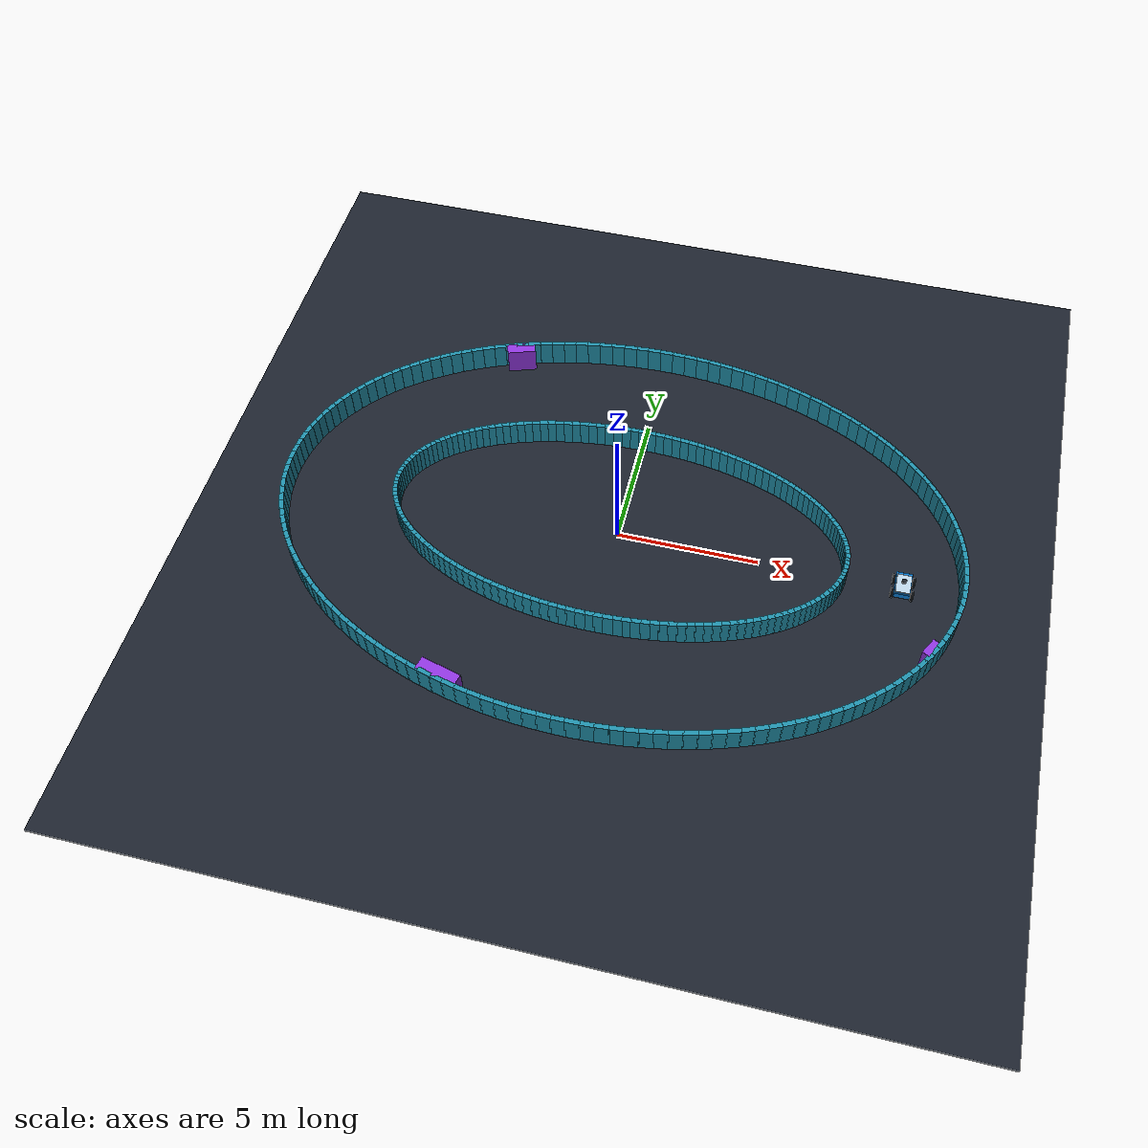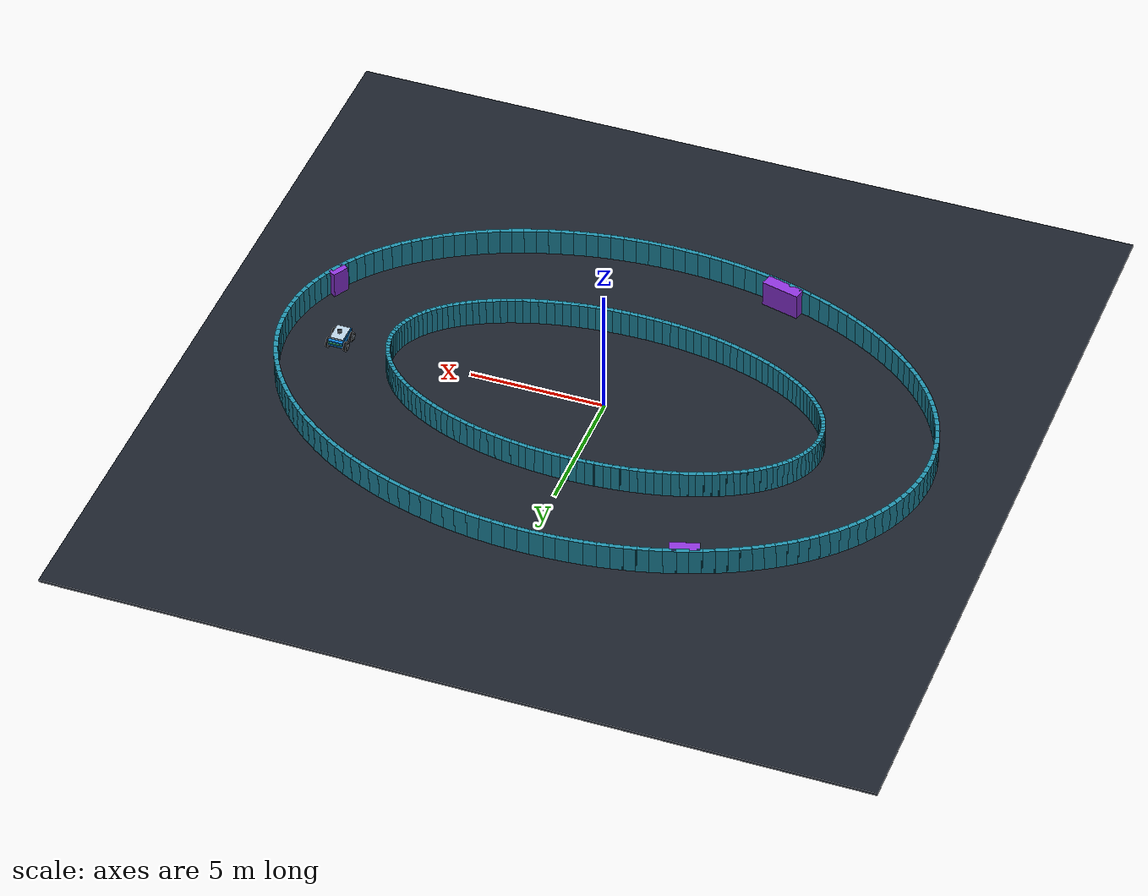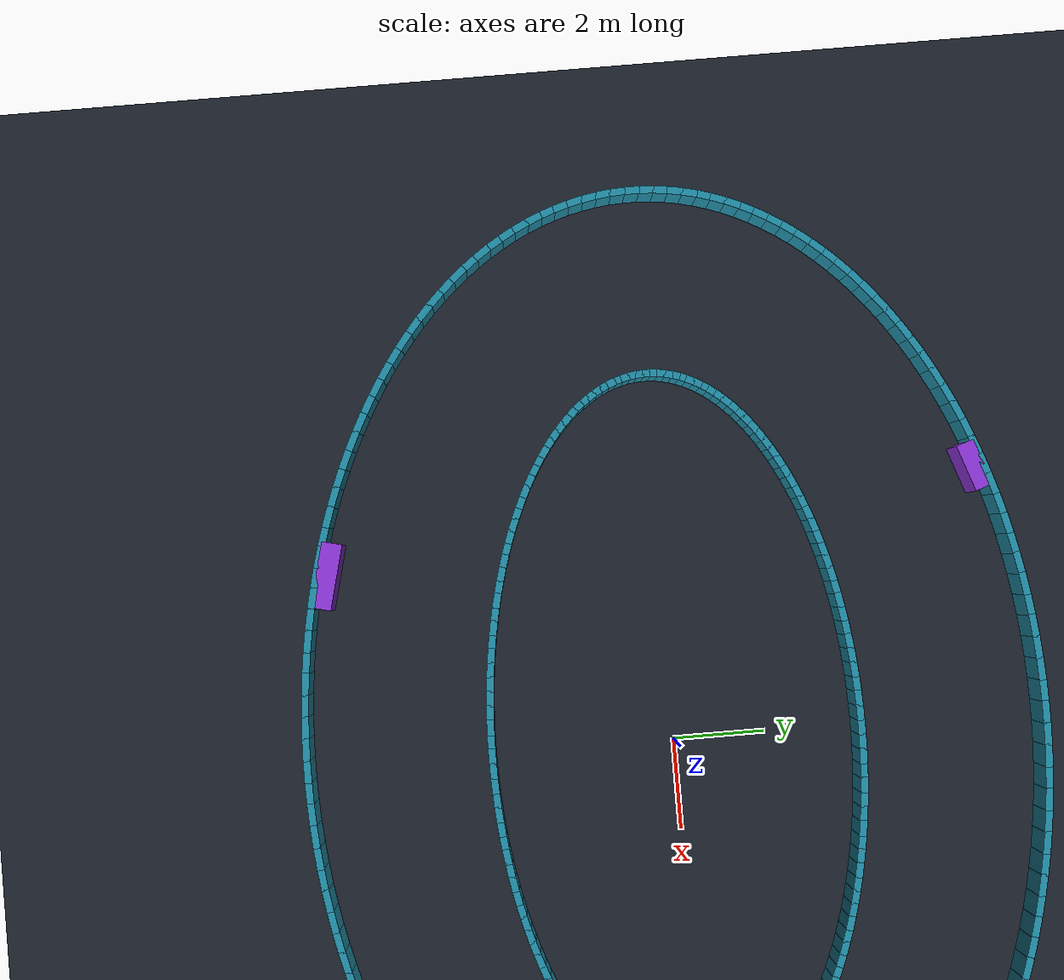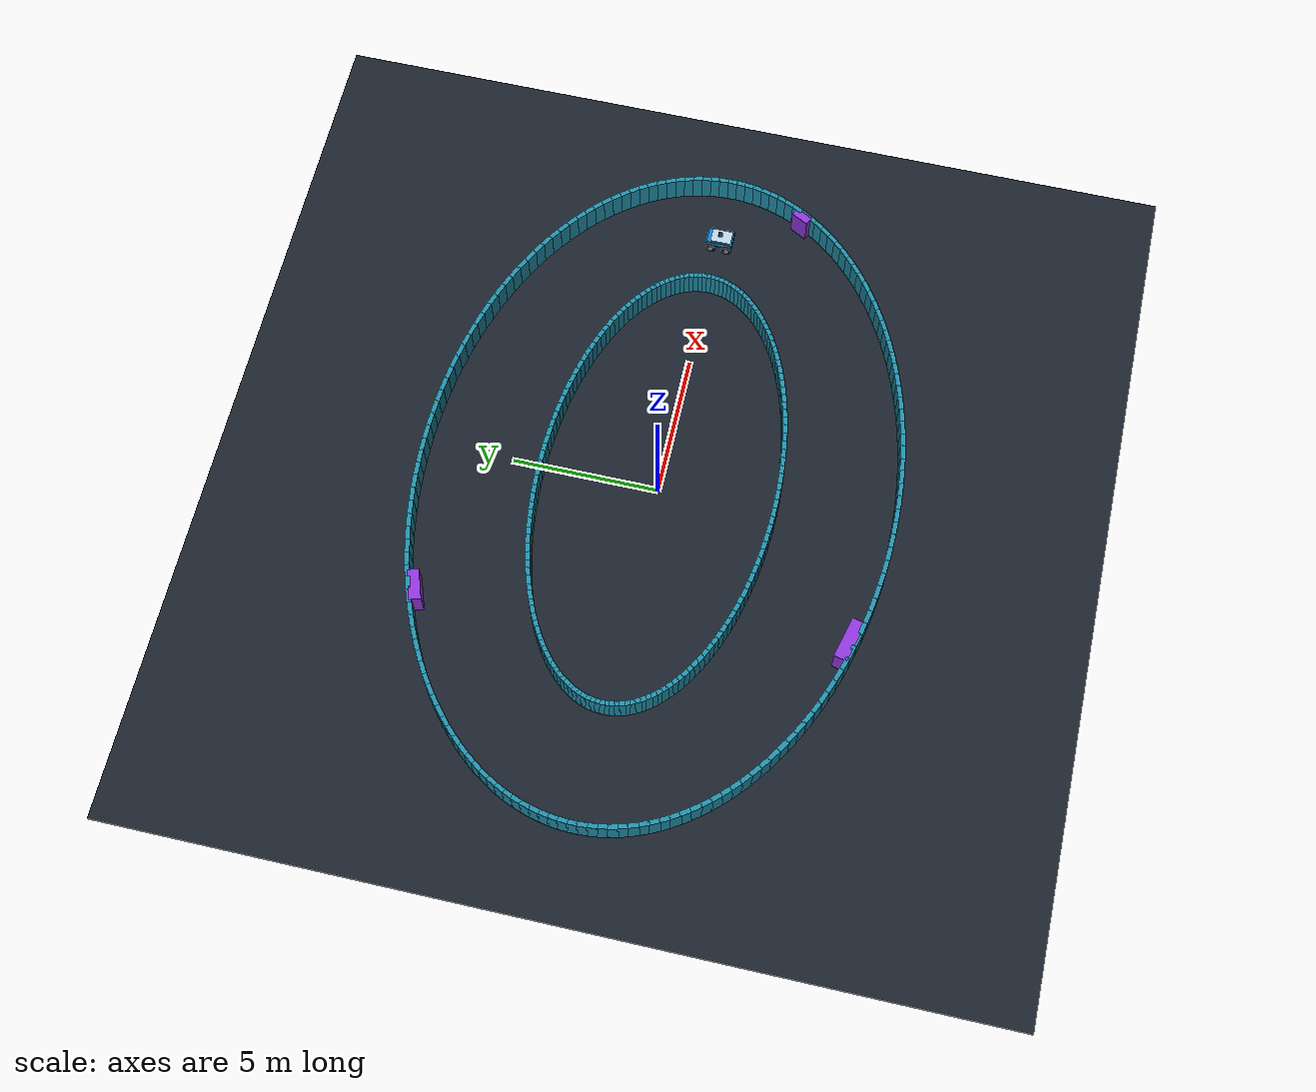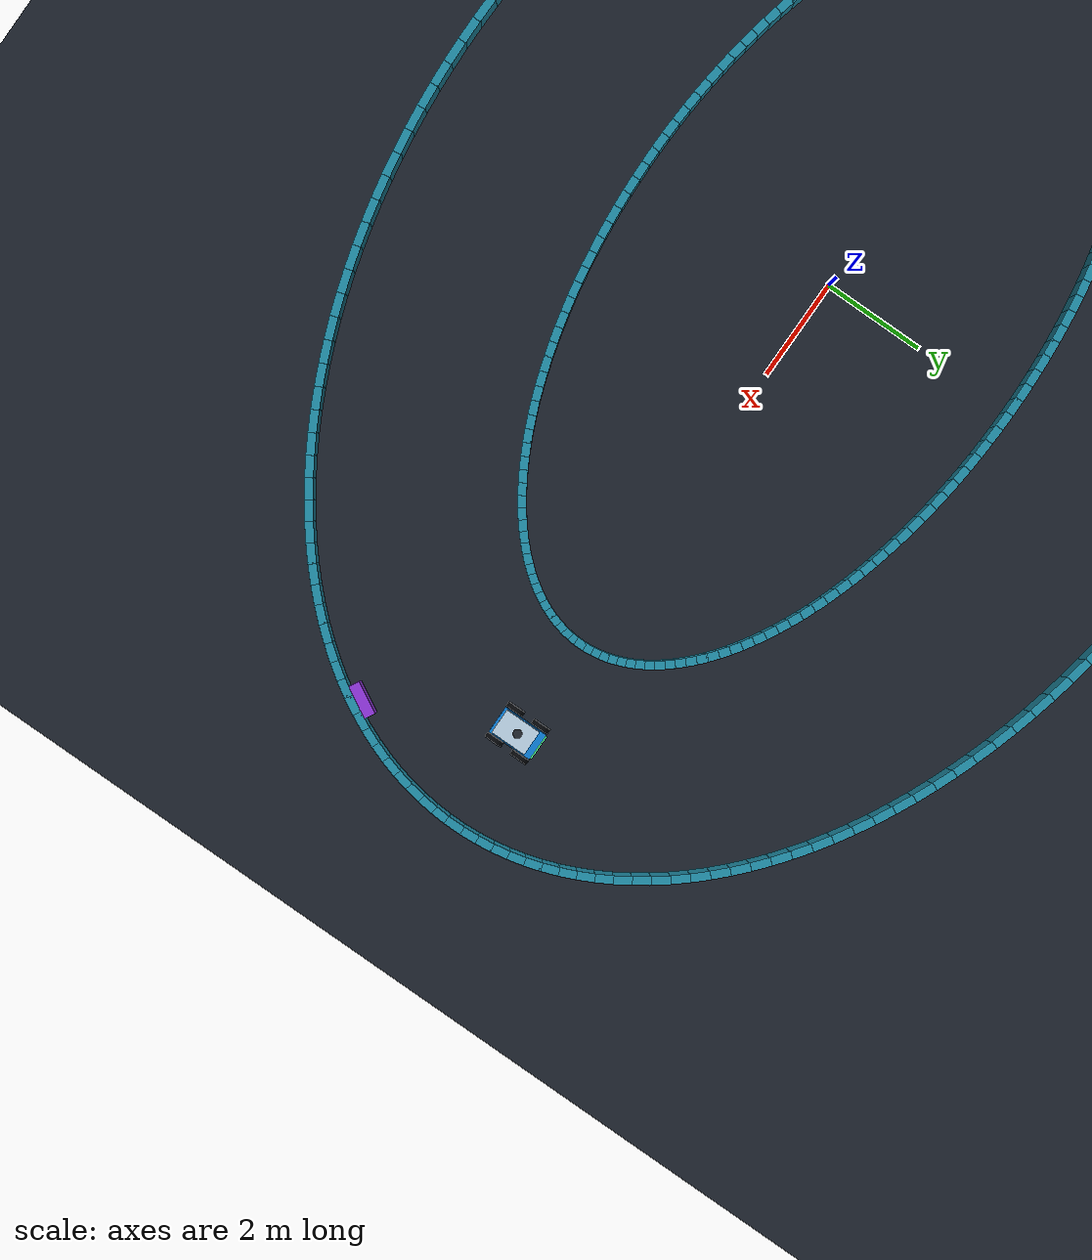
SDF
<?xml version='1.0' encoding='utf-8'?>
<sdf version="1.9">
  <world name="loop_course">
    <physics name="physics" type="ignored">
      <max_step_size>0.002</max_step_size>
      <real_time_factor>1.0</real_time_factor>
    </physics>
    <plugin filename="gz-sim-physics-system" name="gz::sim::systems::Physics" />
    <plugin filename="gz-sim-user-commands-system" name="gz::sim::systems::UserCommands" />
    <plugin filename="gz-sim-scene-broadcaster-system" name="gz::sim::systems::SceneBroadcaster" />
    <plugin filename="gz-sim-contact-system" name="gz::sim::systems::Contact" />
    <plugin filename="gz-sim-imu-system" name="gz::sim::systems::Imu" />
    <plugin filename="gz-sim-sensors-system" name="gz::sim::systems::Sensors">
      <render_engine>ogre2</render_engine>
    </plugin>
    <scene>
      <ambient>0.65 0.65 0.65 1</ambient>
      <background>0.12 0.16 0.22 1</background>
      <shadows>true</shadows>
    </scene>
    <light name="sun" type="directional">
      <pose>0 0 12 0 0 0</pose>
      <diffuse>0.9 0.9 0.85 1</diffuse>
      <specular>0.2 0.2 0.2 1</specular>
      <direction>-0.4 0.2 -0.9</direction>
      <cast_shadows>true</cast_shadows>
    </light>
    <gui fullscreen="false">
      <plugin filename="MinimalScene" name="3D View">
        <engine>ogre2</engine>
        <scene>scene</scene>
        <camera_pose>21 -28 32 0 0.74 2.21</camera_pose>
        <gz-gui>
          <property type="string" key="state">docked</property>
        </gz-gui>
      </plugin>
      <plugin filename="GzSceneManager" name="GzSceneManager" />
      <plugin filename="InteractiveViewControl" name="InteractiveViewControl" />
      <plugin filename="CameraTracking" name="CameraTracking" />
      <plugin filename="EntityContextMenuPlugin" name="EntityContextMenuPlugin" />
      <plugin filename="WorldControl" name="WorldControl">
        <play_pause>true</play_pause>
        <start_paused>false</start_paused>
      </plugin>
      <plugin filename="WorldStats" name="WorldStats">
        <sim_time>true</sim_time>
        <real_time>true</real_time>
        <real_time_factor>true</real_time_factor>
      </plugin>
    </gui>
    <model name="ground">
      <static>true</static>
      <link name="ground">
        <collision name="ground_collision">
          <pose>0 0 -0.05 0 0 0</pose>
          <geometry>
            <box>
              <size>30 30 0.1</size>
            </box>
          </geometry>
        </collision>
        <visual name="ground_visual">
          <pose>0 0 -0.05 0 0 0</pose>
          <geometry>
            <box>
              <size>30 30 0.1</size>
            </box>
          </geometry>
          <material>
            <ambient>0.105 0.13 0.17 1</ambient>
            <diffuse>0.105 0.13 0.17 1</diffuse>
          </material>
        </visual>
      </link>
    </model>
    <model name="loop_cart">
      <pose>10 0 .18 0 0 1.5707963267948966</pose>
      <link name="base_link">
        <inertial>
          <mass>12</mass>
          <inertia>
            <ixx>0.45</ixx>
            <iyy>0.95</iyy>
            <izz>1.2</izz>
            <ixy>0</ixy>
            <ixz>0</ixz>
            <iyz>0</iyz>
          </inertia>
        </inertial>
        <collision name="body_collision">
          <pose>0 0 0.13 0 0 0</pose>
          <geometry>
            <box>
              <size>0.9 0.55 0.22</size>
            </box>
          </geometry>
        </collision>
        <visual name="body_visual">
          <pose>0 0 0.13 0 0 0</pose>
          <geometry>
            <box>
              <size>0.9 0.55 0.22</size>
            </box>
          </geometry>
          <material>
            <ambient>0.04 0.48 0.82 1</ambient>
            <diffuse>0.04 0.48 0.82 1</diffuse>
          </material>
        </visual>
        <visual name="deck">
          <pose>-0.04 0 0.27 0 0 0</pose>
          <geometry>
            <box>
              <size>0.72 0.5 0.07</size>
            </box>
          </geometry>
          <material>
            <ambient>0.72 0.81 0.88 1</ambient>
            <diffuse>0.72 0.81 0.88 1</diffuse>
          </material>
        </visual>
        <visual name="front_stripe">
          <pose>0.46 0 0.15 0 0 0</pose>
          <geometry>
            <box>
              <size>0.04 0.5 0.04</size>
            </box>
          </geometry>
          <material>
            <ambient>0.3 1 0.6 1</ambient>
            <diffuse>0.3 1 0.6 1</diffuse>
          </material>
        </visual>
        <visual name="lidar_visual">
          <pose>0 0 0.39 0 0 0</pose>
          <geometry>
            <cylinder>
              <radius>0.085</radius>
              <length>0.09</length>
            </cylinder>
          </geometry>
          <material>
            <ambient>0.12 0.14 0.17 1</ambient>
            <diffuse>0.12 0.14 0.17 1</diffuse>
          </material>
        </visual>
        <sensor name="body_contact" type="contact">
          <always_on>true</always_on>
          <update_rate>20</update_rate>
          <topic>/loop/contacts/body</topic>
          <contact>
            <collision>body_collision</collision>
          </contact>
        </sensor>
        <sensor name="imu" type="imu">
          <always_on>true</always_on>
          <update_rate>100</update_rate>
          <topic>/loop/imu</topic>
          <gz_frame_id>loop_cart/base_link</gz_frame_id>
          <imu />
        </sensor>
        <sensor name="lidar" type="gpu_lidar">
          <pose>0 0 0.44 0 0 0</pose>
          <topic>/loop/scan</topic>
          <gz_frame_id>loop_cart/lidar</gz_frame_id>
          <update_rate>20</update_rate>
          <always_on>true</always_on>
          <visualize>false</visualize>
          <lidar>
            <scan>
              <horizontal>
                <samples>720</samples>
                <resolution>1</resolution>
                <min_angle>-3.141592653589793</min_angle>
                <max_angle>3.141592653589793</max_angle>
              </horizontal>
            </scan>
            <range>
              <min>0.06</min>
              <max>35</max>
              <resolution>0.005</resolution>
            </range>
          </lidar>
        </sensor>
      </link>
      <link name="front_left">
        <pose>0.28 0.34 0 -1.5707963267948966 0 0</pose>
        <inertial>
          <mass>0.7</mass>
          <inertia>
            <ixx>0.005</ixx>
            <iyy>0.005</iyy>
            <izz>0.009</izz>
            <ixy>0</ixy>
            <ixz>0</ixz>
            <iyz>0</iyz>
          </inertia>
        </inertial>
        <collision name="front_left_collision">
          <pose>0 0 0 0 0 0</pose>
          <geometry>
            <cylinder>
              <radius>0.18</radius>
              <length>0.1</length>
            </cylinder>
          </geometry>
          <surface>
            <friction>
              <ode>
                <mu>1.0</mu>
                <mu2>0.08</mu2>
                <fdir1>1 0 0</fdir1>
              </ode>
            </friction>
          </surface>
        </collision>
        <visual name="front_left_tire">
          <pose>0 0 0 0 0 0</pose>
          <geometry>
            <cylinder>
              <radius>0.18</radius>
              <length>0.1</length>
            </cylinder>
          </geometry>
          <material>
            <ambient>0.025 0.03 0.04 1</ambient>
            <diffuse>0.025 0.03 0.04 1</diffuse>
          </material>
        </visual>
        <visual name="front_left_hub">
          <pose>0 0 0 0 0 0</pose>
          <geometry>
            <cylinder>
              <radius>0.085</radius>
              <length>0.108</length>
            </cylinder>
          </geometry>
          <material>
            <ambient>0.65 0.72 0.8 1</ambient>
            <diffuse>0.65 0.72 0.8 1</diffuse>
          </material>
        </visual>
        <sensor name="front_left_contact" type="contact">
          <always_on>true</always_on>
          <update_rate>20</update_rate>
          <topic>/loop/contacts/front_left</topic>
          <contact>
            <collision>front_left_collision</collision>
          </contact>
        </sensor>
      </link>
      <joint name="front_left_joint" type="revolute">
        <parent>base_link</parent>
        <child>front_left</child>
        <axis>
          <xyz expressed_in="__model__">0 1 0</xyz>
          <limit>
            <lower>-1e+16</lower>
            <upper>1e+16</upper>
            <effort>30</effort>
            <velocity>30</velocity>
          </limit>
        </axis>
      </joint>
      <link name="rear_left">
        <pose>-0.28 0.34 0 -1.5707963267948966 0 0</pose>
        <inertial>
          <mass>0.7</mass>
          <inertia>
            <ixx>0.005</ixx>
            <iyy>0.005</iyy>
            <izz>0.009</izz>
            <ixy>0</ixy>
            <ixz>0</ixz>
            <iyz>0</iyz>
          </inertia>
        </inertial>
        <collision name="rear_left_collision">
          <pose>0 0 0 0 0 0</pose>
          <geometry>
            <cylinder>
              <radius>0.18</radius>
              <length>0.1</length>
            </cylinder>
          </geometry>
          <surface>
            <friction>
              <ode>
                <mu>1.0</mu>
                <mu2>0.08</mu2>
                <fdir1>1 0 0</fdir1>
              </ode>
            </friction>
          </surface>
        </collision>
        <visual name="rear_left_tire">
          <pose>0 0 0 0 0 0</pose>
          <geometry>
            <cylinder>
              <radius>0.18</radius>
              <length>0.1</length>
            </cylinder>
          </geometry>
          <material>
            <ambient>0.025 0.03 0.04 1</ambient>
            <diffuse>0.025 0.03 0.04 1</diffuse>
          </material>
        </visual>
        <visual name="rear_left_hub">
          <pose>0 0 0 0 0 0</pose>
          <geometry>
            <cylinder>
              <radius>0.085</radius>
              <length>0.108</length>
            </cylinder>
          </geometry>
          <material>
            <ambient>0.65 0.72 0.8 1</ambient>
            <diffuse>0.65 0.72 0.8 1</diffuse>
          </material>
        </visual>
        <sensor name="rear_left_contact" type="contact">
          <always_on>true</always_on>
          <update_rate>20</update_rate>
          <topic>/loop/contacts/rear_left</topic>
          <contact>
            <collision>rear_left_collision</collision>
          </contact>
        </sensor>
      </link>
      <joint name="rear_left_joint" type="revolute">
        <parent>base_link</parent>
        <child>rear_left</child>
        <axis>
          <xyz expressed_in="__model__">0 1 0</xyz>
          <limit>
            <lower>-1e+16</lower>
            <upper>1e+16</upper>
            <effort>30</effort>
            <velocity>30</velocity>
          </limit>
        </axis>
      </joint>
      <link name="front_right">
        <pose>0.28 -0.34 0 -1.5707963267948966 0 0</pose>
        <inertial>
          <mass>0.7</mass>
          <inertia>
            <ixx>0.005</ixx>
            <iyy>0.005</iyy>
            <izz>0.009</izz>
            <ixy>0</ixy>
            <ixz>0</ixz>
            <iyz>0</iyz>
          </inertia>
        </inertial>
        <collision name="front_right_collision">
          <pose>0 0 0 0 0 0</pose>
          <geometry>
            <cylinder>
              <radius>0.18</radius>
              <length>0.1</length>
            </cylinder>
          </geometry>
          <surface>
            <friction>
              <ode>
                <mu>1.0</mu>
                <mu2>0.08</mu2>
                <fdir1>1 0 0</fdir1>
              </ode>
            </friction>
          </surface>
        </collision>
        <visual name="front_right_tire">
          <pose>0 0 0 0 0 0</pose>
          <geometry>
            <cylinder>
              <radius>0.18</radius>
              <length>0.1</length>
            </cylinder>
          </geometry>
          <material>
            <ambient>0.025 0.03 0.04 1</ambient>
            <diffuse>0.025 0.03 0.04 1</diffuse>
          </material>
        </visual>
        <visual name="front_right_hub">
          <pose>0 0 0 0 0 0</pose>
          <geometry>
            <cylinder>
              <radius>0.085</radius>
              <length>0.108</length>
            </cylinder>
          </geometry>
          <material>
            <ambient>0.65 0.72 0.8 1</ambient>
            <diffuse>0.65 0.72 0.8 1</diffuse>
          </material>
        </visual>
        <sensor name="front_right_contact" type="contact">
          <always_on>true</always_on>
          <update_rate>20</update_rate>
          <topic>/loop/contacts/front_right</topic>
          <contact>
            <collision>front_right_collision</collision>
          </contact>
        </sensor>
      </link>
      <joint name="front_right_joint" type="revolute">
        <parent>base_link</parent>
        <child>front_right</child>
        <axis>
          <xyz expressed_in="__model__">0 1 0</xyz>
          <limit>
            <lower>-1e+16</lower>
            <upper>1e+16</upper>
            <effort>30</effort>
            <velocity>30</velocity>
          </limit>
        </axis>
      </joint>
      <link name="rear_right">
        <pose>-0.28 -0.34 0 -1.5707963267948966 0 0</pose>
        <inertial>
          <mass>0.7</mass>
          <inertia>
            <ixx>0.005</ixx>
            <iyy>0.005</iyy>
            <izz>0.009</izz>
            <ixy>0</ixy>
            <ixz>0</ixz>
            <iyz>0</iyz>
          </inertia>
        </inertial>
        <collision name="rear_right_collision">
          <pose>0 0 0 0 0 0</pose>
          <geometry>
            <cylinder>
              <radius>0.18</radius>
              <length>0.1</length>
            </cylinder>
          </geometry>
          <surface>
            <friction>
              <ode>
                <mu>1.0</mu>
                <mu2>0.08</mu2>
                <fdir1>1 0 0</fdir1>
              </ode>
            </friction>
          </surface>
        </collision>
        <visual name="rear_right_tire">
          <pose>0 0 0 0 0 0</pose>
          <geometry>
            <cylinder>
              <radius>0.18</radius>
              <length>0.1</length>
            </cylinder>
          </geometry>
          <material>
            <ambient>0.025 0.03 0.04 1</ambient>
            <diffuse>0.025 0.03 0.04 1</diffuse>
          </material>
        </visual>
        <visual name="rear_right_hub">
          <pose>0 0 0 0 0 0</pose>
          <geometry>
            <cylinder>
              <radius>0.085</radius>
              <length>0.108</length>
            </cylinder>
          </geometry>
          <material>
            <ambient>0.65 0.72 0.8 1</ambient>
            <diffuse>0.65 0.72 0.8 1</diffuse>
          </material>
        </visual>
        <sensor name="rear_right_contact" type="contact">
          <always_on>true</always_on>
          <update_rate>20</update_rate>
          <topic>/loop/contacts/rear_right</topic>
          <contact>
            <collision>rear_right_collision</collision>
          </contact>
        </sensor>
      </link>
      <joint name="rear_right_joint" type="revolute">
        <parent>base_link</parent>
        <child>rear_right</child>
        <axis>
          <xyz expressed_in="__model__">0 1 0</xyz>
          <limit>
            <lower>-1e+16</lower>
            <upper>1e+16</upper>
            <effort>30</effort>
            <velocity>30</velocity>
          </limit>
        </axis>
      </joint>
      <plugin filename="gz-sim-diff-drive-system" name="gz::sim::systems::DiffDrive">
        <left_joint>front_left_joint</left_joint>
        <left_joint>rear_left_joint</left_joint>
        <right_joint>front_right_joint</right_joint>
        <right_joint>rear_right_joint</right_joint>
        <wheel_separation>0.68</wheel_separation>
        <wheel_radius>0.18</wheel_radius>
        <topic>/loop/cmd_vel</topic>
        <odom_topic>/loop/wheel_odom</odom_topic>
        <tf_topic>/loop/wheel_tf</tf_topic>
        <frame_id>wheel_odom</frame_id>
        <child_frame_id>loop_cart/base_link</child_frame_id>
        <max_linear_velocity>1.5</max_linear_velocity>
        <min_linear_velocity>-0.8</min_linear_velocity>
        <max_angular_velocity>1.5</max_angular_velocity>
        <min_angular_velocity>-1.5</min_angular_velocity>
        <max_linear_acceleration>1.2</max_linear_acceleration>
        <min_linear_acceleration>-2.5</min_linear_acceleration>
        <max_angular_acceleration>2.5</max_angular_acceleration>
        <min_angular_acceleration>-2.5</min_angular_acceleration>
      </plugin>
      <plugin filename="gz-sim-odometry-publisher-system" name="gz::sim::systems::OdometryPublisher">
        <odom_topic>/loop/ground_truth</odom_topic>
        <tf_topic>/loop/tf</tf_topic>
        <odom_frame>world</odom_frame>
        <robot_base_frame>loop_cart/base_link</robot_base_frame>
        <dimensions>3</dimensions>
        <odom_publish_frequency>30</odom_publish_frequency>
      </plugin>
    </model>
    <model name="overview_camera">
      <static>true</static>
      <link name="camera_link">
        <pose>21 -28 36 0 0.80 2.21</pose>
        <sensor name="overview" type="camera">
          <topic>/loop/overview</topic>
          <update_rate>1</update_rate>
          <always_on>true</always_on>
          <camera>
            <horizontal_fov>1.05</horizontal_fov>
            <image>
              <width>1280</width>
              <height>900</height>
              <format>R8G8B8</format>
            </image>
            <clip>
              <near>0.1</near>
              <far>60</far>
            </clip>
          </camera>
        </sensor>
      </link>
    </model>
    <model name="inner_wall">
      <static>true</static>
      <link name="wall">
        <collision name="wall_0">
          <pose>8.0 0.0 .5 0 0 1.5707963267948966</pose>
          <geometry>
            <box>
              <size>0.19207963267948966 .16 1</size>
            </box>
          </geometry>
        </collision>
        <visual name="wall_0_visual">
          <pose>8.0 0.0 .5 0 0 1.5707963267948966</pose>
          <geometry>
            <box>
              <size>0.19207963267948966 .16 1</size>
            </box>
          </geometry>
          <material>
            <ambient>.12 .55 .65 1</ambient>
            <diffuse>.12 .55 .65 1</diffuse>
          </material>
        </visual>
        <collision name="wall_1">
          <pose>7.993832289925783 0.15703926303627444 .5 0 0 1.6492153970675636</pose>
          <geometry>
            <box>
              <size>0.1924423818887506 .16 1</size>
            </box>
          </geometry>
        </collision>
        <visual name="wall_1_visual">
          <pose>7.993832289925783 0.15703926303627444 .5 0 0 1.6492153970675636</pose>
          <geometry>
            <box>
              <size>0.1924423818887506 .16 1</size>
            </box>
          </geometry>
          <material>
            <ambient>.12 .55 .65 1</ambient>
            <diffuse>.12 .55 .65 1</diffuse>
          </material>
        </visual>
        <collision name="wall_2">
          <pose>7.975338669865024 0.3138363829113798 .5 0 0 1.726918795438885</pose>
          <geometry>
            <box>
              <size>0.1935234305462427 .16 1</size>
            </box>
          </geometry>
        </collision>
        <visual name="wall_2_visual">
          <pose>7.975338669865024 0.3138363829113798 .5 0 0 1.726918795438885</pose>
          <geometry>
            <box>
              <size>0.1935234305462427 .16 1</size>
            </box>
          </geometry>
          <material>
            <ambient>.12 .55 .65 1</ambient>
            <diffuse>.12 .55 .65 1</diffuse>
          </material>
        </visual>
        <collision name="wall_3">
          <pose>7.94454765563941 0.4701495898313506 .5 0 0 1.8032334785543562</pose>
          <geometry>
            <box>
              <size>0.19530167913934707 .16 1</size>
            </box>
          </geometry>
        </collision>
        <visual name="wall_3_visual">
          <pose>7.94454765563941 0.4701495898313506 .5 0 0 1.8032334785543562</pose>
          <geometry>
            <box>
              <size>0.19530167913934707 .16 1</size>
            </box>
          </geometry>
          <material>
            <ambient>.12 .55 .65 1</ambient>
            <diffuse>.12 .55 .65 1</diffuse>
          </material>
        </visual>
        <collision name="wall_4">
          <pose>7.901506724761102 0.6257378601609235 .5 0 0 1.8775655418065365</pose>
          <geometry>
            <box>
              <size>0.1977435377699861 .16 1</size>
            </box>
          </geometry>
        </collision>
        <visual name="wall_4_visual">
          <pose>7.901506724761102 0.6257378601609235 .5 0 0 1.8775655418065365</pose>
          <geometry>
            <box>
              <size>0.1977435377699861 .16 1</size>
            </box>
          </geometry>
          <material>
            <ambient>.12 .55 .65 1</ambient>
            <diffuse>.12 .55 .65 1</diffuse>
          </material>
        </visual>
        <collision name="wall_5">
          <pose>7.8462822432258434 0.780361288064513 .5 0 0 1.949426069805648</pose>
          <geometry>
            <box>
              <size>0.20080502670681258 .16 1</size>
            </box>
          </geometry>
        </collision>
        <visual name="wall_5_visual">
          <pose>7.8462822432258434 0.780361288064513 .5 0 0 1.949426069805648</pose>
          <geometry>
            <box>
              <size>0.20080502670681258 .16 1</size>
            </box>
          </geometry>
          <material>
            <ambient>.12 .55 .65 1</ambient>
            <diffuse>.12 .55 .65 1</diffuse>
          </material>
        </visual>
        <collision name="wall_6">
          <pose>7.7789593631814125 0.9337814554236216 .5 0 0 2.0184443159966</pose>
          <geometry>
            <box>
              <size>0.2044342655274467 .16 1</size>
            </box>
          </geometry>
        </collision>
        <visual name="wall_6_visual">
          <pose>7.7789593631814125 0.9337814554236216 .5 0 0 2.0184443159966</pose>
          <geometry>
            <box>
              <size>0.2044342655274467 .16 1</size>
            </box>
          </geometry>
          <material>
            <ambient>.12 .55 .65 1</ambient>
            <diffuse>.12 .55 .65 1</diffuse>
          </material>
        </visual>
        <collision name="wall_7">
          <pose>7.699641891629178 1.085761799460297 .5 0 0 2.084368779748059</pose>
          <geometry>
            <box>
              <size>0.20857404273638774 .16 1</size>
            </box>
          </geometry>
        </collision>
        <visual name="wall_7_visual">
          <pose>7.699641891629178 1.085761799460297 .5 0 0 2.084368779748059</pose>
          <geometry>
            <box>
              <size>0.20857404273638774 .16 1</size>
            </box>
          </geometry>
          <material>
            <ambient>.12 .55 .65 1</ambient>
            <diffuse>.12 .55 .65 1</diffuse>
          </material>
        </visual>
        <collision name="wall_8">
          <pose>7.608452130361228 1.2360679774997896 .5 0 0 2.14705863397934</pose>
          <geometry>
            <box>
              <size>0.2131642112656523 .16 1</size>
            </box>
          </geometry>
        </collision>
        <visual name="wall_8_visual">
          <pose>7.608452130361228 1.2360679774997896 .5 0 0 2.14705863397934</pose>
          <geometry>
            <box>
              <size>0.2131642112656523 .16 1</size>
            </box>
          </geometry>
          <material>
            <ambient>.12 .55 .65 1</ambient>
            <diffuse>.12 .55 .65 1</diffuse>
          </material>
        </visual>
        <collision name="wall_9">
          <pose>7.505530687379873 1.3844682283099718 .5 0 0 2.2064688273396227</pose>
          <geometry>
            <box>
              <size>0.2181437407179972 .16 1</size>
            </box>
          </geometry>
        </collision>
        <visual name="wall_9_visual">
          <pose>7.505530687379873 1.3844682283099718 .5 0 0 2.2064688273396227</pose>
          <geometry>
            <box>
              <size>0.2181437407179972 .16 1</size>
            </box>
          </geometry>
          <material>
            <ambient>.12 .55 .65 1</ambient>
            <diffuse>.12 .55 .65 1</diffuse>
          </material>
        </visual>
        <collision name="wall_10">
          <pose>7.391036260090294 1.5307337294603591 .5 0 0 2.2626321404381216</pose>
          <geometry>
            <box>
              <size>0.22345234612008066 .16 1</size>
            </box>
          </geometry>
        </collision>
        <visual name="wall_10_visual">
          <pose>7.391036260090294 1.5307337294603591 .5 0 0 2.2626321404381216</pose>
          <geometry>
            <box>
              <size>0.22345234612008066 .16 1</size>
            </box>
          </geometry>
          <material>
            <ambient>.12 .55 .65 1</ambient>
            <diffuse>.12 .55 .65 1</diffuse>
          </material>
        </visual>
        <collision name="wall_11">
          <pose>7.265145390600651 1.674638950149712 .5 0 0 2.3156408472748087</pose>
          <geometry>
            <box>
              <size>0.22903168574105162 .16 1</size>
            </box>
          </geometry>
        </collision>
        <visual name="wall_11_visual">
          <pose>7.265145390600651 1.674638950149712 .5 0 0 2.3156408472748087</pose>
          <geometry>
            <box>
              <size>0.22903168574105162 .16 1</size>
            </box>
          </geometry>
          <material>
            <ambient>.12 .55 .65 1</ambient>
            <diffuse>.12 .55 .65 1</diffuse>
          </material>
        </visual>
        <collision name="wall_12">
          <pose>7.128052193506943 1.815961998958187 .5 0 0 2.3656297816262386</pose>
          <geometry>
            <box>
              <size>0.23482616904037854 .16 1</size>
            </box>
          </geometry>
        </collision>
        <visual name="wall_12_visual">
          <pose>7.128052193506943 1.815961998958187 .5 0 0 2.3656297816262386</pose>
          <geometry>
            <box>
              <size>0.23482616904037854 .16 1</size>
            </box>
          </geometry>
          <material>
            <ambient>.12 .55 .65 1</ambient>
            <diffuse>.12 .55 .65 1</diffuse>
          </material>
        </visual>
        <collision name="wall_13">
          <pose>6.979968056582377 1.9544849659878196 .5 0 0 2.4127617984595986</pose>
          <geometry>
            <box>
              <size>0.24078344079333916 .16 1</size>
            </box>
          </geometry>
        </collision>
        <visual name="wall_13_visual">
          <pose>6.979968056582377 1.9544849659878196 .5 0 0 2.4127617984595986</pose>
          <geometry>
            <box>
              <size>0.24078344079333916 .16 1</size>
            </box>
          </geometry>
          <material>
            <ambient>.12 .55 .65 1</ambient>
            <diffuse>.12 .55 .65 1</diffuse>
          </material>
        </visual>
        <collision name="wall_14">
          <pose>6.821121314832737 2.089994258863795 .5 0 0 2.45721598876684</pose>
          <geometry>
            <box>
              <size>0.24685461436619754 .16 1</size>
            </box>
          </geometry>
        </collision>
        <visual name="wall_14_visual">
          <pose>6.821121314832737 2.089994258863795 .5 0 0 2.45721598876684</pose>
          <geometry>
            <box>
              <size>0.24685461436619754 .16 1</size>
            </box>
          </geometry>
          <material>
            <ambient>.12 .55 .65 1</ambient>
            <diffuse>.12 .55 .65 1</diffuse>
          </material>
        </visual>
        <collision name="wall_15">
          <pose>6.651756898420362 2.2222809320784087 .5 0 0 2.4991785858377993</pose>
          <geometry>
            <box>
              <size>0.2529943225767685 .16 1</size>
            </box>
          </geometry>
        </collision>
        <visual name="wall_15_visual">
          <pose>6.651756898420362 2.2222809320784087 .5 0 0 2.4991785858377993</pose>
          <geometry>
            <box>
              <size>0.2529943225767685 .16 1</size>
            </box>
          </geometry>
          <material>
            <ambient>.12 .55 .65 1</ambient>
            <diffuse>.12 .55 .65 1</diffuse>
          </material>
        </visual>
        <collision name="wall_16">
          <pose>6.47213595499958 2.3511410091698925 .5 0 0 2.538836265630875</pose>
          <geometry>
            <box>
              <size>0.25916064424415486 .16 1</size>
            </box>
          </geometry>
        </collision>
        <visual name="wall_16_visual">
          <pose>6.47213595499958 2.3511410091698925 .5 0 0 2.538836265630875</pose>
          <geometry>
            <box>
              <size>0.25916064424415486 .16 1</size>
            </box>
          </geometry>
          <material>
            <ambient>.12 .55 .65 1</ambient>
            <diffuse>.12 .55 .65 1</diffuse>
          </material>
        </visual>
        <collision name="wall_17">
          <pose>6.28253544704596 2.476375797239336 .5 0 0 2.5763714445618193</pose>
          <geometry>
            <box>
              <size>0.2653149523855006 .16 1</size>
            </box>
          </geometry>
        </collision>
        <visual name="wall_17_visual">
          <pose>6.28253544704596 2.476375797239336 .5 0 0 2.5763714445618193</pose>
          <geometry>
            <box>
              <size>0.2653149523855006 .16 1</size>
            </box>
          </geometry>
          <material>
            <ambient>.12 .55 .65 1</ambient>
            <diffuse>.12 .55 .65 1</diffuse>
          </material>
        </visual>
        <collision name="wall_18">
          <pose>6.0832477248002474 2.5977921933207346 .5 0 0 2.611959165674998</pose>
          <geometry>
            <box>
              <size>0.2714217184173162 .16 1</size>
            </box>
          </geometry>
        </collision>
        <visual name="wall_18_visual">
          <pose>6.0832477248002474 2.5977921933207346 .5 0 0 2.611959165674998</pose>
          <geometry>
            <box>
              <size>0.2714217184173162 .16 1</size>
            </box>
          </geometry>
          <material>
            <ambient>.12 .55 .65 1</ambient>
            <diffuse>.12 .55 .65 1</diffuse>
          </material>
        </visual>
        <collision name="wall_19">
          <pose>5.874580075485484 2.7152029821317667 .5 0 0 2.6457651997563683</pose>
          <geometry>
            <box>
              <size>0.277448296797337 .16 1</size>
            </box>
          </geometry>
        </collision>
        <visual name="wall_19_visual">
          <pose>5.874580075485484 2.7152029821317667 .5 0 0 2.6457651997563683</pose>
          <geometry>
            <box>
              <size>0.277448296797337 .16 1</size>
            </box>
          </geometry>
          <material>
            <ambient>.12 .55 .65 1</ambient>
            <diffuse>.12 .55 .65 1</diffuse>
          </material>
        </visual>
        <collision name="wall_20">
          <pose>5.656854249492381 2.82842712474619 .5 0 0 2.677945044588987</pose>
          <geometry>
            <box>
              <size>0.2833647066449025 .16 1</size>
            </box>
          </geometry>
        </collision>
        <visual name="wall_20_visual">
          <pose>5.656854249492381 2.82842712474619 .5 0 0 2.677945044588987</pose>
          <geometry>
            <box>
              <size>0.2833647066449025 .16 1</size>
            </box>
          </geometry>
          <material>
            <ambient>.12 .55 .65 1</ambient>
            <diffuse>.12 .55 .65 1</diffuse>
          </material>
        </visual>
        <collision name="wall_21">
          <pose>5.430405964263534 2.937290037742742 .5 0 0 2.708643566783405</pose>
          <geometry>
            <box>
              <size>0.28914342091363954 .16 1</size>
            </box>
          </geometry>
        </collision>
        <visual name="wall_21_visual">
          <pose>5.430405964263534 2.937290037742742 .5 0 0 2.708643566783405</pose>
          <geometry>
            <box>
              <size>0.28914342091363954 .16 1</size>
            </box>
          </geometry>
          <material>
            <ambient>.12 .55 .65 1</ambient>
            <diffuse>.12 .55 .65 1</diffuse>
          </material>
        </visual>
        <collision name="wall_22">
          <pose>5.19558438664147 3.0416238624001233 .5 0 0 2.737995087598962</pose>
          <geometry>
            <box>
              <size>0.29475916937467317 .16 1</size>
            </box>
          </geometry>
        </collision>
        <visual name="wall_22_visual">
          <pose>5.19558438664147 3.0416238624001233 .5 0 0 2.737995087598962</pose>
          <geometry>
            <box>
              <size>0.29475916937467317 .16 1</size>
            </box>
          </geometry>
          <material>
            <ambient>.12 .55 .65 1</ambient>
            <diffuse>.12 .55 .65 1</diffuse>
          </material>
        </visual>
        <collision name="wall_23">
          <pose>4.952751594478672 3.14126772352298 .5 0 0 2.7661237630192383</pose>
          <geometry>
            <box>
              <size>0.3001887586631107 .16 1</size>
            </box>
          </geometry>
        </collision>
        <visual name="wall_23_visual">
          <pose>4.952751594478672 3.14126772352298 .5 0 0 2.7661237630192383</pose>
          <geometry>
            <box>
              <size>0.3001887586631107 .16 1</size>
            </box>
          </geometry>
          <material>
            <ambient>.12 .55 .65 1</ambient>
            <diffuse>.12 .55 .65 1</diffuse>
          </material>
        </visual>
        <collision name="wall_24">
          <pose>4.702282018339785 3.23606797749979 .5 0 0 2.793144148070681</pose>
          <geometry>
            <box>
              <size>0.30541091062614767 .16 1</size>
            </box>
          </geometry>
        </collision>
        <visual name="wall_24_visual">
          <pose>4.702282018339785 3.23606797749979 .5 0 0 2.793144148070681</pose>
          <geometry>
            <box>
              <size>0.30541091062614767 .16 1</size>
            </box>
          </geometry>
          <material>
            <ambient>.12 .55 .65 1</ambient>
            <diffuse>.12 .55 .65 1</diffuse>
          </material>
        </visual>
        <collision name="wall_25">
          <pose>4.444561864156818 3.325878449210181 .5 0 0 2.8191618665082485</pose>
          <geometry>
            <box>
              <size>0.31040611891879377 .16 1</size>
            </box>
          </geometry>
        </collision>
        <visual name="wall_25_visual">
          <pose>4.444561864156818 3.325878449210181 .5 0 0 2.8191618665082485</pose>
          <geometry>
            <box>
              <size>0.31040611891879377 .16 1</size>
            </box>
          </geometry>
          <material>
            <ambient>.12 .55 .65 1</ambient>
            <diffuse>.12 .55 .65 1</diffuse>
          </material>
        </visual>
        <collision name="wall_26">
          <pose>4.179988517727591 3.4105606574163687 .5 0 0 2.844274330724959</pose>
          <geometry>
            <box>
              <size>0.3151565230105604 .16 1</size>
            </box>
          </geometry>
        </collision>
        <visual name="wall_26_visual">
          <pose>4.179988517727591 3.4105606574163687 .5 0 0 2.844274330724959</pose>
          <geometry>
            <box>
              <size>0.3151565230105604 .16 1</size>
            </box>
          </geometry>
          <material>
            <ambient>.12 .55 .65 1</ambient>
            <diffuse>.12 .55 .65 1</diffuse>
          </material>
        </visual>
        <collision name="wall_27">
          <pose>3.9089699319756397 3.4899840282911883 .5 0 0 2.868571474436653</pose>
          <geometry>
            <box>
              <size>0.3196457983334222 .16 1</size>
            </box>
          </geometry>
        </collision>
        <visual name="wall_27_visual">
          <pose>3.9089699319756397 3.4899840282911883 .5 0 0 2.868571474436653</pose>
          <geometry>
            <box>
              <size>0.3196457983334222 .16 1</size>
            </box>
          </geometry>
          <material>
            <ambient>.12 .55 .65 1</ambient>
            <diffuse>.12 .55 .65 1</diffuse>
          </material>
        </visual>
        <collision name="wall_28">
          <pose>3.6319239979163744 3.564026096753471 .5 0 0 2.892136473640175</pose>
          <geometry>
            <box>
              <size>0.32385906110119345 .16 1</size>
            </box>
          </geometry>
        </collision>
        <visual name="wall_28_visual">
          <pose>3.6319239979163744 3.564026096753471 .5 0 0 2.892136473640175</pose>
          <geometry>
            <box>
              <size>0.32385906110119345 .16 1</size>
            </box>
          </geometry>
          <material>
            <ambient>.12 .55 .65 1</ambient>
            <diffuse>.12 .55 .65 1</diffuse>
          </material>
        </visual>
        <collision name="wall_29">
          <pose>3.349277900299425 3.632572695300325 .5 0 0 2.9150464406566736</pose>
          <geometry>
            <box>
              <size>0.32778278628038016 .16 1</size>
            </box>
          </geometry>
        </collision>
        <visual name="wall_29_visual">
          <pose>3.349277900299425 3.632572695300325 .5 0 0 2.9150464406566736</pose>
          <geometry>
            <box>
              <size>0.32778278628038016 .16 1</size>
            </box>
          </geometry>
          <material>
            <ambient>.12 .55 .65 1</ambient>
            <diffuse>.12 .55 .65 1</diffuse>
          </material>
        </visual>
        <collision name="wall_30">
          <pose>3.0614674589207187 3.695518130045147 .5 0 0 2.9373730826616744</pose>
          <geometry>
            <box>
              <size>0.33140473723517694 .16 1</size>
            </box>
          </geometry>
        </collision>
        <visual name="wall_30_visual">
          <pose>3.0614674589207187 3.695518130045147 .5 0 0 2.9373730826616744</pose>
          <geometry>
            <box>
              <size>0.33140473723517694 .16 1</size>
            </box>
          </geometry>
          <material>
            <ambient>.12 .55 .65 1</ambient>
            <diffuse>.12 .55 .65 1</diffuse>
          </material>
        </visual>
        <collision name="wall_31">
          <pose>2.768936456619944 3.7527653436899366 .5 0 0 2.9591833206864604</pose>
          <geometry>
            <box>
              <size>0.33471390566577985 .16 1</size>
            </box>
          </geometry>
        </collision>
        <visual name="wall_31_visual">
          <pose>2.768936456619944 3.7527653436899366 .5 0 0 2.9591833206864604</pose>
          <geometry>
            <box>
              <size>0.33471390566577985 .16 1</size>
            </box>
          </geometry>
          <material>
            <ambient>.12 .55 .65 1</ambient>
            <diffuse>.12 .55 .65 1</diffuse>
          </material>
        </visual>
        <collision name="wall_32">
          <pose>2.4721359549995796 3.804226065180614 .5 0 0 2.9805398682009576</pose>
          <geometry>
            <box>
              <size>0.3377004605838996 .16 1</size>
            </box>
          </geometry>
        </collision>
        <visual name="wall_32_visual">
          <pose>2.4721359549995796 3.804226065180614 .5 0 0 2.9805398682009576</pose>
          <geometry>
            <box>
              <size>0.3377004605838996 .16 1</size>
            </box>
          </geometry>
          <material>
            <ambient>.12 .55 .65 1</ambient>
            <diffuse>.12 .55 .65 1</diffuse>
          </material>
        </visual>
        <collision name="wall_33">
          <pose>2.1715235989205945 3.849820945814589 .5 0 0 3.001501770470793</pose>
          <geometry>
            <box>
              <size>0.3403557052058528 .16 1</size>
            </box>
          </geometry>
        </collision>
        <visual name="wall_33_visual">
          <pose>2.1715235989205945 3.849820945814589 .5 0 0 3.001501770470793</pose>
          <geometry>
            <box>
              <size>0.3403557052058528 .16 1</size>
            </box>
          </geometry>
          <material>
            <ambient>.12 .55 .65 1</ambient>
            <diffuse>.12 .55 .65 1</diffuse>
          </material>
        </visual>
        <collision name="wall_34">
          <pose>1.8675629108472438 3.8894796815907062 .5 0 0 3.0221249072278122</pose>
          <geometry>
            <box>
              <size>0.3426720407817253 .16 1</size>
            </box>
          </geometry>
        </collision>
        <visual name="wall_34_visual">
          <pose>1.8675629108472438 3.8894796815907062 .5 0 0 3.0221249072278122</pose>
          <geometry>
            <box>
              <size>0.3426720407817253 .16 1</size>
            </box>
          </geometry>
          <material>
            <ambient>.12 .55 .65 1</ambient>
            <diffuse>.12 .55 .65 1</diffuse>
          </material>
        </visual>
        <collision name="wall_35">
          <pose>1.5607225761290267 3.9231411216129217 .5 0 0 3.042462462029321</pose>
          <geometry>
            <box>
              <size>0.34464293651296185 .16 1</size>
            </box>
          </geometry>
        </collision>
        <visual name="wall_35_visual">
          <pose>1.5607225761290267 3.9231411216129217 .5 0 0 3.042462462029321</pose>
          <geometry>
            <box>
              <size>0.34464293651296185 .16 1</size>
            </box>
          </geometry>
          <material>
            <ambient>.12 .55 .65 1</ambient>
            <diffuse>.12 .55 .65 1</diffuse>
          </material>
        </visual>
        <collision name="wall_36">
          <pose>1.2514757203218474 3.950753362380551 .5 0 0 3.062565362170346</pose>
          <geometry>
            <box>
              <size>0.3462629048372551 .16 1</size>
            </box>
          </geometry>
        </collision>
        <visual name="wall_36_visual">
          <pose>1.2514757203218474 3.950753362380551 .5 0 0 3.062565362170346</pose>
          <geometry>
            <box>
              <size>0.3462629048372551 .16 1</size>
            </box>
          </geometry>
          <material>
            <ambient>.12 .55 .65 1</ambient>
            <diffuse>.12 .55 .65 1</diffuse>
          </material>
        </visual>
        <collision name="wall_37">
          <pose>0.9402991796627016 3.972273827819705 .5 0 0 3.0824826932728735</pose>
          <geometry>
            <box>
              <size>0.34752748147758594 .16 1</size>
            </box>
          </geometry>
        </collision>
        <visual name="wall_37_visual">
          <pose>0.9402991796627016 3.972273827819705 .5 0 0 3.0824826932728735</pose>
          <geometry>
            <box>
              <size>0.34752748147758594 .16 1</size>
            </box>
          </geometry>
          <material>
            <ambient>.12 .55 .65 1</ambient>
            <diffuse>.12 .55 .65 1</diffuse>
          </material>
        </visual>
        <collision name="wall_38">
          <pose>0.62767276582276 3.987669334932512 .5 0 0 3.1022620927903404</pose>
          <geometry>
            <box>
              <size>0.3484332097616134 .16 1</size>
            </box>
          </geometry>
        </collision>
        <visual name="wall_38_visual">
          <pose>0.62767276582276 3.987669334932512 .5 0 0 3.1022620927903404</pose>
          <geometry>
            <box>
              <size>0.3484332097616134 .16 1</size>
            </box>
          </geometry>
          <material>
            <ambient>.12 .55 .65 1</ambient>
            <diffuse>.12 .55 .65 1</diffuse>
          </material>
        </visual>
        <collision name="wall_39">
          <pose>0.3140785260725493 3.9969161449628916 .5 0 0 3.121950126693833</pose>
          <geometry>
            <box>
              <size>0.34897762881901917 .16 1</size>
            </box>
          </geometry>
        </collision>
        <visual name="wall_39_visual">
          <pose>0.3140785260725493 3.9969161449628916 .5 0 0 3.121950126693833</pose>
          <geometry>
            <box>
              <size>0.34897762881901917 .16 1</size>
            </box>
          </geometry>
          <material>
            <ambient>.12 .55 .65 1</ambient>
            <diffuse>.12 .55 .65 1</diffuse>
          </material>
        </visual>
        <collision name="wall_40">
          <pose>4.898587196589413e-16 4.0 .5 0 0 3.141592653589793</pose>
          <geometry>
            <box>
              <size>0.34915926535897934 .16 1</size>
            </box>
          </geometry>
        </collision>
        <visual name="wall_40_visual">
          <pose>4.898587196589413e-16 4.0 .5 0 0 3.141592653589793</pose>
          <geometry>
            <box>
              <size>0.34915926535897934 .16 1</size>
            </box>
          </geometry>
          <material>
            <ambient>.12 .55 .65 1</ambient>
            <diffuse>.12 .55 .65 1</diffuse>
          </material>
        </visual>
        <collision name="wall_41">
          <pose>-0.3140785260725466 3.9969161449628916 .5 0 0 -3.121950126693833</pose>
          <geometry>
            <box>
              <size>0.34897762881901917 .16 1</size>
            </box>
          </geometry>
        </collision>
        <visual name="wall_41_visual">
          <pose>-0.3140785260725466 3.9969161449628916 .5 0 0 -3.121950126693833</pose>
          <geometry>
            <box>
              <size>0.34897762881901917 .16 1</size>
            </box>
          </geometry>
          <material>
            <ambient>.12 .55 .65 1</ambient>
            <diffuse>.12 .55 .65 1</diffuse>
          </material>
        </visual>
        <collision name="wall_42">
          <pose>-0.627672765822759 3.987669334932512 .5 0 0 -3.1022620927903404</pose>
          <geometry>
            <box>
              <size>0.3484332097616134 .16 1</size>
            </box>
          </geometry>
        </collision>
        <visual name="wall_42_visual">
          <pose>-0.627672765822759 3.987669334932512 .5 0 0 -3.1022620927903404</pose>
          <geometry>
            <box>
              <size>0.3484332097616134 .16 1</size>
            </box>
          </geometry>
          <material>
            <ambient>.12 .55 .65 1</ambient>
            <diffuse>.12 .55 .65 1</diffuse>
          </material>
        </visual>
        <collision name="wall_43">
          <pose>-0.9402991796627006 3.972273827819705 .5 0 0 -3.0824826932728735</pose>
          <geometry>
            <box>
              <size>0.34752748147758594 .16 1</size>
            </box>
          </geometry>
        </collision>
        <visual name="wall_43_visual">
          <pose>-0.9402991796627006 3.972273827819705 .5 0 0 -3.0824826932728735</pose>
          <geometry>
            <box>
              <size>0.34752748147758594 .16 1</size>
            </box>
          </geometry>
          <material>
            <ambient>.12 .55 .65 1</ambient>
            <diffuse>.12 .55 .65 1</diffuse>
          </material>
        </visual>
        <collision name="wall_44">
          <pose>-1.2514757203218447 3.950753362380551 .5 0 0 -3.0625653621703464</pose>
          <geometry>
            <box>
              <size>0.3462629048372551 .16 1</size>
            </box>
          </geometry>
        </collision>
        <visual name="wall_44_visual">
          <pose>-1.2514757203218447 3.950753362380551 .5 0 0 -3.0625653621703464</pose>
          <geometry>
            <box>
              <size>0.3462629048372551 .16 1</size>
            </box>
          </geometry>
          <material>
            <ambient>.12 .55 .65 1</ambient>
            <diffuse>.12 .55 .65 1</diffuse>
          </material>
        </visual>
        <collision name="wall_45">
          <pose>-1.5607225761290255 3.9231411216129217 .5 0 0 -3.042462462029321</pose>
          <geometry>
            <box>
              <size>0.34464293651296185 .16 1</size>
            </box>
          </geometry>
        </collision>
        <visual name="wall_45_visual">
          <pose>-1.5607225761290255 3.9231411216129217 .5 0 0 -3.042462462029321</pose>
          <geometry>
            <box>
              <size>0.34464293651296185 .16 1</size>
            </box>
          </geometry>
          <material>
            <ambient>.12 .55 .65 1</ambient>
            <diffuse>.12 .55 .65 1</diffuse>
          </material>
        </visual>
        <collision name="wall_46">
          <pose>-1.8675629108472427 3.8894796815907067 .5 0 0 -3.0221249072278122</pose>
          <geometry>
            <box>
              <size>0.3426720407817254 .16 1</size>
            </box>
          </geometry>
        </collision>
        <visual name="wall_46_visual">
          <pose>-1.8675629108472427 3.8894796815907067 .5 0 0 -3.0221249072278122</pose>
          <geometry>
            <box>
              <size>0.3426720407817254 .16 1</size>
            </box>
          </geometry>
          <material>
            <ambient>.12 .55 .65 1</ambient>
            <diffuse>.12 .55 .65 1</diffuse>
          </material>
        </visual>
        <collision name="wall_47">
          <pose>-2.171523598920595 3.849820945814589 .5 0 0 -3.001501770470793</pose>
          <geometry>
            <box>
              <size>0.3403557052058528 .16 1</size>
            </box>
          </geometry>
        </collision>
        <visual name="wall_47_visual">
          <pose>-2.171523598920595 3.849820945814589 .5 0 0 -3.001501770470793</pose>
          <geometry>
            <box>
              <size>0.3403557052058528 .16 1</size>
            </box>
          </geometry>
          <material>
            <ambient>.12 .55 .65 1</ambient>
            <diffuse>.12 .55 .65 1</diffuse>
          </material>
        </visual>
        <collision name="wall_48">
          <pose>-2.4721359549995787 3.8042260651806146 .5 0 0 -2.9805398682009576</pose>
          <geometry>
            <box>
              <size>0.3377004605838997 .16 1</size>
            </box>
          </geometry>
        </collision>
        <visual name="wall_48_visual">
          <pose>-2.4721359549995787 3.8042260651806146 .5 0 0 -2.9805398682009576</pose>
          <geometry>
            <box>
              <size>0.3377004605838997 .16 1</size>
            </box>
          </geometry>
          <material>
            <ambient>.12 .55 .65 1</ambient>
            <diffuse>.12 .55 .65 1</diffuse>
          </material>
        </visual>
        <collision name="wall_49">
          <pose>-2.7689364566199415 3.752765343689937 .5 0 0 -2.9591833206864604</pose>
          <geometry>
            <box>
              <size>0.33471390566577996 .16 1</size>
            </box>
          </geometry>
        </collision>
        <visual name="wall_49_visual">
          <pose>-2.7689364566199415 3.752765343689937 .5 0 0 -2.9591833206864604</pose>
          <geometry>
            <box>
              <size>0.33471390566577996 .16 1</size>
            </box>
          </geometry>
          <material>
            <ambient>.12 .55 .65 1</ambient>
            <diffuse>.12 .55 .65 1</diffuse>
          </material>
        </visual>
        <collision name="wall_50">
          <pose>-3.061467458920718 3.695518130045147 .5 0 0 -2.9373730826616744</pose>
          <geometry>
            <box>
              <size>0.33140473723517694 .16 1</size>
            </box>
          </geometry>
        </collision>
        <visual name="wall_50_visual">
          <pose>-3.061467458920718 3.695518130045147 .5 0 0 -2.9373730826616744</pose>
          <geometry>
            <box>
              <size>0.33140473723517694 .16 1</size>
            </box>
          </geometry>
          <material>
            <ambient>.12 .55 .65 1</ambient>
            <diffuse>.12 .55 .65 1</diffuse>
          </material>
        </visual>
        <collision name="wall_51">
          <pose>-3.3492779002994224 3.632572695300326 .5 0 0 -2.915046440656674</pose>
          <geometry>
            <box>
              <size>0.32778278628038016 .16 1</size>
            </box>
          </geometry>
        </collision>
        <visual name="wall_51_visual">
          <pose>-3.3492779002994224 3.632572695300326 .5 0 0 -2.915046440656674</pose>
          <geometry>
            <box>
              <size>0.32778278628038016 .16 1</size>
            </box>
          </geometry>
          <material>
            <ambient>.12 .55 .65 1</ambient>
            <diffuse>.12 .55 .65 1</diffuse>
          </material>
        </visual>
        <collision name="wall_52">
          <pose>-3.6319239979163735 3.5640260967534716 .5 0 0 -2.892136473640175</pose>
          <geometry>
            <box>
              <size>0.32385906110119345 .16 1</size>
            </box>
          </geometry>
        </collision>
        <visual name="wall_52_visual">
          <pose>-3.6319239979163735 3.5640260967534716 .5 0 0 -2.892136473640175</pose>
          <geometry>
            <box>
              <size>0.32385906110119345 .16 1</size>
            </box>
          </geometry>
          <material>
            <ambient>.12 .55 .65 1</ambient>
            <diffuse>.12 .55 .65 1</diffuse>
          </material>
        </visual>
        <collision name="wall_53">
          <pose>-3.9089699319756406 3.4899840282911883 .5 0 0 -2.8685714744366524</pose>
          <geometry>
            <box>
              <size>0.3196457983334222 .16 1</size>
            </box>
          </geometry>
        </collision>
        <visual name="wall_53_visual">
          <pose>-3.9089699319756406 3.4899840282911883 .5 0 0 -2.8685714744366524</pose>
          <geometry>
            <box>
              <size>0.3196457983334222 .16 1</size>
            </box>
          </geometry>
          <material>
            <ambient>.12 .55 .65 1</ambient>
            <diffuse>.12 .55 .65 1</diffuse>
          </material>
        </visual>
        <collision name="wall_54">
          <pose>-4.17998851772759 3.410560657416369 .5 0 0 -2.844274330724959</pose>
          <geometry>
            <box>
              <size>0.3151565230105604 .16 1</size>
            </box>
          </geometry>
        </collision>
        <visual name="wall_54_visual">
          <pose>-4.17998851772759 3.410560657416369 .5 0 0 -2.844274330724959</pose>
          <geometry>
            <box>
              <size>0.3151565230105604 .16 1</size>
            </box>
          </geometry>
          <material>
            <ambient>.12 .55 .65 1</ambient>
            <diffuse>.12 .55 .65 1</diffuse>
          </material>
        </visual>
        <collision name="wall_55">
          <pose>-4.444561864156818 3.3258784492101805 .5 0 0 -2.819161866508248</pose>
          <geometry>
            <box>
              <size>0.31040611891879366 .16 1</size>
            </box>
          </geometry>
        </collision>
        <visual name="wall_55_visual">
          <pose>-4.444561864156818 3.3258784492101805 .5 0 0 -2.819161866508248</pose>
          <geometry>
            <box>
              <size>0.31040611891879366 .16 1</size>
            </box>
          </geometry>
          <material>
            <ambient>.12 .55 .65 1</ambient>
            <diffuse>.12 .55 .65 1</diffuse>
          </material>
        </visual>
        <collision name="wall_56">
          <pose>-4.702282018339784 3.23606797749979 .5 0 0 -2.793144148070681</pose>
          <geometry>
            <box>
              <size>0.30541091062614767 .16 1</size>
            </box>
          </geometry>
        </collision>
        <visual name="wall_56_visual">
          <pose>-4.702282018339784 3.23606797749979 .5 0 0 -2.793144148070681</pose>
          <geometry>
            <box>
              <size>0.30541091062614767 .16 1</size>
            </box>
          </geometry>
          <material>
            <ambient>.12 .55 .65 1</ambient>
            <diffuse>.12 .55 .65 1</diffuse>
          </material>
        </visual>
        <collision name="wall_57">
          <pose>-4.95275159447867 3.1412677235229807 .5 0 0 -2.766123763019239</pose>
          <geometry>
            <box>
              <size>0.3001887586631108 .16 1</size>
            </box>
          </geometry>
        </collision>
        <visual name="wall_57_visual">
          <pose>-4.95275159447867 3.1412677235229807 .5 0 0 -2.766123763019239</pose>
          <geometry>
            <box>
              <size>0.3001887586631108 .16 1</size>
            </box>
          </geometry>
          <material>
            <ambient>.12 .55 .65 1</ambient>
            <diffuse>.12 .55 .65 1</diffuse>
          </material>
        </visual>
        <collision name="wall_58">
          <pose>-5.195584386641468 3.041623862400124 .5 0 0 -2.7379950875989625</pose>
          <geometry>
            <box>
              <size>0.2947591693746733 .16 1</size>
            </box>
          </geometry>
        </collision>
        <visual name="wall_58_visual">
          <pose>-5.195584386641468 3.041623862400124 .5 0 0 -2.7379950875989625</pose>
          <geometry>
            <box>
              <size>0.2947591693746733 .16 1</size>
            </box>
          </geometry>
          <material>
            <ambient>.12 .55 .65 1</ambient>
            <diffuse>.12 .55 .65 1</diffuse>
          </material>
        </visual>
        <collision name="wall_59">
          <pose>-5.4304059642635325 2.937290037742743 .5 0 0 -2.7086435667834055</pose>
          <geometry>
            <box>
              <size>0.28914342091363965 .16 1</size>
            </box>
          </geometry>
        </collision>
        <visual name="wall_59_visual">
          <pose>-5.4304059642635325 2.937290037742743 .5 0 0 -2.7086435667834055</pose>
          <geometry>
            <box>
              <size>0.28914342091363965 .16 1</size>
            </box>
          </geometry>
          <material>
            <ambient>.12 .55 .65 1</ambient>
            <diffuse>.12 .55 .65 1</diffuse>
          </material>
        </visual>
        <collision name="wall_60">
          <pose>-5.65685424949238 2.8284271247461903 .5 0 0 -2.677945044588987</pose>
          <geometry>
            <box>
              <size>0.28336470664490254 .16 1</size>
            </box>
          </geometry>
        </collision>
        <visual name="wall_60_visual">
          <pose>-5.65685424949238 2.8284271247461903 .5 0 0 -2.677945044588987</pose>
          <geometry>
            <box>
              <size>0.28336470664490254 .16 1</size>
            </box>
          </geometry>
          <material>
            <ambient>.12 .55 .65 1</ambient>
            <diffuse>.12 .55 .65 1</diffuse>
          </material>
        </visual>
        <collision name="wall_61">
          <pose>-5.874580075485485 2.7152029821317667 .5 0 0 -2.6457651997563683</pose>
          <geometry>
            <box>
              <size>0.277448296797337 .16 1</size>
            </box>
          </geometry>
        </collision>
        <visual name="wall_61_visual">
          <pose>-5.874580075485485 2.7152029821317667 .5 0 0 -2.6457651997563683</pose>
          <geometry>
            <box>
              <size>0.277448296797337 .16 1</size>
            </box>
          </geometry>
          <material>
            <ambient>.12 .55 .65 1</ambient>
            <diffuse>.12 .55 .65 1</diffuse>
          </material>
        </visual>
        <collision name="wall_62">
          <pose>-6.0832477248002474 2.597792193320735 .5 0 0 -2.611959165674998</pose>
          <geometry>
            <box>
              <size>0.2714217184173163 .16 1</size>
            </box>
          </geometry>
        </collision>
        <visual name="wall_62_visual">
          <pose>-6.0832477248002474 2.597792193320735 .5 0 0 -2.611959165674998</pose>
          <geometry>
            <box>
              <size>0.2714217184173163 .16 1</size>
            </box>
          </geometry>
          <material>
            <ambient>.12 .55 .65 1</ambient>
            <diffuse>.12 .55 .65 1</diffuse>
          </material>
        </visual>
        <collision name="wall_63">
          <pose>-6.2825354470459605 2.4763757972393354 .5 0 0 -2.576371444561819</pose>
          <geometry>
            <box>
              <size>0.2653149523855006 .16 1</size>
            </box>
          </geometry>
        </collision>
        <visual name="wall_63_visual">
          <pose>-6.2825354470459605 2.4763757972393354 .5 0 0 -2.576371444561819</pose>
          <geometry>
            <box>
              <size>0.2653149523855006 .16 1</size>
            </box>
          </geometry>
          <material>
            <ambient>.12 .55 .65 1</ambient>
            <diffuse>.12 .55 .65 1</diffuse>
          </material>
        </visual>
        <collision name="wall_64">
          <pose>-6.472135954999579 2.351141009169893 .5 0 0 -2.538836265630875</pose>
          <geometry>
            <box>
              <size>0.25916064424415486 .16 1</size>
            </box>
          </geometry>
        </collision>
        <visual name="wall_64_visual">
          <pose>-6.472135954999579 2.351141009169893 .5 0 0 -2.538836265630875</pose>
          <geometry>
            <box>
              <size>0.25916064424415486 .16 1</size>
            </box>
          </geometry>
          <material>
            <ambient>.12 .55 .65 1</ambient>
            <diffuse>.12 .55 .65 1</diffuse>
          </material>
        </visual>
        <collision name="wall_65">
          <pose>-6.65175689842036 2.22228093207841 .5 0 0 -2.4991785858377997</pose>
          <geometry>
            <box>
              <size>0.25299432257676857 .16 1</size>
            </box>
          </geometry>
        </collision>
        <visual name="wall_65_visual">
          <pose>-6.65175689842036 2.22228093207841 .5 0 0 -2.4991785858377997</pose>
          <geometry>
            <box>
              <size>0.25299432257676857 .16 1</size>
            </box>
          </geometry>
          <material>
            <ambient>.12 .55 .65 1</ambient>
            <diffuse>.12 .55 .65 1</diffuse>
          </material>
        </visual>
        <collision name="wall_66">
          <pose>-6.821121314832737 2.0899942588637956 .5 0 0 -2.45721598876684</pose>
          <geometry>
            <box>
              <size>0.2468546143661976 .16 1</size>
            </box>
          </geometry>
        </collision>
        <visual name="wall_66_visual">
          <pose>-6.821121314832737 2.0899942588637956 .5 0 0 -2.45721598876684</pose>
          <geometry>
            <box>
              <size>0.2468546143661976 .16 1</size>
            </box>
          </geometry>
          <material>
            <ambient>.12 .55 .65 1</ambient>
            <diffuse>.12 .55 .65 1</diffuse>
          </material>
        </visual>
        <collision name="wall_67">
          <pose>-6.979968056582376 1.954484965987821 .5 0 0 -2.412761798459599</pose>
          <geometry>
            <box>
              <size>0.24078344079333922 .16 1</size>
            </box>
          </geometry>
        </collision>
        <visual name="wall_67_visual">
          <pose>-6.979968056582376 1.954484965987821 .5 0 0 -2.412761798459599</pose>
          <geometry>
            <box>
              <size>0.24078344079333922 .16 1</size>
            </box>
          </geometry>
          <material>
            <ambient>.12 .55 .65 1</ambient>
            <diffuse>.12 .55 .65 1</diffuse>
          </material>
        </visual>
        <collision name="wall_68">
          <pose>-7.128052193506942 1.8159619989581874 .5 0 0 -2.3656297816262386</pose>
          <geometry>
            <box>
              <size>0.2348261690403786 .16 1</size>
            </box>
          </geometry>
        </collision>
        <visual name="wall_68_visual">
          <pose>-7.128052193506942 1.8159619989581874 .5 0 0 -2.3656297816262386</pose>
          <geometry>
            <box>
              <size>0.2348261690403786 .16 1</size>
            </box>
          </geometry>
          <material>
            <ambient>.12 .55 .65 1</ambient>
            <diffuse>.12 .55 .65 1</diffuse>
          </material>
        </visual>
        <collision name="wall_69">
          <pose>-7.265145390600651 1.6746389501497119 .5 0 0 -2.3156408472748087</pose>
          <geometry>
            <box>
              <size>0.22903168574105157 .16 1</size>
            </box>
          </geometry>
        </collision>
        <visual name="wall_69_visual">
          <pose>-7.265145390600651 1.6746389501497119 .5 0 0 -2.3156408472748087</pose>
          <geometry>
            <box>
              <size>0.22903168574105157 .16 1</size>
            </box>
          </geometry>
          <material>
            <ambient>.12 .55 .65 1</ambient>
            <diffuse>.12 .55 .65 1</diffuse>
          </material>
        </visual>
        <collision name="wall_70">
          <pose>-7.391036260090294 1.5307337294603596 .5 0 0 -2.262632140438122</pose>
          <geometry>
            <box>
              <size>0.22345234612008072 .16 1</size>
            </box>
          </geometry>
        </collision>
        <visual name="wall_70_visual">
          <pose>-7.391036260090294 1.5307337294603596 .5 0 0 -2.262632140438122</pose>
          <geometry>
            <box>
              <size>0.22345234612008072 .16 1</size>
            </box>
          </geometry>
          <material>
            <ambient>.12 .55 .65 1</ambient>
            <diffuse>.12 .55 .65 1</diffuse>
          </material>
        </visual>
        <collision name="wall_71">
          <pose>-7.505530687379873 1.3844682283099714 .5 0 0 -2.2064688273396222</pose>
          <geometry>
            <box>
              <size>0.21814374071799716 .16 1</size>
            </box>
          </geometry>
        </collision>
        <visual name="wall_71_visual">
          <pose>-7.505530687379873 1.3844682283099714 .5 0 0 -2.2064688273396222</pose>
          <geometry>
            <box>
              <size>0.21814374071799716 .16 1</size>
            </box>
          </geometry>
          <material>
            <ambient>.12 .55 .65 1</ambient>
            <diffuse>.12 .55 .65 1</diffuse>
          </material>
        </visual>
        <collision name="wall_72">
          <pose>-7.608452130361228 1.23606797749979 .5 0 0 -2.14705863397934</pose>
          <geometry>
            <box>
              <size>0.21316421126565233 .16 1</size>
            </box>
          </geometry>
        </collision>
        <visual name="wall_72_visual">
          <pose>-7.608452130361228 1.23606797749979 .5 0 0 -2.14705863397934</pose>
          <geometry>
            <box>
              <size>0.21316421126565233 .16 1</size>
            </box>
          </geometry>
          <material>
            <ambient>.12 .55 .65 1</ambient>
            <diffuse>.12 .55 .65 1</diffuse>
          </material>
        </visual>
        <collision name="wall_73">
          <pose>-7.699641891629177 1.0857617994602984 .5 0 0 -2.08436877974806</pose>
          <geometry>
            <box>
              <size>0.20857404273638777 .16 1</size>
            </box>
          </geometry>
        </collision>
        <visual name="wall_73_visual">
          <pose>-7.699641891629177 1.0857617994602984 .5 0 0 -2.08436877974806</pose>
          <geometry>
            <box>
              <size>0.20857404273638777 .16 1</size>
            </box>
          </geometry>
          <material>
            <ambient>.12 .55 .65 1</ambient>
            <diffuse>.12 .55 .65 1</diffuse>
          </material>
        </visual>
        <collision name="wall_74">
          <pose>-7.7789593631814125 0.9337814554236221 .5 0 0 -2.0184443159966</pose>
          <geometry>
            <box>
              <size>0.2044342655274467 .16 1</size>
            </box>
          </geometry>
        </collision>
        <visual name="wall_74_visual">
          <pose>-7.7789593631814125 0.9337814554236221 .5 0 0 -2.0184443159966</pose>
          <geometry>
            <box>
              <size>0.2044342655274467 .16 1</size>
            </box>
          </geometry>
          <material>
            <ambient>.12 .55 .65 1</ambient>
            <diffuse>.12 .55 .65 1</diffuse>
          </material>
        </visual>
        <collision name="wall_75">
          <pose>-7.8462822432258434 0.7803612880645144 .5 0 0 -1.9494260698056487</pose>
          <geometry>
            <box>
              <size>0.2008050267068126 .16 1</size>
            </box>
          </geometry>
        </collision>
        <visual name="wall_75_visual">
          <pose>-7.8462822432258434 0.7803612880645144 .5 0 0 -1.9494260698056487</pose>
          <geometry>
            <box>
              <size>0.2008050267068126 .16 1</size>
            </box>
          </geometry>
          <material>
            <ambient>.12 .55 .65 1</ambient>
            <diffuse>.12 .55 .65 1</diffuse>
          </material>
        </visual>
        <collision name="wall_76">
          <pose>-7.901506724761101 0.6257378601609239 .5 0 0 -1.8775655418065367</pose>
          <geometry>
            <box>
              <size>0.1977435377699861 .16 1</size>
            </box>
          </geometry>
        </collision>
        <visual name="wall_76_visual">
          <pose>-7.901506724761101 0.6257378601609239 .5 0 0 -1.8775655418065367</pose>
          <geometry>
            <box>
              <size>0.1977435377699861 .16 1</size>
            </box>
          </geometry>
          <material>
            <ambient>.12 .55 .65 1</ambient>
            <diffuse>.12 .55 .65 1</diffuse>
          </material>
        </visual>
        <collision name="wall_77">
          <pose>-7.94454765563941 0.4701495898313502 .5 0 0 -1.803233478554356</pose>
          <geometry>
            <box>
              <size>0.19530167913934707 .16 1</size>
            </box>
          </geometry>
        </collision>
        <visual name="wall_77_visual">
          <pose>-7.94454765563941 0.4701495898313502 .5 0 0 -1.803233478554356</pose>
          <geometry>
            <box>
              <size>0.19530167913934707 .16 1</size>
            </box>
          </geometry>
          <material>
            <ambient>.12 .55 .65 1</ambient>
            <diffuse>.12 .55 .65 1</diffuse>
          </material>
        </visual>
        <collision name="wall_78">
          <pose>-7.975338669865024 0.3138363829113803 .5 0 0 -1.7269187954388852</pose>
          <geometry>
            <box>
              <size>0.1935234305462427 .16 1</size>
            </box>
          </geometry>
        </collision>
        <visual name="wall_78_visual">
          <pose>-7.975338669865024 0.3138363829113803 .5 0 0 -1.7269187954388852</pose>
          <geometry>
            <box>
              <size>0.1935234305462427 .16 1</size>
            </box>
          </geometry>
          <material>
            <ambient>.12 .55 .65 1</ambient>
            <diffuse>.12 .55 .65 1</diffuse>
          </material>
        </visual>
        <collision name="wall_79">
          <pose>-7.993832289925783 0.15703926303627402 .5 0 0 -1.6492153970675634</pose>
          <geometry>
            <box>
              <size>0.1924423818887506 .16 1</size>
            </box>
          </geometry>
        </collision>
        <visual name="wall_79_visual">
          <pose>-7.993832289925783 0.15703926303627402 .5 0 0 -1.6492153970675634</pose>
          <geometry>
            <box>
              <size>0.1924423818887506 .16 1</size>
            </box>
          </geometry>
          <material>
            <ambient>.12 .55 .65 1</ambient>
            <diffuse>.12 .55 .65 1</diffuse>
          </material>
        </visual>
        <collision name="wall_80">
          <pose>-8.0 4.898587196589413e-16 .5 0 0 -1.5707963267948968</pose>
          <geometry>
            <box>
              <size>0.19207963267948966 .16 1</size>
            </box>
          </geometry>
        </collision>
        <visual name="wall_80_visual">
          <pose>-8.0 4.898587196589413e-16 .5 0 0 -1.5707963267948968</pose>
          <geometry>
            <box>
              <size>0.19207963267948966 .16 1</size>
            </box>
          </geometry>
          <material>
            <ambient>.12 .55 .65 1</ambient>
            <diffuse>.12 .55 .65 1</diffuse>
          </material>
        </visual>
        <collision name="wall_81">
          <pose>-7.993832289925783 -0.15703926303627305 .5 0 0 -1.4923772565222304</pose>
          <geometry>
            <box>
              <size>0.1924423818887506 .16 1</size>
            </box>
          </geometry>
        </collision>
        <visual name="wall_81_visual">
          <pose>-7.993832289925783 -0.15703926303627305 .5 0 0 -1.4923772565222304</pose>
          <geometry>
            <box>
              <size>0.1924423818887506 .16 1</size>
            </box>
          </geometry>
          <material>
            <ambient>.12 .55 .65 1</ambient>
            <diffuse>.12 .55 .65 1</diffuse>
          </material>
        </visual>
        <collision name="wall_82">
          <pose>-7.975338669865025 -0.3138363829113775 .5 0 0 -1.4146738581509095</pose>
          <geometry>
            <box>
              <size>0.19352343054624266 .16 1</size>
            </box>
          </geometry>
        </collision>
        <visual name="wall_82_visual">
          <pose>-7.975338669865025 -0.3138363829113775 .5 0 0 -1.4146738581509095</pose>
          <geometry>
            <box>
              <size>0.19352343054624266 .16 1</size>
            </box>
          </geometry>
          <material>
            <ambient>.12 .55 .65 1</ambient>
            <diffuse>.12 .55 .65 1</diffuse>
          </material>
        </visual>
        <collision name="wall_83">
          <pose>-7.94454765563941 -0.47014958983135097 .5 0 0 -1.3383591750354369</pose>
          <geometry>
            <box>
              <size>0.19530167913934707 .16 1</size>
            </box>
          </geometry>
        </collision>
        <visual name="wall_83_visual">
          <pose>-7.94454765563941 -0.47014958983135097 .5 0 0 -1.3383591750354369</pose>
          <geometry>
            <box>
              <size>0.19530167913934707 .16 1</size>
            </box>
          </geometry>
          <material>
            <ambient>.12 .55 .65 1</ambient>
            <diffuse>.12 .55 .65 1</diffuse>
          </material>
        </visual>
        <collision name="wall_84">
          <pose>-7.901506724761102 -0.6257378601609229 .5 0 0 -1.2640271117832569</pose>
          <geometry>
            <box>
              <size>0.1977435377699861 .16 1</size>
            </box>
          </geometry>
        </collision>
        <visual name="wall_84_visual">
          <pose>-7.901506724761102 -0.6257378601609229 .5 0 0 -1.2640271117832569</pose>
          <geometry>
            <box>
              <size>0.1977435377699861 .16 1</size>
            </box>
          </geometry>
          <material>
            <ambient>.12 .55 .65 1</ambient>
            <diffuse>.12 .55 .65 1</diffuse>
          </material>
        </visual>
        <collision name="wall_85">
          <pose>-7.8462822432258434 -0.7803612880645134 .5 0 0 -1.1921665837841449</pose>
          <geometry>
            <box>
              <size>0.20080502670681258 .16 1</size>
            </box>
          </geometry>
        </collision>
        <visual name="wall_85_visual">
          <pose>-7.8462822432258434 -0.7803612880645134 .5 0 0 -1.1921665837841449</pose>
          <geometry>
            <box>
              <size>0.20080502670681258 .16 1</size>
            </box>
          </geometry>
          <material>
            <ambient>.12 .55 .65 1</ambient>
            <diffuse>.12 .55 .65 1</diffuse>
          </material>
        </visual>
        <collision name="wall_86">
          <pose>-7.778959363181413 -0.9337814554236211 .5 0 0 -1.1231483375931934</pose>
          <geometry>
            <box>
              <size>0.2044342655274467 .16 1</size>
            </box>
          </geometry>
        </collision>
        <visual name="wall_86_visual">
          <pose>-7.778959363181413 -0.9337814554236211 .5 0 0 -1.1231483375931934</pose>
          <geometry>
            <box>
              <size>0.2044342655274467 .16 1</size>
            </box>
          </geometry>
          <material>
            <ambient>.12 .55 .65 1</ambient>
            <diffuse>.12 .55 .65 1</diffuse>
          </material>
        </visual>
        <collision name="wall_87">
          <pose>-7.699641891629179 -1.0857617994602957 .5 0 0 -1.0572238738417346</pose>
          <geometry>
            <box>
              <size>0.20857404273638772 .16 1</size>
            </box>
          </geometry>
        </collision>
        <visual name="wall_87_visual">
          <pose>-7.699641891629179 -1.0857617994602957 .5 0 0 -1.0572238738417346</pose>
          <geometry>
            <box>
              <size>0.20857404273638772 .16 1</size>
            </box>
          </geometry>
          <material>
            <ambient>.12 .55 .65 1</ambient>
            <diffuse>.12 .55 .65 1</diffuse>
          </material>
        </visual>
        <collision name="wall_88">
          <pose>-7.60845213036123 -1.2360679774997876 .5 0 0 -0.9945340196104543</pose>
          <geometry>
            <box>
              <size>0.21316421126565224 .16 1</size>
            </box>
          </geometry>
        </collision>
        <visual name="wall_88_visual">
          <pose>-7.60845213036123 -1.2360679774997876 .5 0 0 -0.9945340196104543</pose>
          <geometry>
            <box>
              <size>0.21316421126565224 .16 1</size>
            </box>
          </geometry>
          <material>
            <ambient>.12 .55 .65 1</ambient>
            <diffuse>.12 .55 .65 1</diffuse>
          </material>
        </visual>
        <collision name="wall_89">
          <pose>-7.505530687379873 -1.3844682283099723 .5 0 0 -0.9351238262501707</pose>
          <geometry>
            <box>
              <size>0.21814374071799722 .16 1</size>
            </box>
          </geometry>
        </collision>
        <visual name="wall_89_visual">
          <pose>-7.505530687379873 -1.3844682283099723 .5 0 0 -0.9351238262501707</pose>
          <geometry>
            <box>
              <size>0.21814374071799722 .16 1</size>
            </box>
          </geometry>
          <material>
            <ambient>.12 .55 .65 1</ambient>
            <diffuse>.12 .55 .65 1</diffuse>
          </material>
        </visual>
        <collision name="wall_90">
          <pose>-7.391036260090295 -1.5307337294603587 .5 0 0 -0.8789605131516718</pose>
          <geometry>
            <box>
              <size>0.22345234612008066 .16 1</size>
            </box>
          </geometry>
        </collision>
        <visual name="wall_90_visual">
          <pose>-7.391036260090295 -1.5307337294603587 .5 0 0 -0.8789605131516718</pose>
          <geometry>
            <box>
              <size>0.22345234612008066 .16 1</size>
            </box>
          </geometry>
          <material>
            <ambient>.12 .55 .65 1</ambient>
            <diffuse>.12 .55 .65 1</diffuse>
          </material>
        </visual>
        <collision name="wall_91">
          <pose>-7.265145390600652 -1.674638950149711 .5 0 0 -0.8259518063149851</pose>
          <geometry>
            <box>
              <size>0.22903168574105154 .16 1</size>
            </box>
          </geometry>
        </collision>
        <visual name="wall_91_visual">
          <pose>-7.265145390600652 -1.674638950149711 .5 0 0 -0.8259518063149851</pose>
          <geometry>
            <box>
              <size>0.22903168574105154 .16 1</size>
            </box>
          </geometry>
          <material>
            <ambient>.12 .55 .65 1</ambient>
            <diffuse>.12 .55 .65 1</diffuse>
          </material>
        </visual>
        <collision name="wall_92">
          <pose>-7.128052193506943 -1.8159619989581868 .5 0 0 -0.7759628719635548</pose>
          <geometry>
            <box>
              <size>0.23482616904037854 .16 1</size>
            </box>
          </geometry>
        </collision>
        <visual name="wall_92_visual">
          <pose>-7.128052193506943 -1.8159619989581868 .5 0 0 -0.7759628719635548</pose>
          <geometry>
            <box>
              <size>0.23482616904037854 .16 1</size>
            </box>
          </geometry>
          <material>
            <ambient>.12 .55 .65 1</ambient>
            <diffuse>.12 .55 .65 1</diffuse>
          </material>
        </visual>
        <collision name="wall_93">
          <pose>-6.979968056582378 -1.9544849659878185 .5 0 0 -0.7288308551301952</pose>
          <geometry>
            <box>
              <size>0.24078344079333913 .16 1</size>
            </box>
          </geometry>
        </collision>
        <visual name="wall_93_visual">
          <pose>-6.979968056582378 -1.9544849659878185 .5 0 0 -0.7288308551301952</pose>
          <geometry>
            <box>
              <size>0.24078344079333913 .16 1</size>
            </box>
          </geometry>
          <material>
            <ambient>.12 .55 .65 1</ambient>
            <diffuse>.12 .55 .65 1</diffuse>
          </material>
        </visual>
        <collision name="wall_94">
          <pose>-6.8211213148327365 -2.0899942588637965 .5 0 0 -0.6843766648229528</pose>
          <geometry>
            <box>
              <size>0.24685461436619763 .16 1</size>
            </box>
          </geometry>
        </collision>
        <visual name="wall_94_visual">
          <pose>-6.8211213148327365 -2.0899942588637965 .5 0 0 -0.6843766648229528</pose>
          <geometry>
            <box>
              <size>0.24685461436619763 .16 1</size>
            </box>
          </geometry>
          <material>
            <ambient>.12 .55 .65 1</ambient>
            <diffuse>.12 .55 .65 1</diffuse>
          </material>
        </visual>
        <collision name="wall_95">
          <pose>-6.651756898420362 -2.222280932078409 .5 0 0 -0.6424140677519938</pose>
          <geometry>
            <box>
              <size>0.25299432257676857 .16 1</size>
            </box>
          </geometry>
        </collision>
        <visual name="wall_95_visual">
          <pose>-6.651756898420362 -2.222280932078409 .5 0 0 -0.6424140677519938</pose>
          <geometry>
            <box>
              <size>0.25299432257676857 .16 1</size>
            </box>
          </geometry>
          <material>
            <ambient>.12 .55 .65 1</ambient>
            <diffuse>.12 .55 .65 1</diffuse>
          </material>
        </visual>
        <collision name="wall_96">
          <pose>-6.4721359549995805 -2.351141009169892 .5 0 0 -0.6027563879589185</pose>
          <geometry>
            <box>
              <size>0.25916064424415475 .16 1</size>
            </box>
          </geometry>
        </collision>
        <visual name="wall_96_visual">
          <pose>-6.4721359549995805 -2.351141009169892 .5 0 0 -0.6027563879589185</pose>
          <geometry>
            <box>
              <size>0.25916064424415475 .16 1</size>
            </box>
          </geometry>
          <material>
            <ambient>.12 .55 .65 1</ambient>
            <diffuse>.12 .55 .65 1</diffuse>
          </material>
        </visual>
        <collision name="wall_97">
          <pose>-6.282535447045961 -2.476375797239335 .5 0 0 -0.5652212090279743</pose>
          <geometry>
            <box>
              <size>0.2653149523855006 .16 1</size>
            </box>
          </geometry>
        </collision>
        <visual name="wall_97_visual">
          <pose>-6.282535447045961 -2.476375797239335 .5 0 0 -0.5652212090279743</pose>
          <geometry>
            <box>
              <size>0.2653149523855006 .16 1</size>
            </box>
          </geometry>
          <material>
            <ambient>.12 .55 .65 1</ambient>
            <diffuse>.12 .55 .65 1</diffuse>
          </material>
        </visual>
        <collision name="wall_98">
          <pose>-6.083247724800251 -2.597792193320733 .5 0 0 -0.5296334879147961</pose>
          <geometry>
            <box>
              <size>0.27142171841731616 .16 1</size>
            </box>
          </geometry>
        </collision>
        <visual name="wall_98_visual">
          <pose>-6.083247724800251 -2.597792193320733 .5 0 0 -0.5296334879147961</pose>
          <geometry>
            <box>
              <size>0.27142171841731616 .16 1</size>
            </box>
          </geometry>
          <material>
            <ambient>.12 .55 .65 1</ambient>
            <diffuse>.12 .55 .65 1</diffuse>
          </material>
        </visual>
        <collision name="wall_99">
          <pose>-5.8745800754854836 -2.715202982131767 .5 0 0 -0.49582745383342475</pose>
          <geometry>
            <box>
              <size>0.277448296797337 .16 1</size>
            </box>
          </geometry>
        </collision>
        <visual name="wall_99_visual">
          <pose>-5.8745800754854836 -2.715202982131767 .5 0 0 -0.49582745383342475</pose>
          <geometry>
            <box>
              <size>0.277448296797337 .16 1</size>
            </box>
          </geometry>
          <material>
            <ambient>.12 .55 .65 1</ambient>
            <diffuse>.12 .55 .65 1</diffuse>
          </material>
        </visual>
        <collision name="wall_100">
          <pose>-5.6568542494923815 -2.82842712474619 .5 0 0 -0.46364760900080626</pose>
          <geometry>
            <box>
              <size>0.2833647066449025 .16 1</size>
            </box>
          </geometry>
        </collision>
        <visual name="wall_100_visual">
          <pose>-5.6568542494923815 -2.82842712474619 .5 0 0 -0.46364760900080626</pose>
          <geometry>
            <box>
              <size>0.2833647066449025 .16 1</size>
            </box>
          </geometry>
          <material>
            <ambient>.12 .55 .65 1</ambient>
            <diffuse>.12 .55 .65 1</diffuse>
          </material>
        </visual>
        <collision name="wall_101">
          <pose>-5.430405964263533 -2.937290037742742 .5 0 0 -0.43294908680638816</pose>
          <geometry>
            <box>
              <size>0.28914342091363954 .16 1</size>
            </box>
          </geometry>
        </collision>
        <visual name="wall_101_visual">
          <pose>-5.430405964263533 -2.937290037742742 .5 0 0 -0.43294908680638816</pose>
          <geometry>
            <box>
              <size>0.28914342091363954 .16 1</size>
            </box>
          </geometry>
          <material>
            <ambient>.12 .55 .65 1</ambient>
            <diffuse>.12 .55 .65 1</diffuse>
          </material>
        </visual>
        <collision name="wall_102">
          <pose>-5.195584386641473 -3.0416238624001224 .5 0 0 -0.40359756599083146</pose>
          <geometry>
            <box>
              <size>0.29475916937467317 .16 1</size>
            </box>
          </geometry>
        </collision>
        <visual name="wall_102_visual">
          <pose>-5.195584386641473 -3.0416238624001224 .5 0 0 -0.40359756599083146</pose>
          <geometry>
            <box>
              <size>0.29475916937467317 .16 1</size>
            </box>
          </geometry>
          <material>
            <ambient>.12 .55 .65 1</ambient>
            <diffuse>.12 .55 .65 1</diffuse>
          </material>
        </visual>
        <collision name="wall_103">
          <pose>-4.952751594478674 -3.141267723522979 .5 0 0 -0.37546889057055516</pose>
          <geometry>
            <box>
              <size>0.3001887586631107 .16 1</size>
            </box>
          </geometry>
        </collision>
        <visual name="wall_103_visual">
          <pose>-4.952751594478674 -3.141267723522979 .5 0 0 -0.37546889057055516</pose>
          <geometry>
            <box>
              <size>0.3001887586631107 .16 1</size>
            </box>
          </geometry>
          <material>
            <ambient>.12 .55 .65 1</ambient>
            <diffuse>.12 .55 .65 1</diffuse>
          </material>
        </visual>
        <collision name="wall_104">
          <pose>-4.702282018339786 -3.2360679774997894 .5 0 0 -0.34844850551911266</pose>
          <geometry>
            <box>
              <size>0.30541091062614767 .16 1</size>
            </box>
          </geometry>
        </collision>
        <visual name="wall_104_visual">
          <pose>-4.702282018339786 -3.2360679774997894 .5 0 0 -0.34844850551911266</pose>
          <geometry>
            <box>
              <size>0.30541091062614767 .16 1</size>
            </box>
          </geometry>
          <material>
            <ambient>.12 .55 .65 1</ambient>
            <diffuse>.12 .55 .65 1</diffuse>
          </material>
        </visual>
        <collision name="wall_105">
          <pose>-4.444561864156817 -3.325878449210181 .5 0 0 -0.3224307870815449</pose>
          <geometry>
            <box>
              <size>0.31040611891879377 .16 1</size>
            </box>
          </geometry>
        </collision>
        <visual name="wall_105_visual">
          <pose>-4.444561864156817 -3.325878449210181 .5 0 0 -0.3224307870815449</pose>
          <geometry>
            <box>
              <size>0.31040611891879377 .16 1</size>
            </box>
          </geometry>
          <material>
            <ambient>.12 .55 .65 1</ambient>
            <diffuse>.12 .55 .65 1</diffuse>
          </material>
        </visual>
        <collision name="wall_106">
          <pose>-4.179988517727589 -3.4105606574163696 .5 0 0 -0.2973183228648341</pose>
          <geometry>
            <box>
              <size>0.3151565230105605 .16 1</size>
            </box>
          </geometry>
        </collision>
        <visual name="wall_106_visual">
          <pose>-4.179988517727589 -3.4105606574163696 .5 0 0 -0.2973183228648341</pose>
          <geometry>
            <box>
              <size>0.3151565230105605 .16 1</size>
            </box>
          </geometry>
          <material>
            <ambient>.12 .55 .65 1</ambient>
            <diffuse>.12 .55 .65 1</diffuse>
          </material>
        </visual>
        <collision name="wall_107">
          <pose>-3.9089699319756424 -3.489984028291188 .5 0 0 -0.27302117915314084</pose>
          <geometry>
            <box>
              <size>0.3196457983334221 .16 1</size>
            </box>
          </geometry>
        </collision>
        <visual name="wall_107_visual">
          <pose>-3.9089699319756424 -3.489984028291188 .5 0 0 -0.27302117915314084</pose>
          <geometry>
            <box>
              <size>0.3196457983334221 .16 1</size>
            </box>
          </geometry>
          <material>
            <ambient>.12 .55 .65 1</ambient>
            <diffuse>.12 .55 .65 1</diffuse>
          </material>
        </visual>
        <collision name="wall_108">
          <pose>-3.6319239979163753 -3.564026096753471 .5 0 0 -0.24945617994961852</pose>
          <geometry>
            <box>
              <size>0.32385906110119345 .16 1</size>
            </box>
          </geometry>
        </collision>
        <visual name="wall_108_visual">
          <pose>-3.6319239979163753 -3.564026096753471 .5 0 0 -0.24945617994961852</pose>
          <geometry>
            <box>
              <size>0.32385906110119345 .16 1</size>
            </box>
          </geometry>
          <material>
            <ambient>.12 .55 .65 1</ambient>
            <diffuse>.12 .55 .65 1</diffuse>
          </material>
        </visual>
        <collision name="wall_109">
          <pose>-3.349277900299431 -3.6325726953003237 .5 0 0 -0.2265462129331199</pose>
          <geometry>
            <box>
              <size>0.32778278628038005 .16 1</size>
            </box>
          </geometry>
        </collision>
        <visual name="wall_109_visual">
          <pose>-3.349277900299431 -3.6325726953003237 .5 0 0 -0.2265462129331199</pose>
          <geometry>
            <box>
              <size>0.32778278628038005 .16 1</size>
            </box>
          </geometry>
          <material>
            <ambient>.12 .55 .65 1</ambient>
            <diffuse>.12 .55 .65 1</diffuse>
          </material>
        </visual>
        <collision name="wall_110">
          <pose>-3.061467458920716 -3.6955181300451474 .5 0 0 -0.2042195709281188</pose>
          <geometry>
            <box>
              <size>0.33140473723517694 .16 1</size>
            </box>
          </geometry>
        </collision>
        <visual name="wall_110_visual">
          <pose>-3.061467458920716 -3.6955181300451474 .5 0 0 -0.2042195709281188</pose>
          <geometry>
            <box>
              <size>0.33140473723517694 .16 1</size>
            </box>
          </geometry>
          <material>
            <ambient>.12 .55 .65 1</ambient>
            <diffuse>.12 .55 .65 1</diffuse>
          </material>
        </visual>
        <collision name="wall_111">
          <pose>-2.768936456619947 -3.752765343689936 .5 0 0 -0.18240933290333303</pose>
          <geometry>
            <box>
              <size>0.33471390566577985 .16 1</size>
            </box>
          </geometry>
        </collision>
        <visual name="wall_111_visual">
          <pose>-2.768936456619947 -3.752765343689936 .5 0 0 -0.18240933290333303</pose>
          <geometry>
            <box>
              <size>0.33471390566577985 .16 1</size>
            </box>
          </geometry>
          <material>
            <ambient>.12 .55 .65 1</ambient>
            <diffuse>.12 .55 .65 1</diffuse>
          </material>
        </visual>
        <collision name="wall_112">
          <pose>-2.4721359549995805 -3.804226065180614 .5 0 0 -0.1610527853888358</pose>
          <geometry>
            <box>
              <size>0.3377004605838996 .16 1</size>
            </box>
          </geometry>
        </collision>
        <visual name="wall_112_visual">
          <pose>-2.4721359549995805 -3.804226065180614 .5 0 0 -0.1610527853888358</pose>
          <geometry>
            <box>
              <size>0.3377004605838996 .16 1</size>
            </box>
          </geometry>
          <material>
            <ambient>.12 .55 .65 1</ambient>
            <diffuse>.12 .55 .65 1</diffuse>
          </material>
        </visual>
        <collision name="wall_113">
          <pose>-2.1715235989205937 -3.849820945814589 .5 0 0 -0.14009088311899984</pose>
          <geometry>
            <box>
              <size>0.3403557052058527 .16 1</size>
            </box>
          </geometry>
        </collision>
        <visual name="wall_113_visual">
          <pose>-2.1715235989205937 -3.849820945814589 .5 0 0 -0.14009088311899984</pose>
          <geometry>
            <box>
              <size>0.3403557052058527 .16 1</size>
            </box>
          </geometry>
          <material>
            <ambient>.12 .55 .65 1</ambient>
            <diffuse>.12 .55 .65 1</diffuse>
          </material>
        </visual>
        <collision name="wall_114">
          <pose>-1.867562910847248 -3.889479681590706 .5 0 0 -0.11946774636198128</pose>
          <geometry>
            <box>
              <size>0.3426720407817253 .16 1</size>
            </box>
          </geometry>
        </collision>
        <visual name="wall_114_visual">
          <pose>-1.867562910847248 -3.889479681590706 .5 0 0 -0.11946774636198128</pose>
          <geometry>
            <box>
              <size>0.3426720407817253 .16 1</size>
            </box>
          </geometry>
          <material>
            <ambient>.12 .55 .65 1</ambient>
            <diffuse>.12 .55 .65 1</diffuse>
          </material>
        </visual>
        <collision name="wall_115">
          <pose>-1.5607225761290222 -3.923141121612922 .5 0 0 -0.09913019156047209</pose>
          <geometry>
            <box>
              <size>0.34464293651296196 .16 1</size>
            </box>
          </geometry>
        </collision>
        <visual name="wall_115_visual">
          <pose>-1.5607225761290222 -3.923141121612922 .5 0 0 -0.09913019156047209</pose>
          <geometry>
            <box>
              <size>0.34464293651296196 .16 1</size>
            </box>
          </geometry>
          <material>
            <ambient>.12 .55 .65 1</ambient>
            <diffuse>.12 .55 .65 1</diffuse>
          </material>
        </visual>
        <collision name="wall_116">
          <pose>-1.2514757203218483 -3.9507533623805506 .5 0 0 -0.07902729141944724</pose>
          <geometry>
            <box>
              <size>0.3462629048372551 .16 1</size>
            </box>
          </geometry>
        </collision>
        <visual name="wall_116_visual">
          <pose>-1.2514757203218483 -3.9507533623805506 .5 0 0 -0.07902729141944724</pose>
          <geometry>
            <box>
              <size>0.3462629048372551 .16 1</size>
            </box>
          </geometry>
          <material>
            <ambient>.12 .55 .65 1</ambient>
            <diffuse>.12 .55 .65 1</diffuse>
          </material>
        </visual>
        <collision name="wall_117">
          <pose>-0.9402991796627008 -3.972273827819705 .5 0 0 -0.0591099603169197</pose>
          <geometry>
            <box>
              <size>0.34752748147758594 .16 1</size>
            </box>
          </geometry>
        </collision>
        <visual name="wall_117_visual">
          <pose>-0.9402991796627008 -3.972273827819705 .5 0 0 -0.0591099603169197</pose>
          <geometry>
            <box>
              <size>0.34752748147758594 .16 1</size>
            </box>
          </geometry>
          <material>
            <ambient>.12 .55 .65 1</ambient>
            <diffuse>.12 .55 .65 1</diffuse>
          </material>
        </visual>
        <collision name="wall_118">
          <pose>-0.6276727658227645 -3.987669334932512 .5 0 0 -0.03933056079945324</pose>
          <geometry>
            <box>
              <size>0.3484332097616134 .16 1</size>
            </box>
          </geometry>
        </collision>
        <visual name="wall_118_visual">
          <pose>-0.6276727658227645 -3.987669334932512 .5 0 0 -0.03933056079945324</pose>
          <geometry>
            <box>
              <size>0.3484332097616134 .16 1</size>
            </box>
          </geometry>
          <material>
            <ambient>.12 .55 .65 1</ambient>
            <diffuse>.12 .55 .65 1</diffuse>
          </material>
        </visual>
        <collision name="wall_119">
          <pose>-0.3140785260725521 -3.9969161449628916 .5 0 0 -0.019642526895960362</pose>
          <geometry>
            <box>
              <size>0.34897762881901917 .16 1</size>
            </box>
          </geometry>
        </collision>
        <visual name="wall_119_visual">
          <pose>-0.3140785260725521 -3.9969161449628916 .5 0 0 -0.019642526895960362</pose>
          <geometry>
            <box>
              <size>0.34897762881901917 .16 1</size>
            </box>
          </geometry>
          <material>
            <ambient>.12 .55 .65 1</ambient>
            <diffuse>.12 .55 .65 1</diffuse>
          </material>
        </visual>
        <collision name="wall_120">
          <pose>-1.4695761589768238e-15 -4.0 .5 0 0 -9.184850993605148e-17</pose>
          <geometry>
            <box>
              <size>0.34915926535897934 .16 1</size>
            </box>
          </geometry>
        </collision>
        <visual name="wall_120_visual">
          <pose>-1.4695761589768238e-15 -4.0 .5 0 0 -9.184850993605148e-17</pose>
          <geometry>
            <box>
              <size>0.34915926535897934 .16 1</size>
            </box>
          </geometry>
          <material>
            <ambient>.12 .55 .65 1</ambient>
            <diffuse>.12 .55 .65 1</diffuse>
          </material>
        </visual>
        <collision name="wall_121">
          <pose>0.31407852607254916 -3.9969161449628916 .5 0 0 0.019642526895960178</pose>
          <geometry>
            <box>
              <size>0.34897762881901917 .16 1</size>
            </box>
          </geometry>
        </collision>
        <visual name="wall_121_visual">
          <pose>0.31407852607254916 -3.9969161449628916 .5 0 0 0.019642526895960178</pose>
          <geometry>
            <box>
              <size>0.34897762881901917 .16 1</size>
            </box>
          </geometry>
          <material>
            <ambient>.12 .55 .65 1</ambient>
            <diffuse>.12 .55 .65 1</diffuse>
          </material>
        </visual>
        <collision name="wall_122">
          <pose>0.6276727658227617 -3.987669334932512 .5 0 0 0.03933056079945306</pose>
          <geometry>
            <box>
              <size>0.3484332097616134 .16 1</size>
            </box>
          </geometry>
        </collision>
        <visual name="wall_122_visual">
          <pose>0.6276727658227617 -3.987669334932512 .5 0 0 0.03933056079945306</pose>
          <geometry>
            <box>
              <size>0.3484332097616134 .16 1</size>
            </box>
          </geometry>
          <material>
            <ambient>.12 .55 .65 1</ambient>
            <diffuse>.12 .55 .65 1</diffuse>
          </material>
        </visual>
        <collision name="wall_123">
          <pose>0.9402991796626979 -3.972273827819705 .5 0 0 0.059109960316919515</pose>
          <geometry>
            <box>
              <size>0.34752748147758594 .16 1</size>
            </box>
          </geometry>
        </collision>
        <visual name="wall_123_visual">
          <pose>0.9402991796626979 -3.972273827819705 .5 0 0 0.059109960316919515</pose>
          <geometry>
            <box>
              <size>0.34752748147758594 .16 1</size>
            </box>
          </geometry>
          <material>
            <ambient>.12 .55 .65 1</ambient>
            <diffuse>.12 .55 .65 1</diffuse>
          </material>
        </visual>
        <collision name="wall_124">
          <pose>1.2514757203218454 -3.950753362380551 .5 0 0 0.07902729141944705</pose>
          <geometry>
            <box>
              <size>0.3462629048372551 .16 1</size>
            </box>
          </geometry>
        </collision>
        <visual name="wall_124_visual">
          <pose>1.2514757203218454 -3.950753362380551 .5 0 0 0.07902729141944705</pose>
          <geometry>
            <box>
              <size>0.3462629048372551 .16 1</size>
            </box>
          </geometry>
          <material>
            <ambient>.12 .55 .65 1</ambient>
            <diffuse>.12 .55 .65 1</diffuse>
          </material>
        </visual>
        <collision name="wall_125">
          <pose>1.5607225761290193 -3.9231411216129226 .5 0 0 0.0991301915604719</pose>
          <geometry>
            <box>
              <size>0.34464293651296196 .16 1</size>
            </box>
          </geometry>
        </collision>
        <visual name="wall_125_visual">
          <pose>1.5607225761290193 -3.9231411216129226 .5 0 0 0.0991301915604719</pose>
          <geometry>
            <box>
              <size>0.34464293651296196 .16 1</size>
            </box>
          </geometry>
          <material>
            <ambient>.12 .55 .65 1</ambient>
            <diffuse>.12 .55 .65 1</diffuse>
          </material>
        </visual>
        <collision name="wall_126">
          <pose>1.8675629108472453 -3.8894796815907062 .5 0 0 0.1194677463619811</pose>
          <geometry>
            <box>
              <size>0.3426720407817253 .16 1</size>
            </box>
          </geometry>
        </collision>
        <visual name="wall_126_visual">
          <pose>1.8675629108472453 -3.8894796815907062 .5 0 0 0.1194677463619811</pose>
          <geometry>
            <box>
              <size>0.3426720407817253 .16 1</size>
            </box>
          </geometry>
          <material>
            <ambient>.12 .55 .65 1</ambient>
            <diffuse>.12 .55 .65 1</diffuse>
          </material>
        </visual>
        <collision name="wall_127">
          <pose>2.171523598920591 -3.8498209458145896 .5 0 0 0.14009088311899964</pose>
          <geometry>
            <box>
              <size>0.3403557052058528 .16 1</size>
            </box>
          </geometry>
        </collision>
        <visual name="wall_127_visual">
          <pose>2.171523598920591 -3.8498209458145896 .5 0 0 0.14009088311899964</pose>
          <geometry>
            <box>
              <size>0.3403557052058528 .16 1</size>
            </box>
          </geometry>
          <material>
            <ambient>.12 .55 .65 1</ambient>
            <diffuse>.12 .55 .65 1</diffuse>
          </material>
        </visual>
        <collision name="wall_128">
          <pose>2.472135954999578 -3.8042260651806146 .5 0 0 0.1610527853888356</pose>
          <geometry>
            <box>
              <size>0.3377004605838997 .16 1</size>
            </box>
          </geometry>
        </collision>
        <visual name="wall_128_visual">
          <pose>2.472135954999578 -3.8042260651806146 .5 0 0 0.1610527853888356</pose>
          <geometry>
            <box>
              <size>0.3377004605838997 .16 1</size>
            </box>
          </geometry>
          <material>
            <ambient>.12 .55 .65 1</ambient>
            <diffuse>.12 .55 .65 1</diffuse>
          </material>
        </visual>
        <collision name="wall_129">
          <pose>2.768936456619944 -3.7527653436899366 .5 0 0 0.18240933290333283</pose>
          <geometry>
            <box>
              <size>0.33471390566577985 .16 1</size>
            </box>
          </geometry>
        </collision>
        <visual name="wall_129_visual">
          <pose>2.768936456619944 -3.7527653436899366 .5 0 0 0.18240933290333283</pose>
          <geometry>
            <box>
              <size>0.33471390566577985 .16 1</size>
            </box>
          </geometry>
          <material>
            <ambient>.12 .55 .65 1</ambient>
            <diffuse>.12 .55 .65 1</diffuse>
          </material>
        </visual>
        <collision name="wall_130">
          <pose>3.0614674589207134 -3.695518130045148 .5 0 0 0.2042195709281186</pose>
          <geometry>
            <box>
              <size>0.33140473723517694 .16 1</size>
            </box>
          </geometry>
        </collision>
        <visual name="wall_130_visual">
          <pose>3.0614674589207134 -3.695518130045148 .5 0 0 0.2042195709281186</pose>
          <geometry>
            <box>
              <size>0.33140473723517694 .16 1</size>
            </box>
          </geometry>
          <material>
            <ambient>.12 .55 .65 1</ambient>
            <diffuse>.12 .55 .65 1</diffuse>
          </material>
        </visual>
        <collision name="wall_131">
          <pose>3.349277900299428 -3.6325726953003246 .5 0 0 0.2265462129331197</pose>
          <geometry>
            <box>
              <size>0.32778278628038016 .16 1</size>
            </box>
          </geometry>
        </collision>
        <visual name="wall_131_visual">
          <pose>3.349277900299428 -3.6325726953003246 .5 0 0 0.2265462129331197</pose>
          <geometry>
            <box>
              <size>0.32778278628038016 .16 1</size>
            </box>
          </geometry>
          <material>
            <ambient>.12 .55 .65 1</ambient>
            <diffuse>.12 .55 .65 1</diffuse>
          </material>
        </visual>
        <collision name="wall_132">
          <pose>3.631923997916373 -3.564026096753472 .5 0 0 0.2494561799496183</pose>
          <geometry>
            <box>
              <size>0.32385906110119356 .16 1</size>
            </box>
          </geometry>
        </collision>
        <visual name="wall_132_visual">
          <pose>3.631923997916373 -3.564026096753472 .5 0 0 0.2494561799496183</pose>
          <geometry>
            <box>
              <size>0.32385906110119356 .16 1</size>
            </box>
          </geometry>
          <material>
            <ambient>.12 .55 .65 1</ambient>
            <diffuse>.12 .55 .65 1</diffuse>
          </material>
        </visual>
        <collision name="wall_133">
          <pose>3.9089699319756397 -3.4899840282911883 .5 0 0 0.2730211791531406</pose>
          <geometry>
            <box>
              <size>0.3196457983334222 .16 1</size>
            </box>
          </geometry>
        </collision>
        <visual name="wall_133_visual">
          <pose>3.9089699319756397 -3.4899840282911883 .5 0 0 0.2730211791531406</pose>
          <geometry>
            <box>
              <size>0.3196457983334222 .16 1</size>
            </box>
          </geometry>
          <material>
            <ambient>.12 .55 .65 1</ambient>
            <diffuse>.12 .55 .65 1</diffuse>
          </material>
        </visual>
        <collision name="wall_134">
          <pose>4.179988517727587 -3.41056065741637 .5 0 0 0.29731832286483395</pose>
          <geometry>
            <box>
              <size>0.3151565230105605 .16 1</size>
            </box>
          </geometry>
        </collision>
        <visual name="wall_134_visual">
          <pose>4.179988517727587 -3.41056065741637 .5 0 0 0.29731832286483395</pose>
          <geometry>
            <box>
              <size>0.3151565230105605 .16 1</size>
            </box>
          </geometry>
          <material>
            <ambient>.12 .55 .65 1</ambient>
            <diffuse>.12 .55 .65 1</diffuse>
          </material>
        </visual>
        <collision name="wall_135">
          <pose>4.444561864156815 -3.325878449210182 .5 0 0 0.3224307870815446</pose>
          <geometry>
            <box>
              <size>0.31040611891879377 .16 1</size>
            </box>
          </geometry>
        </collision>
        <visual name="wall_135_visual">
          <pose>4.444561864156815 -3.325878449210182 .5 0 0 0.3224307870815446</pose>
          <geometry>
            <box>
              <size>0.31040611891879377 .16 1</size>
            </box>
          </geometry>
          <material>
            <ambient>.12 .55 .65 1</ambient>
            <diffuse>.12 .55 .65 1</diffuse>
          </material>
        </visual>
        <collision name="wall_136">
          <pose>4.702282018339783 -3.2360679774997902 .5 0 0 0.3484485055191124</pose>
          <geometry>
            <box>
              <size>0.3054109106261478 .16 1</size>
            </box>
          </geometry>
        </collision>
        <visual name="wall_136_visual">
          <pose>4.702282018339783 -3.2360679774997902 .5 0 0 0.3484485055191124</pose>
          <geometry>
            <box>
              <size>0.3054109106261478 .16 1</size>
            </box>
          </geometry>
          <material>
            <ambient>.12 .55 .65 1</ambient>
            <diffuse>.12 .55 .65 1</diffuse>
          </material>
        </visual>
        <collision name="wall_137">
          <pose>4.952751594478672 -3.14126772352298 .5 0 0 0.3754688905705549</pose>
          <geometry>
            <box>
              <size>0.3001887586631107 .16 1</size>
            </box>
          </geometry>
        </collision>
        <visual name="wall_137_visual">
          <pose>4.952751594478672 -3.14126772352298 .5 0 0 0.3754688905705549</pose>
          <geometry>
            <box>
              <size>0.3001887586631107 .16 1</size>
            </box>
          </geometry>
          <material>
            <ambient>.12 .55 .65 1</ambient>
            <diffuse>.12 .55 .65 1</diffuse>
          </material>
        </visual>
        <collision name="wall_138">
          <pose>5.195584386641471 -3.0416238624001233 .5 0 0 0.40359756599083124</pose>
          <geometry>
            <box>
              <size>0.2947591693746733 .16 1</size>
            </box>
          </geometry>
        </collision>
        <visual name="wall_138_visual">
          <pose>5.195584386641471 -3.0416238624001233 .5 0 0 0.40359756599083124</pose>
          <geometry>
            <box>
              <size>0.2947591693746733 .16 1</size>
            </box>
          </geometry>
          <material>
            <ambient>.12 .55 .65 1</ambient>
            <diffuse>.12 .55 .65 1</diffuse>
          </material>
        </visual>
        <collision name="wall_139">
          <pose>5.430405964263532 -2.937290037742743 .5 0 0 0.4329490868063879</pose>
          <geometry>
            <box>
              <size>0.28914342091363965 .16 1</size>
            </box>
          </geometry>
        </collision>
        <visual name="wall_139_visual">
          <pose>5.430405964263532 -2.937290037742743 .5 0 0 0.4329490868063879</pose>
          <geometry>
            <box>
              <size>0.28914342091363965 .16 1</size>
            </box>
          </geometry>
          <material>
            <ambient>.12 .55 .65 1</ambient>
            <diffuse>.12 .55 .65 1</diffuse>
          </material>
        </visual>
        <collision name="wall_140">
          <pose>5.656854249492379 -2.8284271247461907 .5 0 0 0.4636476090008059</pose>
          <geometry>
            <box>
              <size>0.28336470664490254 .16 1</size>
            </box>
          </geometry>
        </collision>
        <visual name="wall_140_visual">
          <pose>5.656854249492379 -2.8284271247461907 .5 0 0 0.4636476090008059</pose>
          <geometry>
            <box>
              <size>0.28336470664490254 .16 1</size>
            </box>
          </geometry>
          <material>
            <ambient>.12 .55 .65 1</ambient>
            <diffuse>.12 .55 .65 1</diffuse>
          </material>
        </visual>
        <collision name="wall_141">
          <pose>5.874580075485479 -2.7152029821317694 .5 0 0 0.4958274538334241</pose>
          <geometry>
            <box>
              <size>0.2774482967973372 .16 1</size>
            </box>
          </geometry>
        </collision>
        <visual name="wall_141_visual">
          <pose>5.874580075485479 -2.7152029821317694 .5 0 0 0.4958274538334241</pose>
          <geometry>
            <box>
              <size>0.2774482967973372 .16 1</size>
            </box>
          </geometry>
          <material>
            <ambient>.12 .55 .65 1</ambient>
            <diffuse>.12 .55 .65 1</diffuse>
          </material>
        </visual>
        <collision name="wall_142">
          <pose>6.083247724800248 -2.5977921933207337 .5 0 0 0.5296334879147958</pose>
          <geometry>
            <box>
              <size>0.2714217184173162 .16 1</size>
            </box>
          </geometry>
        </collision>
        <visual name="wall_142_visual">
          <pose>6.083247724800248 -2.5977921933207337 .5 0 0 0.5296334879147958</pose>
          <geometry>
            <box>
              <size>0.2714217184173162 .16 1</size>
            </box>
          </geometry>
          <material>
            <ambient>.12 .55 .65 1</ambient>
            <diffuse>.12 .55 .65 1</diffuse>
          </material>
        </visual>
        <collision name="wall_143">
          <pose>6.282535447045957 -2.476375797239337 .5 0 0 0.5652212090279736</pose>
          <geometry>
            <box>
              <size>0.2653149523855007 .16 1</size>
            </box>
          </geometry>
        </collision>
        <visual name="wall_143_visual">
          <pose>6.282535447045957 -2.476375797239337 .5 0 0 0.5652212090279736</pose>
          <geometry>
            <box>
              <size>0.2653149523855007 .16 1</size>
            </box>
          </geometry>
          <material>
            <ambient>.12 .55 .65 1</ambient>
            <diffuse>.12 .55 .65 1</diffuse>
          </material>
        </visual>
        <collision name="wall_144">
          <pose>6.472135954999579 -2.3511410091698934 .5 0 0 0.6027563879589181</pose>
          <geometry>
            <box>
              <size>0.25916064424415486 .16 1</size>
            </box>
          </geometry>
        </collision>
        <visual name="wall_144_visual">
          <pose>6.472135954999579 -2.3511410091698934 .5 0 0 0.6027563879589181</pose>
          <geometry>
            <box>
              <size>0.25916064424415486 .16 1</size>
            </box>
          </geometry>
          <material>
            <ambient>.12 .55 .65 1</ambient>
            <diffuse>.12 .55 .65 1</diffuse>
          </material>
        </visual>
        <collision name="wall_145">
          <pose>6.651756898420362 -2.2222809320784087 .5 0 0 0.642414067751994</pose>
          <geometry>
            <box>
              <size>0.2529943225767685 .16 1</size>
            </box>
          </geometry>
        </collision>
        <visual name="wall_145_visual">
          <pose>6.651756898420362 -2.2222809320784087 .5 0 0 0.642414067751994</pose>
          <geometry>
            <box>
              <size>0.2529943225767685 .16 1</size>
            </box>
          </geometry>
          <material>
            <ambient>.12 .55 .65 1</ambient>
            <diffuse>.12 .55 .65 1</diffuse>
          </material>
        </visual>
        <collision name="wall_146">
          <pose>6.821121314832735 -2.089994258863798 .5 0 0 0.6843766648229523</pose>
          <geometry>
            <box>
              <size>0.24685461436619763 .16 1</size>
            </box>
          </geometry>
        </collision>
        <visual name="wall_146_visual">
          <pose>6.821121314832735 -2.089994258863798 .5 0 0 0.6843766648229523</pose>
          <geometry>
            <box>
              <size>0.24685461436619763 .16 1</size>
            </box>
          </geometry>
          <material>
            <ambient>.12 .55 .65 1</ambient>
            <diffuse>.12 .55 .65 1</diffuse>
          </material>
        </visual>
        <collision name="wall_147">
          <pose>6.979968056582378 -1.9544849659878183 .5 0 0 0.7288308551301952</pose>
          <geometry>
            <box>
              <size>0.24078344079333913 .16 1</size>
            </box>
          </geometry>
        </collision>
        <visual name="wall_147_visual">
          <pose>6.979968056582378 -1.9544849659878183 .5 0 0 0.7288308551301952</pose>
          <geometry>
            <box>
              <size>0.24078344079333913 .16 1</size>
            </box>
          </geometry>
          <material>
            <ambient>.12 .55 .65 1</ambient>
            <diffuse>.12 .55 .65 1</diffuse>
          </material>
        </visual>
        <collision name="wall_148">
          <pose>7.128052193506942 -1.8159619989581879 .5 0 0 0.7759628719635545</pose>
          <geometry>
            <box>
              <size>0.2348261690403786 .16 1</size>
            </box>
          </geometry>
        </collision>
        <visual name="wall_148_visual">
          <pose>7.128052193506942 -1.8159619989581879 .5 0 0 0.7759628719635545</pose>
          <geometry>
            <box>
              <size>0.2348261690403786 .16 1</size>
            </box>
          </geometry>
          <material>
            <ambient>.12 .55 .65 1</ambient>
            <diffuse>.12 .55 .65 1</diffuse>
          </material>
        </visual>
        <collision name="wall_149">
          <pose>7.26514539060065 -1.6746389501497123 .5 0 0 0.8259518063149845</pose>
          <geometry>
            <box>
              <size>0.22903168574105162 .16 1</size>
            </box>
          </geometry>
        </collision>
        <visual name="wall_149_visual">
          <pose>7.26514539060065 -1.6746389501497123 .5 0 0 0.8259518063149845</pose>
          <geometry>
            <box>
              <size>0.22903168574105162 .16 1</size>
            </box>
          </geometry>
          <material>
            <ambient>.12 .55 .65 1</ambient>
            <diffuse>.12 .55 .65 1</diffuse>
          </material>
        </visual>
        <collision name="wall_150">
          <pose>7.391036260090292 -1.5307337294603616 .5 0 0 0.8789605131516707</pose>
          <geometry>
            <box>
              <size>0.22345234612008077 .16 1</size>
            </box>
          </geometry>
        </collision>
        <visual name="wall_150_visual">
          <pose>7.391036260090292 -1.5307337294603616 .5 0 0 0.8789605131516707</pose>
          <geometry>
            <box>
              <size>0.22345234612008077 .16 1</size>
            </box>
          </geometry>
          <material>
            <ambient>.12 .55 .65 1</ambient>
            <diffuse>.12 .55 .65 1</diffuse>
          </material>
        </visual>
        <collision name="wall_151">
          <pose>7.5055306873798715 -1.3844682283099736 .5 0 0 0.93512382625017</pose>
          <geometry>
            <box>
              <size>0.21814374071799728 .16 1</size>
            </box>
          </geometry>
        </collision>
        <visual name="wall_151_visual">
          <pose>7.5055306873798715 -1.3844682283099736 .5 0 0 0.93512382625017</pose>
          <geometry>
            <box>
              <size>0.21814374071799728 .16 1</size>
            </box>
          </geometry>
          <material>
            <ambient>.12 .55 .65 1</ambient>
            <diffuse>.12 .55 .65 1</diffuse>
          </material>
        </visual>
        <collision name="wall_152">
          <pose>7.608452130361228 -1.2360679774997905 .5 0 0 0.9945340196104531</pose>
          <geometry>
            <box>
              <size>0.21316421126565235 .16 1</size>
            </box>
          </geometry>
        </collision>
        <visual name="wall_152_visual">
          <pose>7.608452130361228 -1.2360679774997905 .5 0 0 0.9945340196104531</pose>
          <geometry>
            <box>
              <size>0.21316421126565235 .16 1</size>
            </box>
          </geometry>
          <material>
            <ambient>.12 .55 .65 1</ambient>
            <diffuse>.12 .55 .65 1</diffuse>
          </material>
        </visual>
        <collision name="wall_153">
          <pose>7.699641891629178 -1.085761799460297 .5 0 0 1.057223873841734</pose>
          <geometry>
            <box>
              <size>0.20857404273638774 .16 1</size>
            </box>
          </geometry>
        </collision>
        <visual name="wall_153_visual">
          <pose>7.699641891629178 -1.085761799460297 .5 0 0 1.057223873841734</pose>
          <geometry>
            <box>
              <size>0.20857404273638774 .16 1</size>
            </box>
          </geometry>
          <material>
            <ambient>.12 .55 .65 1</ambient>
            <diffuse>.12 .55 .65 1</diffuse>
          </material>
        </visual>
        <collision name="wall_154">
          <pose>7.778959363181413 -0.9337814554236208 .5 0 0 1.1231483375931937</pose>
          <geometry>
            <box>
              <size>0.20443426552744665 .16 1</size>
            </box>
          </geometry>
        </collision>
        <visual name="wall_154_visual">
          <pose>7.778959363181413 -0.9337814554236208 .5 0 0 1.1231483375931937</pose>
          <geometry>
            <box>
              <size>0.20443426552744665 .16 1</size>
            </box>
          </geometry>
          <material>
            <ambient>.12 .55 .65 1</ambient>
            <diffuse>.12 .55 .65 1</diffuse>
          </material>
        </visual>
        <collision name="wall_155">
          <pose>7.846282243225843 -0.7803612880645149 .5 0 0 1.1921665837841442</pose>
          <geometry>
            <box>
              <size>0.2008050267068126 .16 1</size>
            </box>
          </geometry>
        </collision>
        <visual name="wall_155_visual">
          <pose>7.846282243225843 -0.7803612880645149 .5 0 0 1.1921665837841442</pose>
          <geometry>
            <box>
              <size>0.2008050267068126 .16 1</size>
            </box>
          </geometry>
          <material>
            <ambient>.12 .55 .65 1</ambient>
            <diffuse>.12 .55 .65 1</diffuse>
          </material>
        </visual>
        <collision name="wall_156">
          <pose>7.901506724761101 -0.6257378601609245 .5 0 0 1.2640271117832562</pose>
          <geometry>
            <box>
              <size>0.1977435377699861 .16 1</size>
            </box>
          </geometry>
        </collision>
        <visual name="wall_156_visual">
          <pose>7.901506724761101 -0.6257378601609245 .5 0 0 1.2640271117832562</pose>
          <geometry>
            <box>
              <size>0.1977435377699861 .16 1</size>
            </box>
          </geometry>
          <material>
            <ambient>.12 .55 .65 1</ambient>
            <diffuse>.12 .55 .65 1</diffuse>
          </material>
        </visual>
        <collision name="wall_157">
          <pose>7.9445476556394095 -0.4701495898313542 .5 0 0 1.3383591750354353</pose>
          <geometry>
            <box>
              <size>0.19530167913934707 .16 1</size>
            </box>
          </geometry>
        </collision>
        <visual name="wall_157_visual">
          <pose>7.9445476556394095 -0.4701495898313542 .5 0 0 1.3383591750354353</pose>
          <geometry>
            <box>
              <size>0.19530167913934707 .16 1</size>
            </box>
          </geometry>
          <material>
            <ambient>.12 .55 .65 1</ambient>
            <diffuse>.12 .55 .65 1</diffuse>
          </material>
        </visual>
        <collision name="wall_158">
          <pose>7.975338669865024 -0.313836382911379 .5 0 0 1.4146738581509086</pose>
          <geometry>
            <box>
              <size>0.19352343054624266 .16 1</size>
            </box>
          </geometry>
        </collision>
        <visual name="wall_158_visual">
          <pose>7.975338669865024 -0.313836382911379 .5 0 0 1.4146738581509086</pose>
          <geometry>
            <box>
              <size>0.19352343054624266 .16 1</size>
            </box>
          </geometry>
          <material>
            <ambient>.12 .55 .65 1</ambient>
            <diffuse>.12 .55 .65 1</diffuse>
          </material>
        </visual>
        <collision name="wall_159">
          <pose>7.993832289925783 -0.1570392630362763 .5 0 0 1.4923772565222286</pose>
          <geometry>
            <box>
              <size>0.1924423818887506 .16 1</size>
            </box>
          </geometry>
        </collision>
        <visual name="wall_159_visual">
          <pose>7.993832289925783 -0.1570392630362763 .5 0 0 1.4923772565222286</pose>
          <geometry>
            <box>
              <size>0.1924423818887506 .16 1</size>
            </box>
          </geometry>
          <material>
            <ambient>.12 .55 .65 1</ambient>
            <diffuse>.12 .55 .65 1</diffuse>
          </material>
        </visual>
      </link>
    </model>
    <model name="outer_wall">
      <static>true</static>
      <link name="wall">
        <collision name="wall_0">
          <pose>12.0 0.0 .5 0 0 1.5707963267948966</pose>
          <geometry>
            <box>
              <size>0.34915926535897934 .16 1</size>
            </box>
          </geometry>
        </collision>
        <visual name="wall_0_visual">
          <pose>12.0 0.0 .5 0 0 1.5707963267948966</pose>
          <geometry>
            <box>
              <size>0.34915926535897934 .16 1</size>
            </box>
          </geometry>
          <material>
            <ambient>.12 .55 .65 1</ambient>
            <diffuse>.12 .55 .65 1</diffuse>
          </material>
        </visual>
        <collision name="wall_1">
          <pose>11.990748434888674 0.3140785260725489 .5 0 0 1.6296633949470953</pose>
          <geometry>
            <box>
              <size>0.3494617597806765 .16 1</size>
            </box>
          </geometry>
        </collision>
        <visual name="wall_1_visual">
          <pose>11.990748434888674 0.3140785260725489 .5 0 0 1.6296633949470953</pose>
          <geometry>
            <box>
              <size>0.3494617597806765 .16 1</size>
            </box>
          </geometry>
          <material>
            <ambient>.12 .55 .65 1</ambient>
            <diffuse>.12 .55 .65 1</diffuse>
          </material>
        </visual>
        <collision name="wall_2">
          <pose>11.963008004797535 0.6276727658227595 .5 0 0 1.688305018078959</pose>
          <geometry>
            <box>
              <size>0.35036564343621346 .16 1</size>
            </box>
          </geometry>
        </collision>
        <visual name="wall_2_visual">
          <pose>11.963008004797535 0.6276727658227595 .5 0 0 1.688305018078959</pose>
          <geometry>
            <box>
              <size>0.35036564343621346 .16 1</size>
            </box>
          </geometry>
          <material>
            <ambient>.12 .55 .65 1</ambient>
            <diffuse>.12 .55 .65 1</diffuse>
          </material>
        </visual>
        <collision name="wall_3">
          <pose>11.916821483459115 0.9402991796627012 .5 0 0 1.7465022500622303</pose>
          <geometry>
            <box>
              <size>0.35186023138156386 .16 1</size>
            </box>
          </geometry>
        </collision>
        <visual name="wall_3_visual">
          <pose>11.916821483459115 0.9402991796627012 .5 0 0 1.7465022500622303</pose>
          <geometry>
            <box>
              <size>0.35186023138156386 .16 1</size>
            </box>
          </geometry>
          <material>
            <ambient>.12 .55 .65 1</ambient>
            <diffuse>.12 .55 .65 1</diffuse>
          </material>
        </visual>
        <collision name="wall_4">
          <pose>11.852260087141653 1.251475720321847 .5 0 0 1.804048693431805</pose>
          <geometry>
            <box>
              <size>0.3539280861722688 .16 1</size>
            </box>
          </geometry>
        </collision>
        <visual name="wall_4_visual">
          <pose>11.852260087141653 1.251475720321847 .5 0 0 1.804048693431805</pose>
          <geometry>
            <box>
              <size>0.3539280861722688 .16 1</size>
            </box>
          </geometry>
          <material>
            <ambient>.12 .55 .65 1</ambient>
            <diffuse>.12 .55 .65 1</diffuse>
          </material>
        </visual>
        <collision name="wall_5">
          <pose>11.769423364838765 1.560722576129026 .5 0 0 1.8607557078808505</pose>
          <geometry>
            <box>
              <size>0.35654554442841524 .16 1</size>
            </box>
          </geometry>
        </collision>
        <visual name="wall_5_visual">
          <pose>11.769423364838765 1.560722576129026 .5 0 0 1.8607557078808505</pose>
          <geometry>
            <box>
              <size>0.35654554442841524 .16 1</size>
            </box>
          </geometry>
          <material>
            <ambient>.12 .55 .65 1</ambient>
            <diffuse>.12 .55 .65 1</diffuse>
          </material>
        </visual>
        <collision name="wall_6">
          <pose>11.668439044772118 1.8675629108472431 .5 0 0 1.916456487911261</pose>
          <geometry>
            <box>
              <size>0.3596833989664343 .16 1</size>
            </box>
          </geometry>
        </collision>
        <visual name="wall_6_visual">
          <pose>11.668439044772118 1.8675629108472431 .5 0 0 1.916456487911261</pose>
          <geometry>
            <box>
              <size>0.3596833989664343 .16 1</size>
            </box>
          </geometry>
          <material>
            <ambient>.12 .55 .65 1</ambient>
            <diffuse>.12 .55 .65 1</diffuse>
          </material>
        </visual>
        <collision name="wall_7">
          <pose>11.549462837443768 2.171523598920594 .5 0 0 1.9710088488119046</pose>
          <geometry>
            <box>
              <size>0.3633076903243514 .16 1</size>
            </box>
          </geometry>
        </collision>
        <visual name="wall_7_visual">
          <pose>11.549462837443768 2.171523598920594 .5 0 0 1.9710088488119046</pose>
          <geometry>
            <box>
              <size>0.3633076903243514 .16 1</size>
            </box>
          </geometry>
          <material>
            <ambient>.12 .55 .65 1</ambient>
            <diffuse>.12 .55 .65 1</diffuse>
          </material>
        </visual>
        <collision name="wall_8">
          <pose>11.412678195541842 2.472135954999579 .5 0 0 2.0242966926741026</pose>
          <geometry>
            <box>
              <size>0.3673805589474328 .16 1</size>
            </box>
          </geometry>
        </collision>
        <visual name="wall_8_visual">
          <pose>11.412678195541842 2.472135954999579 .5 0 0 2.0242966926741026</pose>
          <geometry>
            <box>
              <size>0.3673805589474328 .16 1</size>
            </box>
          </geometry>
          <material>
            <ambient>.12 .55 .65 1</ambient>
            <diffuse>.12 .55 .65 1</diffuse>
          </material>
        </visual>
        <collision name="wall_9">
          <pose>11.25829603106981 2.7689364566199437 .5 0 0 2.076230242599386</pose>
          <geometry>
            <box>
              <size>0.3718611117557544 .16 1</size>
            </box>
          </geometry>
        </collision>
        <visual name="wall_9_visual">
          <pose>11.25829603106981 2.7689364566199437 .5 0 0 2.076230242599386</pose>
          <geometry>
            <box>
              <size>0.3718611117557544 .16 1</size>
            </box>
          </geometry>
          <material>
            <ambient>.12 .55 .65 1</ambient>
            <diffuse>.12 .55 .65 1</diffuse>
          </material>
        </visual>
        <collision name="wall_10">
          <pose>11.08655439013544 3.0614674589207183 .5 0 0 2.126745220043463</pose>
          <geometry>
            <box>
              <size>0.3767062631412528 .16 1</size>
            </box>
          </geometry>
        </collision>
        <visual name="wall_10_visual">
          <pose>11.08655439013544 3.0614674589207183 .5 0 0 2.126745220043463</pose>
          <geometry>
            <box>
              <size>0.3767062631412528 .16 1</size>
            </box>
          </geometry>
          <material>
            <ambient>.12 .55 .65 1</ambient>
            <diffuse>.12 .55 .65 1</diffuse>
          </material>
        </visual>
        <collision name="wall_11">
          <pose>10.897718085900976 3.349277900299424 .5 0 0 2.1758011916304234</pose>
          <geometry>
            <box>
              <size>0.38187151914247963 .16 1</size>
            </box>
          </geometry>
        </collision>
        <visual name="wall_11_visual">
          <pose>10.897718085900976 3.349277900299424 .5 0 0 2.1758011916304234</pose>
          <geometry>
            <box>
              <size>0.38187151914247963 .16 1</size>
            </box>
          </geometry>
          <material>
            <ambient>.12 .55 .65 1</ambient>
            <diffuse>.12 .55 .65 1</diffuse>
          </material>
        </visual>
        <collision name="wall_12">
          <pose>10.692078290260415 3.631923997916374 .5 0 0 2.223379329123048</pose>
          <geometry>
            <box>
              <size>0.3873116831187188 .16 1</size>
            </box>
          </geometry>
        </collision>
        <visual name="wall_12_visual">
          <pose>10.692078290260415 3.631923997916374 .5 0 0 2.223379329123048</pose>
          <geometry>
            <box>
              <size>0.3873116831187188 .16 1</size>
            </box>
          </geometry>
          <material>
            <ambient>.12 .55 .65 1</ambient>
            <diffuse>.12 .55 .65 1</diffuse>
          </material>
        </visual>
        <collision name="wall_13">
          <pose>10.469952084873565 3.9089699319756392 .5 0 0 2.2694798158624994</pose>
          <geometry>
            <box>
              <size>0.39298147044355636 .16 1</size>
            </box>
          </geometry>
        </collision>
        <visual name="wall_13_visual">
          <pose>10.469952084873565 3.9089699319756392 .5 0 0 2.2694798158624994</pose>
          <geometry>
            <box>
              <size>0.39298147044355636 .16 1</size>
            </box>
          </geometry>
          <material>
            <ambient>.12 .55 .65 1</ambient>
            <diffuse>.12 .55 .65 1</diffuse>
          </material>
        </visual>
        <collision name="wall_14">
          <pose>10.231681972249106 4.17998851772759 .5 0 0 2.314119103567854</pose>
          <geometry>
            <box>
              <size>0.3988360277012688 .16 1</size>
            </box>
          </geometry>
        </collision>
        <visual name="wall_14_visual">
          <pose>10.231681972249106 4.17998851772759 .5 0 0 2.314119103567854</pose>
          <geometry>
            <box>
              <size>0.3988360277012688 .16 1</size>
            </box>
          </geometry>
          <material>
            <ambient>.12 .55 .65 1</ambient>
            <diffuse>.12 .55 .65 1</diffuse>
          </material>
        </visual>
        <collision name="wall_15">
          <pose>9.977635347630542 4.444561864156817 .5 0 0 2.3573271836968437</pose>
          <geometry>
            <box>
              <size>0.4048313581429537 .16 1</size>
            </box>
          </geometry>
        </collision>
        <visual name="wall_15_visual">
          <pose>9.977635347630542 4.444561864156817 .5 0 0 2.3573271836968437</pose>
          <geometry>
            <box>
              <size>0.4048313581429537 .16 1</size>
            </box>
          </geometry>
          <material>
            <ambient>.12 .55 .65 1</ambient>
            <diffuse>.12 .55 .65 1</diffuse>
          </material>
        </visual>
        <collision name="wall_16">
          <pose>9.70820393249937 4.702282018339785 .5 0 0 2.3991449950096797</pose>
          <geometry>
            <box>
              <size>0.41092465963223557 .16 1</size>
            </box>
          </geometry>
        </collision>
        <visual name="wall_16_visual">
          <pose>9.70820393249937 4.702282018339785 .5 0 0 2.3991449950096797</pose>
          <geometry>
            <box>
              <size>0.41092465963223557 .16 1</size>
            </box>
          </geometry>
          <material>
            <ambient>.12 .55 .65 1</ambient>
            <diffuse>.12 .55 .65 1</diffuse>
          </material>
        </visual>
        <collision name="wall_17">
          <pose>9.42380317056894 4.952751594478672 .5 0 0 2.4396220488655893</pose>
          <geometry>
            <box>
              <size>0.4170745841153447 .16 1</size>
            </box>
          </geometry>
        </collision>
        <visual name="wall_17_visual">
          <pose>9.42380317056894 4.952751594478672 .5 0 0 2.4396220488655893</pose>
          <geometry>
            <box>
              <size>0.4170745841153447 .16 1</size>
            </box>
          </geometry>
          <material>
            <ambient>.12 .55 .65 1</ambient>
            <diffuse>.12 .55 .65 1</diffuse>
          </material>
        </visual>
        <collision name="wall_18">
          <pose>9.12487158720037 5.195584386641469 .5 0 0 2.4788143193049446</pose>
          <geometry>
            <box>
              <size>0.42324142906016937 .16 1</size>
            </box>
          </geometry>
        </collision>
        <visual name="wall_18_visual">
          <pose>9.12487158720037 5.195584386641469 .5 0 0 2.4788143193049446</pose>
          <geometry>
            <box>
              <size>0.42324142906016937 .16 1</size>
            </box>
          </geometry>
          <material>
            <ambient>.12 .55 .65 1</ambient>
            <diffuse>.12 .55 .65 1</diffuse>
          </material>
        </visual>
        <collision name="wall_19">
          <pose>8.811870113228228 5.430405964263533 .5 0 0 2.51678241752473</pose>
          <geometry>
            <box>
              <size>0.4293872716500503 .16 1</size>
            </box>
          </geometry>
        </collision>
        <visual name="wall_19_visual">
          <pose>8.811870113228228 5.430405964263533 .5 0 0 2.51678241752473</pose>
          <geometry>
            <box>
              <size>0.4293872716500503 .16 1</size>
            </box>
          </geometry>
          <material>
            <ambient>.12 .55 .65 1</ambient>
            <diffuse>.12 .55 .65 1</diffuse>
          </material>
        </visual>
        <collision name="wall_20">
          <pose>8.485281374238571 5.65685424949238 .5 0 0 2.5535900500422257</pose>
          <geometry>
            <box>
              <size>0.43547605611035234 .16 1</size>
            </box>
          </geometry>
        </collision>
        <visual name="wall_20_visual">
          <pose>8.485281374238571 5.65685424949238 .5 0 0 2.5535900500422257</pose>
          <geometry>
            <box>
              <size>0.43547605611035234 .16 1</size>
            </box>
          </geometry>
          <material>
            <ambient>.12 .55 .65 1</ambient>
            <diffuse>.12 .55 .65 1</diffuse>
          </material>
        </visual>
        <collision name="wall_21">
          <pose>8.145608946395301 5.874580075485484 .5 0 0 2.589302745960905</pose>
          <geometry>
            <box>
              <size>0.4414736436668847 .16 1</size>
            </box>
          </geometry>
        </collision>
        <visual name="wall_21_visual">
          <pose>8.145608946395301 5.874580075485484 .5 0 0 2.589302745960905</pose>
          <geometry>
            <box>
              <size>0.4414736436668847 .16 1</size>
            </box>
          </geometry>
          <material>
            <ambient>.12 .55 .65 1</ambient>
            <diffuse>.12 .55 .65 1</diffuse>
          </material>
        </visual>
        <collision name="wall_22">
          <pose>7.793376579962205 6.083247724800247 .5 0 0 2.623986830209019</pose>
          <geometry>
            <box>
              <size>0.44734783350555096 .16 1</size>
            </box>
          </geometry>
        </collision>
        <visual name="wall_22_visual">
          <pose>7.793376579962205 6.083247724800247 .5 0 0 2.623986830209019</pose>
          <geometry>
            <box>
              <size>0.44734783350555096 .16 1</size>
            </box>
          </geometry>
          <material>
            <ambient>.12 .55 .65 1</ambient>
            <diffuse>.12 .55 .65 1</diffuse>
          </material>
        </visual>
        <collision name="wall_23">
          <pose>7.429127391718008 6.28253544704596 .5 0 0 2.657708615214927</pose>
          <geometry>
            <box>
              <size>0.4530683618841427 .16 1</size>
            </box>
          </geometry>
        </collision>
        <visual name="wall_23_visual">
          <pose>7.429127391718008 6.28253544704596 .5 0 0 2.657708615214927</pose>
          <geometry>
            <box>
              <size>0.4530683618841427 .16 1</size>
            </box>
          </geometry>
          <material>
            <ambient>.12 .55 .65 1</ambient>
            <diffuse>.12 .55 .65 1</diffuse>
          </material>
        </visual>
        <collision name="wall_24">
          <pose>7.053423027509678 6.47213595499958 .5 0 0 2.6905337820871136</pose>
          <geometry>
            <box>
              <size>0.4586068853498394 .16 1</size>
            </box>
          </geometry>
        </collision>
        <visual name="wall_24_visual">
          <pose>7.053423027509678 6.47213595499958 .5 0 0 2.6905337820871136</pose>
          <geometry>
            <box>
              <size>0.4586068853498394 .16 1</size>
            </box>
          </geometry>
          <material>
            <ambient>.12 .55 .65 1</ambient>
            <diffuse>.12 .55 .65 1</diffuse>
          </material>
        </visual>
        <collision name="wall_25">
          <pose>6.666842796235228 6.651756898420362 .5 0 0 2.7225269230188514</pose>
          <geometry>
            <box>
              <size>0.46393695290746695 .16 1</size>
            </box>
          </geometry>
        </collision>
        <visual name="wall_25_visual">
          <pose>6.666842796235228 6.651756898420362 .5 0 0 2.7225269230188514</pose>
          <geometry>
            <box>
              <size>0.46393695290746695 .16 1</size>
            </box>
          </geometry>
          <material>
            <ambient>.12 .55 .65 1</ambient>
            <diffuse>.12 .55 .65 1</diffuse>
          </material>
        </visual>
        <collision name="wall_26">
          <pose>6.269982776591387 6.821121314832737 .5 0 0 2.7537512185715145</pose>
          <geometry>
            <box>
              <size>0.4690339709999273 .16 1</size>
            </box>
          </geometry>
        </collision>
        <visual name="wall_26_visual">
          <pose>6.269982776591387 6.821121314832737 .5 0 0 2.7537512185715145</pose>
          <geometry>
            <box>
              <size>0.4690339709999273 .16 1</size>
            </box>
          </geometry>
          <material>
            <ambient>.12 .55 .65 1</ambient>
            <diffuse>.12 .55 .65 1</diffuse>
          </material>
        </visual>
        <collision name="wall_27">
          <pose>5.863454897963459 6.9799680565823765 .5 0 0 2.7842682261309744</pose>
          <geometry>
            <box>
              <size>0.4738751643172274 .16 1</size>
            </box>
          </geometry>
        </collision>
        <visual name="wall_27_visual">
          <pose>5.863454897963459 6.9799680565823765 .5 0 0 2.7842682261309744</pose>
          <geometry>
            <box>
              <size>0.4738751643172274 .16 1</size>
            </box>
          </geometry>
          <material>
            <ambient>.12 .55 .65 1</ambient>
            <diffuse>.12 .55 .65 1</diffuse>
          </material>
        </visual>
        <collision name="wall_28">
          <pose>5.447885996874562 7.128052193506942 .5 0 0 2.8141377587686227</pose>
          <geometry>
            <box>
              <size>0.4784395347434187 .16 1</size>
            </box>
          </geometry>
        </collision>
        <visual name="wall_28_visual">
          <pose>5.447885996874562 7.128052193506942 .5 0 0 2.8141377587686227</pose>
          <geometry>
            <box>
              <size>0.4784395347434187 .16 1</size>
            </box>
          </geometry>
          <material>
            <ambient>.12 .55 .65 1</ambient>
            <diffuse>.12 .55 .65 1</diffuse>
          </material>
        </visual>
        <collision name="wall_29">
          <pose>5.023916850449138 7.26514539060065 .5 0 0 2.8434178366970277</pose>
          <geometry>
            <box>
              <size>0.48270782017203195 .16 1</size>
            </box>
          </geometry>
        </collision>
        <visual name="wall_29_visual">
          <pose>5.023916850449138 7.26514539060065 .5 0 0 2.8434178366970277</pose>
          <geometry>
            <box>
              <size>0.48270782017203195 .16 1</size>
            </box>
          </geometry>
          <material>
            <ambient>.12 .55 .65 1</ambient>
            <diffuse>.12 .55 .65 1</diffuse>
          </material>
        </visual>
        <collision name="wall_30">
          <pose>4.592201188381078 7.391036260090294 .5 0 0 2.872164696317621</pose>
          <geometry>
            <box>
              <size>0.4866624544562511 .16 1</size>
            </box>
          </geometry>
        </collision>
        <visual name="wall_30_visual">
          <pose>4.592201188381078 7.391036260090294 .5 0 0 2.872164696317621</pose>
          <geometry>
            <box>
              <size>0.4866624544562511 .16 1</size>
            </box>
          </geometry>
          <material>
            <ambient>.12 .55 .65 1</ambient>
            <diffuse>.12 .55 .65 1</diffuse>
          </material>
        </visual>
        <collision name="wall_31">
          <pose>4.153404684929916 7.505530687379873 .5 0 0 2.900432844416582</pose>
          <geometry>
            <box>
              <size>0.490287529394427 .16 1</size>
            </box>
          </geometry>
        </collision>
        <visual name="wall_31_visual">
          <pose>4.153404684929916 7.505530687379873 .5 0 0 2.900432844416582</pose>
          <geometry>
            <box>
              <size>0.490287529394427 .16 1</size>
            </box>
          </geometry>
          <material>
            <ambient>.12 .55 .65 1</ambient>
            <diffuse>.12 .55 .65 1</diffuse>
          </material>
        </visual>
        <collision name="wall_32">
          <pose>3.7082039324993694 7.608452130361228 .5 0 0 2.9282751473297832</pose>
          <geometry>
            <box>
              <size>0.4935687593689698 .16 1</size>
            </box>
          </geometry>
        </collision>
        <visual name="wall_32_visual">
          <pose>3.7082039324993694 7.608452130361228 .5 0 0 2.9282751473297832</pose>
          <geometry>
            <box>
              <size>0.4935687593689698 .16 1</size>
            </box>
          </geometry>
          <material>
            <ambient>.12 .55 .65 1</ambient>
            <diffuse>.12 .55 .65 1</diffuse>
          </material>
        </visual>
        <collision name="wall_33">
          <pose>3.257285398380892 7.699641891629178 .5 0 0 2.9557429468573173</pose>
          <geometry>
            <box>
              <size>0.496493449042664 .16 1</size>
            </box>
          </geometry>
        </collision>
        <visual name="wall_33_visual">
          <pose>3.257285398380892 7.699641891629178 .5 0 0 2.9557429468573173</pose>
          <geometry>
            <box>
              <size>0.496493449042664 .16 1</size>
            </box>
          </geometry>
          <material>
            <ambient>.12 .55 .65 1</ambient>
            <diffuse>.12 .55 .65 1</diffuse>
          </material>
        </visual>
        <collision name="wall_34">
          <pose>2.8013443662708655 7.7789593631814125 .5 0 0 2.9828861963728954</pose>
          <geometry>
            <box>
              <size>0.49905046435814215 .16 1</size>
            </box>
          </geometry>
        </collision>
        <visual name="wall_34_visual">
          <pose>2.8013443662708655 7.7789593631814125 .5 0 0 2.9828861963728954</pose>
          <geometry>
            <box>
              <size>0.49905046435814215 .16 1</size>
            </box>
          </geometry>
          <material>
            <ambient>.12 .55 .65 1</ambient>
            <diffuse>.12 .55 .65 1</diffuse>
          </material>
        </visual>
        <collision name="wall_35">
          <pose>2.34108386419354 7.8462822432258434 .5 0 0 3.009753611965638</pose>
          <geometry>
            <box>
              <size>0.5012302069725193 .16 1</size>
            </box>
          </geometry>
        </collision>
        <visual name="wall_35_visual">
          <pose>2.34108386419354 7.8462822432258434 .5 0 0 3.009753611965638</pose>
          <geometry>
            <box>
              <size>0.5012302069725193 .16 1</size>
            </box>
          </geometry>
          <material>
            <ambient>.12 .55 .65 1</ambient>
            <diffuse>.12 .55 .65 1</diffuse>
          </material>
        </visual>
        <collision name="wall_36">
          <pose>1.877213580482771 7.901506724761102 .5 0 0 3.0363928345990625</pose>
          <geometry>
            <box>
              <size>0.5030245921806867 .16 1</size>
            </box>
          </geometry>
        </collision>
        <visual name="wall_36_visual">
          <pose>1.877213580482771 7.901506724761102 .5 0 0 3.0363928345990625</pose>
          <geometry>
            <box>
              <size>0.5030245921806867 .16 1</size>
            </box>
          </geometry>
          <material>
            <ambient>.12 .55 .65 1</ambient>
            <diffuse>.12 .55 .65 1</diffuse>
          </material>
        </visual>
        <collision name="wall_37">
          <pose>1.4104487694940524 7.94454765563941 .5 0 0 3.062850600203708</pose>
          <geometry>
            <box>
              <size>0.5044270303297691 .16 1</size>
            </box>
          </geometry>
        </collision>
        <visual name="wall_37_visual">
          <pose>1.4104487694940524 7.94454765563941 .5 0 0 3.062850600203708</pose>
          <geometry>
            <box>
              <size>0.5044270303297691 .16 1</size>
            </box>
          </geometry>
          <material>
            <ambient>.12 .55 .65 1</ambient>
            <diffuse>.12 .55 .65 1</diffuse>
          </material>
        </visual>
        <collision name="wall_38">
          <pose>0.94150914873414 7.975338669865024 .5 0 0 3.0891729153634695</pose>
          <geometry>
            <box>
              <size>0.5054324116974374 .16 1</size>
            </box>
          </geometry>
        </collision>
        <visual name="wall_38_visual">
          <pose>0.94150914873414 7.975338669865024 .5 0 0 3.0891729153634695</pose>
          <geometry>
            <box>
              <size>0.5054324116974374 .16 1</size>
            </box>
          </geometry>
          <material>
            <ambient>.12 .55 .65 1</ambient>
            <diffuse>.12 .55 .65 1</diffuse>
          </material>
        </visual>
        <collision name="wall_39">
          <pose>0.47111778910882396 7.993832289925783 .5 0 0 3.115405236836416</pose>
          <geometry>
            <box>
              <size>0.5060370947930154 .16 1</size>
            </box>
          </geometry>
        </collision>
        <visual name="wall_39_visual">
          <pose>0.47111778910882396 7.993832289925783 .5 0 0 3.115405236836416</pose>
          <geometry>
            <box>
              <size>0.5060370947930154 .16 1</size>
            </box>
          </geometry>
          <material>
            <ambient>.12 .55 .65 1</ambient>
            <diffuse>.12 .55 .65 1</diffuse>
          </material>
        </visual>
        <collision name="wall_40">
          <pose>7.347880794884119e-16 8.0 .5 0 0 3.141592653589793</pose>
          <geometry>
            <box>
              <size>0.506238898038469 .16 1</size>
            </box>
          </geometry>
        </collision>
        <visual name="wall_40_visual">
          <pose>7.347880794884119e-16 8.0 .5 0 0 3.141592653589793</pose>
          <geometry>
            <box>
              <size>0.506238898038469 .16 1</size>
            </box>
          </geometry>
          <material>
            <ambient>.12 .55 .65 1</ambient>
            <diffuse>.12 .55 .65 1</diffuse>
          </material>
        </visual>
        <collision name="wall_41">
          <pose>-0.4711177891088199 7.993832289925783 .5 0 0 -3.1154052368364162</pose>
          <geometry>
            <box>
              <size>0.5060370947930154 .16 1</size>
            </box>
          </geometry>
        </collision>
        <visual name="wall_41_visual">
          <pose>-0.4711177891088199 7.993832289925783 .5 0 0 -3.1154052368364162</pose>
          <geometry>
            <box>
              <size>0.5060370947930154 .16 1</size>
            </box>
          </geometry>
          <material>
            <ambient>.12 .55 .65 1</ambient>
            <diffuse>.12 .55 .65 1</diffuse>
          </material>
        </visual>
        <collision name="wall_42">
          <pose>-0.9415091487341385 7.975338669865024 .5 0 0 -3.0891729153634695</pose>
          <geometry>
            <box>
              <size>0.5054324116974374 .16 1</size>
            </box>
          </geometry>
        </collision>
        <visual name="wall_42_visual">
          <pose>-0.9415091487341385 7.975338669865024 .5 0 0 -3.0891729153634695</pose>
          <geometry>
            <box>
              <size>0.5054324116974374 .16 1</size>
            </box>
          </geometry>
          <material>
            <ambient>.12 .55 .65 1</ambient>
            <diffuse>.12 .55 .65 1</diffuse>
          </material>
        </visual>
        <collision name="wall_43">
          <pose>-1.4104487694940508 7.94454765563941 .5 0 0 -3.0628506002037086</pose>
          <geometry>
            <box>
              <size>0.5044270303297691 .16 1</size>
            </box>
          </geometry>
        </collision>
        <visual name="wall_43_visual">
          <pose>-1.4104487694940508 7.94454765563941 .5 0 0 -3.0628506002037086</pose>
          <geometry>
            <box>
              <size>0.5044270303297691 .16 1</size>
            </box>
          </geometry>
          <material>
            <ambient>.12 .55 .65 1</ambient>
            <diffuse>.12 .55 .65 1</diffuse>
          </material>
        </visual>
        <collision name="wall_44">
          <pose>-1.877213580482767 7.901506724761102 .5 0 0 -3.036392834599063</pose>
          <geometry>
            <box>
              <size>0.5030245921806867 .16 1</size>
            </box>
          </geometry>
        </collision>
        <visual name="wall_44_visual">
          <pose>-1.877213580482767 7.901506724761102 .5 0 0 -3.036392834599063</pose>
          <geometry>
            <box>
              <size>0.5030245921806867 .16 1</size>
            </box>
          </geometry>
          <material>
            <ambient>.12 .55 .65 1</ambient>
            <diffuse>.12 .55 .65 1</diffuse>
          </material>
        </visual>
        <collision name="wall_45">
          <pose>-2.3410838641935383 7.8462822432258434 .5 0 0 -3.009753611965638</pose>
          <geometry>
            <box>
              <size>0.5012302069725193 .16 1</size>
            </box>
          </geometry>
        </collision>
        <visual name="wall_45_visual">
          <pose>-2.3410838641935383 7.8462822432258434 .5 0 0 -3.009753611965638</pose>
          <geometry>
            <box>
              <size>0.5012302069725193 .16 1</size>
            </box>
          </geometry>
          <material>
            <ambient>.12 .55 .65 1</ambient>
            <diffuse>.12 .55 .65 1</diffuse>
          </material>
        </visual>
        <collision name="wall_46">
          <pose>-2.801344366270864 7.778959363181413 .5 0 0 -2.9828861963728954</pose>
          <geometry>
            <box>
              <size>0.49905046435814215 .16 1</size>
            </box>
          </geometry>
        </collision>
        <visual name="wall_46_visual">
          <pose>-2.801344366270864 7.778959363181413 .5 0 0 -2.9828861963728954</pose>
          <geometry>
            <box>
              <size>0.49905046435814215 .16 1</size>
            </box>
          </geometry>
          <material>
            <ambient>.12 .55 .65 1</ambient>
            <diffuse>.12 .55 .65 1</diffuse>
          </material>
        </visual>
        <collision name="wall_47">
          <pose>-3.2572853983808923 7.699641891629178 .5 0 0 -2.955742946857317</pose>
          <geometry>
            <box>
              <size>0.496493449042664 .16 1</size>
            </box>
          </geometry>
        </collision>
        <visual name="wall_47_visual">
          <pose>-3.2572853983808923 7.699641891629178 .5 0 0 -2.955742946857317</pose>
          <geometry>
            <box>
              <size>0.496493449042664 .16 1</size>
            </box>
          </geometry>
          <material>
            <ambient>.12 .55 .65 1</ambient>
            <diffuse>.12 .55 .65 1</diffuse>
          </material>
        </visual>
        <collision name="wall_48">
          <pose>-3.708203932499368 7.608452130361229 .5 0 0 -2.9282751473297837</pose>
          <geometry>
            <box>
              <size>0.49356875936896993 .16 1</size>
            </box>
          </geometry>
        </collision>
        <visual name="wall_48_visual">
          <pose>-3.708203932499368 7.608452130361229 .5 0 0 -2.9282751473297837</pose>
          <geometry>
            <box>
              <size>0.49356875936896993 .16 1</size>
            </box>
          </geometry>
          <material>
            <ambient>.12 .55 .65 1</ambient>
            <diffuse>.12 .55 .65 1</diffuse>
          </material>
        </visual>
        <collision name="wall_49">
          <pose>-4.153404684929912 7.505530687379874 .5 0 0 -2.900432844416582</pose>
          <geometry>
            <box>
              <size>0.4902875293944271 .16 1</size>
            </box>
          </geometry>
        </collision>
        <visual name="wall_49_visual">
          <pose>-4.153404684929912 7.505530687379874 .5 0 0 -2.900432844416582</pose>
          <geometry>
            <box>
              <size>0.4902875293944271 .16 1</size>
            </box>
          </geometry>
          <material>
            <ambient>.12 .55 .65 1</ambient>
            <diffuse>.12 .55 .65 1</diffuse>
          </material>
        </visual>
        <collision name="wall_50">
          <pose>-4.592201188381077 7.391036260090294 .5 0 0 -2.872164696317621</pose>
          <geometry>
            <box>
              <size>0.486662454456251 .16 1</size>
            </box>
          </geometry>
        </collision>
        <visual name="wall_50_visual">
          <pose>-4.592201188381077 7.391036260090294 .5 0 0 -2.872164696317621</pose>
          <geometry>
            <box>
              <size>0.486662454456251 .16 1</size>
            </box>
          </geometry>
          <material>
            <ambient>.12 .55 .65 1</ambient>
            <diffuse>.12 .55 .65 1</diffuse>
          </material>
        </visual>
        <collision name="wall_51">
          <pose>-5.023916850449133 7.265145390600652 .5 0 0 -2.843417836697028</pose>
          <geometry>
            <box>
              <size>0.48270782017203206 .16 1</size>
            </box>
          </geometry>
        </collision>
        <visual name="wall_51_visual">
          <pose>-5.023916850449133 7.265145390600652 .5 0 0 -2.843417836697028</pose>
          <geometry>
            <box>
              <size>0.48270782017203206 .16 1</size>
            </box>
          </geometry>
          <material>
            <ambient>.12 .55 .65 1</ambient>
            <diffuse>.12 .55 .65 1</diffuse>
          </material>
        </visual>
        <collision name="wall_52">
          <pose>-5.44788599687456 7.128052193506943 .5 0 0 -2.814137758768623</pose>
          <geometry>
            <box>
              <size>0.4784395347434187 .16 1</size>
            </box>
          </geometry>
        </collision>
        <visual name="wall_52_visual">
          <pose>-5.44788599687456 7.128052193506943 .5 0 0 -2.814137758768623</pose>
          <geometry>
            <box>
              <size>0.4784395347434187 .16 1</size>
            </box>
          </geometry>
          <material>
            <ambient>.12 .55 .65 1</ambient>
            <diffuse>.12 .55 .65 1</diffuse>
          </material>
        </visual>
        <collision name="wall_53">
          <pose>-5.863454897963461 6.9799680565823765 .5 0 0 -2.7842682261309744</pose>
          <geometry>
            <box>
              <size>0.4738751643172274 .16 1</size>
            </box>
          </geometry>
        </collision>
        <visual name="wall_53_visual">
          <pose>-5.863454897963461 6.9799680565823765 .5 0 0 -2.7842682261309744</pose>
          <geometry>
            <box>
              <size>0.4738751643172274 .16 1</size>
            </box>
          </geometry>
          <material>
            <ambient>.12 .55 .65 1</ambient>
            <diffuse>.12 .55 .65 1</diffuse>
          </material>
        </visual>
        <collision name="wall_54">
          <pose>-6.269982776591386 6.821121314832738 .5 0 0 -2.7537512185715145</pose>
          <geometry>
            <box>
              <size>0.4690339709999274 .16 1</size>
            </box>
          </geometry>
        </collision>
        <visual name="wall_54_visual">
          <pose>-6.269982776591386 6.821121314832738 .5 0 0 -2.7537512185715145</pose>
          <geometry>
            <box>
              <size>0.4690339709999274 .16 1</size>
            </box>
          </geometry>
          <material>
            <ambient>.12 .55 .65 1</ambient>
            <diffuse>.12 .55 .65 1</diffuse>
          </material>
        </visual>
        <collision name="wall_55">
          <pose>-6.666842796235228 6.651756898420361 .5 0 0 -2.7225269230188514</pose>
          <geometry>
            <box>
              <size>0.46393695290746695 .16 1</size>
            </box>
          </geometry>
        </collision>
        <visual name="wall_55_visual">
          <pose>-6.666842796235228 6.651756898420361 .5 0 0 -2.7225269230188514</pose>
          <geometry>
            <box>
              <size>0.46393695290746695 .16 1</size>
            </box>
          </geometry>
          <material>
            <ambient>.12 .55 .65 1</ambient>
            <diffuse>.12 .55 .65 1</diffuse>
          </material>
        </visual>
        <collision name="wall_56">
          <pose>-7.053423027509677 6.47213595499958 .5 0 0 -2.6905337820871136</pose>
          <geometry>
            <box>
              <size>0.4586068853498394 .16 1</size>
            </box>
          </geometry>
        </collision>
        <visual name="wall_56_visual">
          <pose>-7.053423027509677 6.47213595499958 .5 0 0 -2.6905337820871136</pose>
          <geometry>
            <box>
              <size>0.4586068853498394 .16 1</size>
            </box>
          </geometry>
          <material>
            <ambient>.12 .55 .65 1</ambient>
            <diffuse>.12 .55 .65 1</diffuse>
          </material>
        </visual>
        <collision name="wall_57">
          <pose>-7.429127391718005 6.282535447045961 .5 0 0 -2.657708615214927</pose>
          <geometry>
            <box>
              <size>0.4530683618841427 .16 1</size>
            </box>
          </geometry>
        </collision>
        <visual name="wall_57_visual">
          <pose>-7.429127391718005 6.282535447045961 .5 0 0 -2.657708615214927</pose>
          <geometry>
            <box>
              <size>0.4530683618841427 .16 1</size>
            </box>
          </geometry>
          <material>
            <ambient>.12 .55 .65 1</ambient>
            <diffuse>.12 .55 .65 1</diffuse>
          </material>
        </visual>
        <collision name="wall_58">
          <pose>-7.793376579962203 6.083247724800248 .5 0 0 -2.6239868302090192</pose>
          <geometry>
            <box>
              <size>0.44734783350555096 .16 1</size>
            </box>
          </geometry>
        </collision>
        <visual name="wall_58_visual">
          <pose>-7.793376579962203 6.083247724800248 .5 0 0 -2.6239868302090192</pose>
          <geometry>
            <box>
              <size>0.44734783350555096 .16 1</size>
            </box>
          </geometry>
          <material>
            <ambient>.12 .55 .65 1</ambient>
            <diffuse>.12 .55 .65 1</diffuse>
          </material>
        </visual>
        <collision name="wall_59">
          <pose>-8.1456089463953 5.874580075485486 .5 0 0 -2.589302745960905</pose>
          <geometry>
            <box>
              <size>0.4414736436668848 .16 1</size>
            </box>
          </geometry>
        </collision>
        <visual name="wall_59_visual">
          <pose>-8.1456089463953 5.874580075485486 .5 0 0 -2.589302745960905</pose>
          <geometry>
            <box>
              <size>0.4414736436668848 .16 1</size>
            </box>
          </geometry>
          <material>
            <ambient>.12 .55 .65 1</ambient>
            <diffuse>.12 .55 .65 1</diffuse>
          </material>
        </visual>
        <collision name="wall_60">
          <pose>-8.48528137423857 5.656854249492381 .5 0 0 -2.5535900500422257</pose>
          <geometry>
            <box>
              <size>0.43547605611035234 .16 1</size>
            </box>
          </geometry>
        </collision>
        <visual name="wall_60_visual">
          <pose>-8.48528137423857 5.656854249492381 .5 0 0 -2.5535900500422257</pose>
          <geometry>
            <box>
              <size>0.43547605611035234 .16 1</size>
            </box>
          </geometry>
          <material>
            <ambient>.12 .55 .65 1</ambient>
            <diffuse>.12 .55 .65 1</diffuse>
          </material>
        </visual>
        <collision name="wall_61">
          <pose>-8.811870113228228 5.430405964263533 .5 0 0 -2.51678241752473</pose>
          <geometry>
            <box>
              <size>0.4293872716500503 .16 1</size>
            </box>
          </geometry>
        </collision>
        <visual name="wall_61_visual">
          <pose>-8.811870113228228 5.430405964263533 .5 0 0 -2.51678241752473</pose>
          <geometry>
            <box>
              <size>0.4293872716500503 .16 1</size>
            </box>
          </geometry>
          <material>
            <ambient>.12 .55 .65 1</ambient>
            <diffuse>.12 .55 .65 1</diffuse>
          </material>
        </visual>
        <collision name="wall_62">
          <pose>-9.12487158720037 5.19558438664147 .5 0 0 -2.4788143193049446</pose>
          <geometry>
            <box>
              <size>0.4232414290601695 .16 1</size>
            </box>
          </geometry>
        </collision>
        <visual name="wall_62_visual">
          <pose>-9.12487158720037 5.19558438664147 .5 0 0 -2.4788143193049446</pose>
          <geometry>
            <box>
              <size>0.4232414290601695 .16 1</size>
            </box>
          </geometry>
          <material>
            <ambient>.12 .55 .65 1</ambient>
            <diffuse>.12 .55 .65 1</diffuse>
          </material>
        </visual>
        <collision name="wall_63">
          <pose>-9.423803170568942 4.952751594478671 .5 0 0 -2.4396220488655893</pose>
          <geometry>
            <box>
              <size>0.4170745841153447 .16 1</size>
            </box>
          </geometry>
        </collision>
        <visual name="wall_63_visual">
          <pose>-9.423803170568942 4.952751594478671 .5 0 0 -2.4396220488655893</pose>
          <geometry>
            <box>
              <size>0.4170745841153447 .16 1</size>
            </box>
          </geometry>
          <material>
            <ambient>.12 .55 .65 1</ambient>
            <diffuse>.12 .55 .65 1</diffuse>
          </material>
        </visual>
        <collision name="wall_64">
          <pose>-9.708203932499368 4.702282018339786 .5 0 0 -2.3991449950096797</pose>
          <geometry>
            <box>
              <size>0.41092465963223557 .16 1</size>
            </box>
          </geometry>
        </collision>
        <visual name="wall_64_visual">
          <pose>-9.708203932499368 4.702282018339786 .5 0 0 -2.3991449950096797</pose>
          <geometry>
            <box>
              <size>0.41092465963223557 .16 1</size>
            </box>
          </geometry>
          <material>
            <ambient>.12 .55 .65 1</ambient>
            <diffuse>.12 .55 .65 1</diffuse>
          </material>
        </visual>
        <collision name="wall_65">
          <pose>-9.97763534763054 4.44456186415682 .5 0 0 -2.357327183696844</pose>
          <geometry>
            <box>
              <size>0.4048313581429537 .16 1</size>
            </box>
          </geometry>
        </collision>
        <visual name="wall_65_visual">
          <pose>-9.97763534763054 4.44456186415682 .5 0 0 -2.357327183696844</pose>
          <geometry>
            <box>
              <size>0.4048313581429537 .16 1</size>
            </box>
          </geometry>
          <material>
            <ambient>.12 .55 .65 1</ambient>
            <diffuse>.12 .55 .65 1</diffuse>
          </material>
        </visual>
        <collision name="wall_66">
          <pose>-10.231681972249106 4.179988517727591 .5 0 0 -2.314119103567854</pose>
          <geometry>
            <box>
              <size>0.3988360277012688 .16 1</size>
            </box>
          </geometry>
        </collision>
        <visual name="wall_66_visual">
          <pose>-10.231681972249106 4.179988517727591 .5 0 0 -2.314119103567854</pose>
          <geometry>
            <box>
              <size>0.3988360277012688 .16 1</size>
            </box>
          </geometry>
          <material>
            <ambient>.12 .55 .65 1</ambient>
            <diffuse>.12 .55 .65 1</diffuse>
          </material>
        </visual>
        <collision name="wall_67">
          <pose>-10.469952084873563 3.908969931975642 .5 0 0 -2.2694798158625</pose>
          <geometry>
            <box>
              <size>0.39298147044355636 .16 1</size>
            </box>
          </geometry>
        </collision>
        <visual name="wall_67_visual">
          <pose>-10.469952084873563 3.908969931975642 .5 0 0 -2.2694798158625</pose>
          <geometry>
            <box>
              <size>0.39298147044355636 .16 1</size>
            </box>
          </geometry>
          <material>
            <ambient>.12 .55 .65 1</ambient>
            <diffuse>.12 .55 .65 1</diffuse>
          </material>
        </visual>
        <collision name="wall_68">
          <pose>-10.692078290260413 3.631923997916375 .5 0 0 -2.2233793291230484</pose>
          <geometry>
            <box>
              <size>0.3873116831187188 .16 1</size>
            </box>
          </geometry>
        </collision>
        <visual name="wall_68_visual">
          <pose>-10.692078290260413 3.631923997916375 .5 0 0 -2.2233793291230484</pose>
          <geometry>
            <box>
              <size>0.3873116831187188 .16 1</size>
            </box>
          </geometry>
          <material>
            <ambient>.12 .55 .65 1</ambient>
            <diffuse>.12 .55 .65 1</diffuse>
          </material>
        </visual>
        <collision name="wall_69">
          <pose>-10.897718085900976 3.3492779002994237 .5 0 0 -2.175801191630423</pose>
          <geometry>
            <box>
              <size>0.38187151914247963 .16 1</size>
            </box>
          </geometry>
        </collision>
        <visual name="wall_69_visual">
          <pose>-10.897718085900976 3.3492779002994237 .5 0 0 -2.175801191630423</pose>
          <geometry>
            <box>
              <size>0.38187151914247963 .16 1</size>
            </box>
          </geometry>
          <material>
            <ambient>.12 .55 .65 1</ambient>
            <diffuse>.12 .55 .65 1</diffuse>
          </material>
        </visual>
        <collision name="wall_70">
          <pose>-11.08655439013544 3.061467458920719 .5 0 0 -2.126745220043463</pose>
          <geometry>
            <box>
              <size>0.3767062631412528 .16 1</size>
            </box>
          </geometry>
        </collision>
        <visual name="wall_70_visual">
          <pose>-11.08655439013544 3.061467458920719 .5 0 0 -2.126745220043463</pose>
          <geometry>
            <box>
              <size>0.3767062631412528 .16 1</size>
            </box>
          </geometry>
          <material>
            <ambient>.12 .55 .65 1</ambient>
            <diffuse>.12 .55 .65 1</diffuse>
          </material>
        </visual>
        <collision name="wall_71">
          <pose>-11.25829603106981 2.768936456619943 .5 0 0 -2.076230242599386</pose>
          <geometry>
            <box>
              <size>0.3718611117557544 .16 1</size>
            </box>
          </geometry>
        </collision>
        <visual name="wall_71_visual">
          <pose>-11.25829603106981 2.768936456619943 .5 0 0 -2.076230242599386</pose>
          <geometry>
            <box>
              <size>0.3718611117557544 .16 1</size>
            </box>
          </geometry>
          <material>
            <ambient>.12 .55 .65 1</ambient>
            <diffuse>.12 .55 .65 1</diffuse>
          </material>
        </visual>
        <collision name="wall_72">
          <pose>-11.412678195541842 2.47213595499958 .5 0 0 -2.0242966926741026</pose>
          <geometry>
            <box>
              <size>0.36738055894743293 .16 1</size>
            </box>
          </geometry>
        </collision>
        <visual name="wall_72_visual">
          <pose>-11.412678195541842 2.47213595499958 .5 0 0 -2.0242966926741026</pose>
          <geometry>
            <box>
              <size>0.36738055894743293 .16 1</size>
            </box>
          </geometry>
          <material>
            <ambient>.12 .55 .65 1</ambient>
            <diffuse>.12 .55 .65 1</diffuse>
          </material>
        </visual>
        <collision name="wall_73">
          <pose>-11.549462837443766 2.1715235989205968 .5 0 0 -1.971008848811905</pose>
          <geometry>
            <box>
              <size>0.3633076903243514 .16 1</size>
            </box>
          </geometry>
        </collision>
        <visual name="wall_73_visual">
          <pose>-11.549462837443766 2.1715235989205968 .5 0 0 -1.971008848811905</pose>
          <geometry>
            <box>
              <size>0.3633076903243514 .16 1</size>
            </box>
          </geometry>
          <material>
            <ambient>.12 .55 .65 1</ambient>
            <diffuse>.12 .55 .65 1</diffuse>
          </material>
        </visual>
        <collision name="wall_74">
          <pose>-11.668439044772118 1.8675629108472442 .5 0 0 -1.9164564879112613</pose>
          <geometry>
            <box>
              <size>0.3596833989664343 .16 1</size>
            </box>
          </geometry>
        </collision>
        <visual name="wall_74_visual">
          <pose>-11.668439044772118 1.8675629108472442 .5 0 0 -1.9164564879112613</pose>
          <geometry>
            <box>
              <size>0.3596833989664343 .16 1</size>
            </box>
          </geometry>
          <material>
            <ambient>.12 .55 .65 1</ambient>
            <diffuse>.12 .55 .65 1</diffuse>
          </material>
        </visual>
        <collision name="wall_75">
          <pose>-11.769423364838765 1.5607225761290289 .5 0 0 -1.860755707880851</pose>
          <geometry>
            <box>
              <size>0.35654554442841535 .16 1</size>
            </box>
          </geometry>
        </collision>
        <visual name="wall_75_visual">
          <pose>-11.769423364838765 1.5607225761290289 .5 0 0 -1.860755707880851</pose>
          <geometry>
            <box>
              <size>0.35654554442841535 .16 1</size>
            </box>
          </geometry>
          <material>
            <ambient>.12 .55 .65 1</ambient>
            <diffuse>.12 .55 .65 1</diffuse>
          </material>
        </visual>
        <collision name="wall_76">
          <pose>-11.852260087141651 1.2514757203218478 .5 0 0 -1.8040486934318052</pose>
          <geometry>
            <box>
              <size>0.3539280861722688 .16 1</size>
            </box>
          </geometry>
        </collision>
        <visual name="wall_76_visual">
          <pose>-11.852260087141651 1.2514757203218478 .5 0 0 -1.8040486934318052</pose>
          <geometry>
            <box>
              <size>0.3539280861722688 .16 1</size>
            </box>
          </geometry>
          <material>
            <ambient>.12 .55 .65 1</ambient>
            <diffuse>.12 .55 .65 1</diffuse>
          </material>
        </visual>
        <collision name="wall_77">
          <pose>-11.916821483459115 0.9402991796627004 .5 0 0 -1.7465022500622303</pose>
          <geometry>
            <box>
              <size>0.35186023138156386 .16 1</size>
            </box>
          </geometry>
        </collision>
        <visual name="wall_77_visual">
          <pose>-11.916821483459115 0.9402991796627004 .5 0 0 -1.7465022500622303</pose>
          <geometry>
            <box>
              <size>0.35186023138156386 .16 1</size>
            </box>
          </geometry>
          <material>
            <ambient>.12 .55 .65 1</ambient>
            <diffuse>.12 .55 .65 1</diffuse>
          </material>
        </visual>
        <collision name="wall_78">
          <pose>-11.963008004797535 0.6276727658227605 .5 0 0 -1.6883050180789592</pose>
          <geometry>
            <box>
              <size>0.35036564343621346 .16 1</size>
            </box>
          </geometry>
        </collision>
        <visual name="wall_78_visual">
          <pose>-11.963008004797535 0.6276727658227605 .5 0 0 -1.6883050180789592</pose>
          <geometry>
            <box>
              <size>0.35036564343621346 .16 1</size>
            </box>
          </geometry>
          <material>
            <ambient>.12 .55 .65 1</ambient>
            <diffuse>.12 .55 .65 1</diffuse>
          </material>
        </visual>
        <collision name="wall_79">
          <pose>-11.990748434888674 0.31407852607254805 .5 0 0 -1.6296633949470951</pose>
          <geometry>
            <box>
              <size>0.3494617597806765 .16 1</size>
            </box>
          </geometry>
        </collision>
        <visual name="wall_79_visual">
          <pose>-11.990748434888674 0.31407852607254805 .5 0 0 -1.6296633949470951</pose>
          <geometry>
            <box>
              <size>0.3494617597806765 .16 1</size>
            </box>
          </geometry>
          <material>
            <ambient>.12 .55 .65 1</ambient>
            <diffuse>.12 .55 .65 1</diffuse>
          </material>
        </visual>
        <collision name="wall_80">
          <pose>-12.0 9.797174393178826e-16 .5 0 0 -1.5707963267948968</pose>
          <geometry>
            <box>
              <size>0.34915926535897934 .16 1</size>
            </box>
          </geometry>
        </collision>
        <visual name="wall_80_visual">
          <pose>-12.0 9.797174393178826e-16 .5 0 0 -1.5707963267948968</pose>
          <geometry>
            <box>
              <size>0.34915926535897934 .16 1</size>
            </box>
          </geometry>
          <material>
            <ambient>.12 .55 .65 1</ambient>
            <diffuse>.12 .55 .65 1</diffuse>
          </material>
        </visual>
        <collision name="wall_81">
          <pose>-11.990748434888674 -0.3140785260725461 .5 0 0 -1.5119292586426984</pose>
          <geometry>
            <box>
              <size>0.3494617597806765 .16 1</size>
            </box>
          </geometry>
        </collision>
        <visual name="wall_81_visual">
          <pose>-11.990748434888674 -0.3140785260725461 .5 0 0 -1.5119292586426984</pose>
          <geometry>
            <box>
              <size>0.3494617597806765 .16 1</size>
            </box>
          </geometry>
          <material>
            <ambient>.12 .55 .65 1</ambient>
            <diffuse>.12 .55 .65 1</diffuse>
          </material>
        </visual>
        <collision name="wall_82">
          <pose>-11.963008004797537 -0.627672765822755 .5 0 0 -1.453287635510835</pose>
          <geometry>
            <box>
              <size>0.35036564343621346 .16 1</size>
            </box>
          </geometry>
        </collision>
        <visual name="wall_82_visual">
          <pose>-11.963008004797537 -0.627672765822755 .5 0 0 -1.453287635510835</pose>
          <geometry>
            <box>
              <size>0.35036564343621346 .16 1</size>
            </box>
          </geometry>
          <material>
            <ambient>.12 .55 .65 1</ambient>
            <diffuse>.12 .55 .65 1</diffuse>
          </material>
        </visual>
        <collision name="wall_83">
          <pose>-11.916821483459115 -0.9402991796627019 .5 0 0 -1.3950904035275629</pose>
          <geometry>
            <box>
              <size>0.35186023138156386 .16 1</size>
            </box>
          </geometry>
        </collision>
        <visual name="wall_83_visual">
          <pose>-11.916821483459115 -0.9402991796627019 .5 0 0 -1.3950904035275629</pose>
          <geometry>
            <box>
              <size>0.35186023138156386 .16 1</size>
            </box>
          </geometry>
          <material>
            <ambient>.12 .55 .65 1</ambient>
            <diffuse>.12 .55 .65 1</diffuse>
          </material>
        </visual>
        <collision name="wall_84">
          <pose>-11.852260087141653 -1.2514757203218458 .5 0 0 -1.3375439601579884</pose>
          <geometry>
            <box>
              <size>0.3539280861722688 .16 1</size>
            </box>
          </geometry>
        </collision>
        <visual name="wall_84_visual">
          <pose>-11.852260087141653 -1.2514757203218458 .5 0 0 -1.3375439601579884</pose>
          <geometry>
            <box>
              <size>0.3539280861722688 .16 1</size>
            </box>
          </geometry>
          <material>
            <ambient>.12 .55 .65 1</ambient>
            <diffuse>.12 .55 .65 1</diffuse>
          </material>
        </visual>
        <collision name="wall_85">
          <pose>-11.769423364838765 -1.5607225761290269 .5 0 0 -1.2808369457089426</pose>
          <geometry>
            <box>
              <size>0.35654554442841524 .16 1</size>
            </box>
          </geometry>
        </collision>
        <visual name="wall_85_visual">
          <pose>-11.769423364838765 -1.5607225761290269 .5 0 0 -1.2808369457089426</pose>
          <geometry>
            <box>
              <size>0.35654554442841524 .16 1</size>
            </box>
          </geometry>
          <material>
            <ambient>.12 .55 .65 1</ambient>
            <diffuse>.12 .55 .65 1</diffuse>
          </material>
        </visual>
        <collision name="wall_86">
          <pose>-11.66843904477212 -1.8675629108472422 .5 0 0 -1.2251361656785322</pose>
          <geometry>
            <box>
              <size>0.3596833989664343 .16 1</size>
            </box>
          </geometry>
        </collision>
        <visual name="wall_86_visual">
          <pose>-11.66843904477212 -1.8675629108472422 .5 0 0 -1.2251361656785322</pose>
          <geometry>
            <box>
              <size>0.3596833989664343 .16 1</size>
            </box>
          </geometry>
          <material>
            <ambient>.12 .55 .65 1</ambient>
            <diffuse>.12 .55 .65 1</diffuse>
          </material>
        </visual>
        <collision name="wall_87">
          <pose>-11.54946283744377 -2.1715235989205914 .5 0 0 -1.1705838047778891</pose>
          <geometry>
            <box>
              <size>0.3633076903243513 .16 1</size>
            </box>
          </geometry>
        </collision>
        <visual name="wall_87_visual">
          <pose>-11.54946283744377 -2.1715235989205914 .5 0 0 -1.1705838047778891</pose>
          <geometry>
            <box>
              <size>0.3633076903243513 .16 1</size>
            </box>
          </geometry>
          <material>
            <ambient>.12 .55 .65 1</ambient>
            <diffuse>.12 .55 .65 1</diffuse>
          </material>
        </visual>
        <collision name="wall_88">
          <pose>-11.412678195541845 -2.472135954999575 .5 0 0 -1.1172959609156914</pose>
          <geometry>
            <box>
              <size>0.3673805589474328 .16 1</size>
            </box>
          </geometry>
        </collision>
        <visual name="wall_88_visual">
          <pose>-11.412678195541845 -2.472135954999575 .5 0 0 -1.1172959609156914</pose>
          <geometry>
            <box>
              <size>0.3673805589474328 .16 1</size>
            </box>
          </geometry>
          <material>
            <ambient>.12 .55 .65 1</ambient>
            <diffuse>.12 .55 .65 1</diffuse>
          </material>
        </visual>
        <collision name="wall_89">
          <pose>-11.25829603106981 -2.7689364566199446 .5 0 0 -1.0653624109904067</pose>
          <geometry>
            <box>
              <size>0.3718611117557544 .16 1</size>
            </box>
          </geometry>
        </collision>
        <visual name="wall_89_visual">
          <pose>-11.25829603106981 -2.7689364566199446 .5 0 0 -1.0653624109904067</pose>
          <geometry>
            <box>
              <size>0.3718611117557544 .16 1</size>
            </box>
          </geometry>
          <material>
            <ambient>.12 .55 .65 1</ambient>
            <diffuse>.12 .55 .65 1</diffuse>
          </material>
        </visual>
        <collision name="wall_90">
          <pose>-11.086554390135442 -3.0614674589207174 .5 0 0 -1.0148474335463304</pose>
          <geometry>
            <box>
              <size>0.3767062631412528 .16 1</size>
            </box>
          </geometry>
        </collision>
        <visual name="wall_90_visual">
          <pose>-11.086554390135442 -3.0614674589207174 .5 0 0 -1.0148474335463304</pose>
          <geometry>
            <box>
              <size>0.3767062631412528 .16 1</size>
            </box>
          </geometry>
          <material>
            <ambient>.12 .55 .65 1</ambient>
            <diffuse>.12 .55 .65 1</diffuse>
          </material>
        </visual>
        <collision name="wall_91">
          <pose>-10.897718085900978 -3.349277900299422 .5 0 0 -0.9657914619593704</pose>
          <geometry>
            <box>
              <size>0.3818715191424795 .16 1</size>
            </box>
          </geometry>
        </collision>
        <visual name="wall_91_visual">
          <pose>-10.897718085900978 -3.349277900299422 .5 0 0 -0.9657914619593704</pose>
          <geometry>
            <box>
              <size>0.3818715191424795 .16 1</size>
            </box>
          </geometry>
          <material>
            <ambient>.12 .55 .65 1</ambient>
            <diffuse>.12 .55 .65 1</diffuse>
          </material>
        </visual>
        <collision name="wall_92">
          <pose>-10.692078290260415 -3.6319239979163735 .5 0 0 -0.9182133244667452</pose>
          <geometry>
            <box>
              <size>0.38731168311871866 .16 1</size>
            </box>
          </geometry>
        </collision>
        <visual name="wall_92_visual">
          <pose>-10.692078290260415 -3.6319239979163735 .5 0 0 -0.9182133244667452</pose>
          <geometry>
            <box>
              <size>0.38731168311871866 .16 1</size>
            </box>
          </geometry>
          <material>
            <ambient>.12 .55 .65 1</ambient>
            <diffuse>.12 .55 .65 1</diffuse>
          </material>
        </visual>
        <collision name="wall_93">
          <pose>-10.469952084873567 -3.908969931975637 .5 0 0 -0.8721128377272941</pose>
          <geometry>
            <box>
              <size>0.39298147044355625 .16 1</size>
            </box>
          </geometry>
        </collision>
        <visual name="wall_93_visual">
          <pose>-10.469952084873567 -3.908969931975637 .5 0 0 -0.8721128377272941</pose>
          <geometry>
            <box>
              <size>0.39298147044355625 .16 1</size>
            </box>
          </geometry>
          <material>
            <ambient>.12 .55 .65 1</ambient>
            <diffuse>.12 .55 .65 1</diffuse>
          </material>
        </visual>
        <collision name="wall_94">
          <pose>-10.231681972249104 -4.179988517727593 .5 0 0 -0.827473550021939</pose>
          <geometry>
            <box>
              <size>0.3988360277012688 .16 1</size>
            </box>
          </geometry>
        </collision>
        <visual name="wall_94_visual">
          <pose>-10.231681972249104 -4.179988517727593 .5 0 0 -0.827473550021939</pose>
          <geometry>
            <box>
              <size>0.3988360277012688 .16 1</size>
            </box>
          </geometry>
          <material>
            <ambient>.12 .55 .65 1</ambient>
            <diffuse>.12 .55 .65 1</diffuse>
          </material>
        </visual>
        <collision name="wall_95">
          <pose>-9.977635347630542 -4.444561864156818 .5 0 0 -0.7842654698929494</pose>
          <geometry>
            <box>
              <size>0.4048313581429537 .16 1</size>
            </box>
          </geometry>
        </collision>
        <visual name="wall_95_visual">
          <pose>-9.977635347630542 -4.444561864156818 .5 0 0 -0.7842654698929494</pose>
          <geometry>
            <box>
              <size>0.4048313581429537 .16 1</size>
            </box>
          </geometry>
          <material>
            <ambient>.12 .55 .65 1</ambient>
            <diffuse>.12 .55 .65 1</diffuse>
          </material>
        </visual>
        <collision name="wall_96">
          <pose>-9.708203932499371 -4.702282018339784 .5 0 0 -0.7424476585801136</pose>
          <geometry>
            <box>
              <size>0.41092465963223557 .16 1</size>
            </box>
          </geometry>
        </collision>
        <visual name="wall_96_visual">
          <pose>-9.708203932499371 -4.702282018339784 .5 0 0 -0.7424476585801136</pose>
          <geometry>
            <box>
              <size>0.41092465963223557 .16 1</size>
            </box>
          </geometry>
          <material>
            <ambient>.12 .55 .65 1</ambient>
            <diffuse>.12 .55 .65 1</diffuse>
          </material>
        </visual>
        <collision name="wall_97">
          <pose>-9.423803170568942 -4.95275159447867 .5 0 0 -0.701970604724204</pose>
          <geometry>
            <box>
              <size>0.4170745841153447 .16 1</size>
            </box>
          </geometry>
        </collision>
        <visual name="wall_97_visual">
          <pose>-9.423803170568942 -4.95275159447867 .5 0 0 -0.701970604724204</pose>
          <geometry>
            <box>
              <size>0.4170745841153447 .16 1</size>
            </box>
          </geometry>
          <material>
            <ambient>.12 .55 .65 1</ambient>
            <diffuse>.12 .55 .65 1</diffuse>
          </material>
        </visual>
        <collision name="wall_98">
          <pose>-9.124871587200376 -5.195584386641466 .5 0 0 -0.6627783342848492</pose>
          <geometry>
            <box>
              <size>0.42324142906016937 .16 1</size>
            </box>
          </geometry>
        </collision>
        <visual name="wall_98_visual">
          <pose>-9.124871587200376 -5.195584386641466 .5 0 0 -0.6627783342848492</pose>
          <geometry>
            <box>
              <size>0.42324142906016937 .16 1</size>
            </box>
          </geometry>
          <material>
            <ambient>.12 .55 .65 1</ambient>
            <diffuse>.12 .55 .65 1</diffuse>
          </material>
        </visual>
        <collision name="wall_99">
          <pose>-8.811870113228226 -5.430405964263534 .5 0 0 -0.6248102360650629</pose>
          <geometry>
            <box>
              <size>0.4293872716500504 .16 1</size>
            </box>
          </geometry>
        </collision>
        <visual name="wall_99_visual">
          <pose>-8.811870113228226 -5.430405964263534 .5 0 0 -0.6248102360650629</pose>
          <geometry>
            <box>
              <size>0.4293872716500504 .16 1</size>
            </box>
          </geometry>
          <material>
            <ambient>.12 .55 .65 1</ambient>
            <diffuse>.12 .55 .65 1</diffuse>
          </material>
        </visual>
        <collision name="wall_100">
          <pose>-8.485281374238571 -5.65685424949238 .5 0 0 -0.5880026035475677</pose>
          <geometry>
            <box>
              <size>0.43547605611035234 .16 1</size>
            </box>
          </geometry>
        </collision>
        <visual name="wall_100_visual">
          <pose>-8.485281374238571 -5.65685424949238 .5 0 0 -0.5880026035475677</pose>
          <geometry>
            <box>
              <size>0.43547605611035234 .16 1</size>
            </box>
          </geometry>
          <material>
            <ambient>.12 .55 .65 1</ambient>
            <diffuse>.12 .55 .65 1</diffuse>
          </material>
        </visual>
        <collision name="wall_101">
          <pose>-8.1456089463953 -5.874580075485484 .5 0 0 -0.5522899076288882</pose>
          <geometry>
            <box>
              <size>0.4414736436668847 .16 1</size>
            </box>
          </geometry>
        </collision>
        <visual name="wall_101_visual">
          <pose>-8.1456089463953 -5.874580075485484 .5 0 0 -0.5522899076288882</pose>
          <geometry>
            <box>
              <size>0.4414736436668847 .16 1</size>
            </box>
          </geometry>
          <material>
            <ambient>.12 .55 .65 1</ambient>
            <diffuse>.12 .55 .65 1</diffuse>
          </material>
        </visual>
        <collision name="wall_102">
          <pose>-7.793376579962209 -6.083247724800245 .5 0 0 -0.5176058233807748</pose>
          <geometry>
            <box>
              <size>0.44734783350555085 .16 1</size>
            </box>
          </geometry>
        </collision>
        <visual name="wall_102_visual">
          <pose>-7.793376579962209 -6.083247724800245 .5 0 0 -0.5176058233807748</pose>
          <geometry>
            <box>
              <size>0.44734783350555085 .16 1</size>
            </box>
          </geometry>
          <material>
            <ambient>.12 .55 .65 1</ambient>
            <diffuse>.12 .55 .65 1</diffuse>
          </material>
        </visual>
        <collision name="wall_103">
          <pose>-7.429127391718012 -6.282535447045958 .5 0 0 -0.48388403837486677</pose>
          <geometry>
            <box>
              <size>0.4530683618841427 .16 1</size>
            </box>
          </geometry>
        </collision>
        <visual name="wall_103_visual">
          <pose>-7.429127391718012 -6.282535447045958 .5 0 0 -0.48388403837486677</pose>
          <geometry>
            <box>
              <size>0.4530683618841427 .16 1</size>
            </box>
          </geometry>
          <material>
            <ambient>.12 .55 .65 1</ambient>
            <diffuse>.12 .55 .65 1</diffuse>
          </material>
        </visual>
        <collision name="wall_104">
          <pose>-7.0534230275096785 -6.472135954999579 .5 0 0 -0.45105887150267987</pose>
          <geometry>
            <box>
              <size>0.4586068853498394 .16 1</size>
            </box>
          </geometry>
        </collision>
        <visual name="wall_104_visual">
          <pose>-7.0534230275096785 -6.472135954999579 .5 0 0 -0.45105887150267987</pose>
          <geometry>
            <box>
              <size>0.4586068853498394 .16 1</size>
            </box>
          </geometry>
          <material>
            <ambient>.12 .55 .65 1</ambient>
            <diffuse>.12 .55 .65 1</diffuse>
          </material>
        </visual>
        <collision name="wall_105">
          <pose>-6.666842796235226 -6.651756898420362 .5 0 0 -0.4190657305709416</pose>
          <geometry>
            <box>
              <size>0.46393695290746695 .16 1</size>
            </box>
          </geometry>
        </collision>
        <visual name="wall_105_visual">
          <pose>-6.666842796235226 -6.651756898420362 .5 0 0 -0.4190657305709416</pose>
          <geometry>
            <box>
              <size>0.46393695290746695 .16 1</size>
            </box>
          </geometry>
          <material>
            <ambient>.12 .55 .65 1</ambient>
            <diffuse>.12 .55 .65 1</diffuse>
          </material>
        </visual>
        <collision name="wall_106">
          <pose>-6.269982776591383 -6.821121314832739 .5 0 0 -0.3878414350182785</pose>
          <geometry>
            <box>
              <size>0.4690339709999274 .16 1</size>
            </box>
          </geometry>
        </collision>
        <visual name="wall_106_visual">
          <pose>-6.269982776591383 -6.821121314832739 .5 0 0 -0.3878414350182785</pose>
          <geometry>
            <box>
              <size>0.4690339709999274 .16 1</size>
            </box>
          </geometry>
          <material>
            <ambient>.12 .55 .65 1</ambient>
            <diffuse>.12 .55 .65 1</diffuse>
          </material>
        </visual>
        <collision name="wall_107">
          <pose>-5.8634548979634635 -6.979968056582376 .5 0 0 -0.3573244274588192</pose>
          <geometry>
            <box>
              <size>0.4738751643172274 .16 1</size>
            </box>
          </geometry>
        </collision>
        <visual name="wall_107_visual">
          <pose>-5.8634548979634635 -6.979968056582376 .5 0 0 -0.3573244274588192</pose>
          <geometry>
            <box>
              <size>0.4738751643172274 .16 1</size>
            </box>
          </geometry>
          <material>
            <ambient>.12 .55 .65 1</ambient>
            <diffuse>.12 .55 .65 1</diffuse>
          </material>
        </visual>
        <collision name="wall_108">
          <pose>-5.447885996874563 -7.128052193506942 .5 0 0 -0.3274548948211704</pose>
          <geometry>
            <box>
              <size>0.4784395347434187 .16 1</size>
            </box>
          </geometry>
        </collision>
        <visual name="wall_108_visual">
          <pose>-5.447885996874563 -7.128052193506942 .5 0 0 -0.3274548948211704</pose>
          <geometry>
            <box>
              <size>0.4784395347434187 .16 1</size>
            </box>
          </geometry>
          <material>
            <ambient>.12 .55 .65 1</ambient>
            <diffuse>.12 .55 .65 1</diffuse>
          </material>
        </visual>
        <collision name="wall_109">
          <pose>-5.0239168504491465 -7.265145390600647 .5 0 0 -0.29817481689276604</pose>
          <geometry>
            <box>
              <size>0.48270782017203184 .16 1</size>
            </box>
          </geometry>
        </collision>
        <visual name="wall_109_visual">
          <pose>-5.0239168504491465 -7.265145390600647 .5 0 0 -0.29817481689276604</pose>
          <geometry>
            <box>
              <size>0.48270782017203184 .16 1</size>
            </box>
          </geometry>
          <material>
            <ambient>.12 .55 .65 1</ambient>
            <diffuse>.12 .55 .65 1</diffuse>
          </material>
        </visual>
        <collision name="wall_110">
          <pose>-4.592201188381074 -7.391036260090295 .5 0 0 -0.26942795727217184</pose>
          <geometry>
            <box>
              <size>0.4866624544562511 .16 1</size>
            </box>
          </geometry>
        </collision>
        <visual name="wall_110_visual">
          <pose>-4.592201188381074 -7.391036260090295 .5 0 0 -0.26942795727217184</pose>
          <geometry>
            <box>
              <size>0.4866624544562511 .16 1</size>
            </box>
          </geometry>
          <material>
            <ambient>.12 .55 .65 1</ambient>
            <diffuse>.12 .55 .65 1</diffuse>
          </material>
        </visual>
        <collision name="wall_111">
          <pose>-4.15340468492992 -7.505530687379872 .5 0 0 -0.2411598091732118</pose>
          <geometry>
            <box>
              <size>0.490287529394427 .16 1</size>
            </box>
          </geometry>
        </collision>
        <visual name="wall_111_visual">
          <pose>-4.15340468492992 -7.505530687379872 .5 0 0 -0.2411598091732118</pose>
          <geometry>
            <box>
              <size>0.490287529394427 .16 1</size>
            </box>
          </geometry>
          <material>
            <ambient>.12 .55 .65 1</ambient>
            <diffuse>.12 .55 .65 1</diffuse>
          </material>
        </visual>
        <collision name="wall_112">
          <pose>-3.7082039324993707 -7.608452130361228 .5 0 0 -0.21331750626000992</pose>
          <geometry>
            <box>
              <size>0.4935687593689698 .16 1</size>
            </box>
          </geometry>
        </collision>
        <visual name="wall_112_visual">
          <pose>-3.7082039324993707 -7.608452130361228 .5 0 0 -0.21331750626000992</pose>
          <geometry>
            <box>
              <size>0.4935687593689698 .16 1</size>
            </box>
          </geometry>
          <material>
            <ambient>.12 .55 .65 1</ambient>
            <diffuse>.12 .55 .65 1</diffuse>
          </material>
        </visual>
        <collision name="wall_113">
          <pose>-3.2572853983808905 -7.699641891629178 .5 0 0 -0.18584970673247608</pose>
          <geometry>
            <box>
              <size>0.496493449042664 .16 1</size>
            </box>
          </geometry>
        </collision>
        <visual name="wall_113_visual">
          <pose>-3.2572853983808905 -7.699641891629178 .5 0 0 -0.18584970673247608</pose>
          <geometry>
            <box>
              <size>0.496493449042664 .16 1</size>
            </box>
          </geometry>
          <material>
            <ambient>.12 .55 .65 1</ambient>
            <diffuse>.12 .55 .65 1</diffuse>
          </material>
        </visual>
        <collision name="wall_114">
          <pose>-2.801344366270872 -7.778959363181412 .5 0 0 -0.1587064572168981</pose>
          <geometry>
            <box>
              <size>0.49905046435814215 .16 1</size>
            </box>
          </geometry>
        </collision>
        <visual name="wall_114_visual">
          <pose>-2.801344366270872 -7.778959363181412 .5 0 0 -0.1587064572168981</pose>
          <geometry>
            <box>
              <size>0.49905046435814215 .16 1</size>
            </box>
          </geometry>
          <material>
            <ambient>.12 .55 .65 1</ambient>
            <diffuse>.12 .55 .65 1</diffuse>
          </material>
        </visual>
        <collision name="wall_115">
          <pose>-2.3410838641935334 -7.846282243225844 .5 0 0 -0.13183904162415494</pose>
          <geometry>
            <box>
              <size>0.5012302069725193 .16 1</size>
            </box>
          </geometry>
        </collision>
        <visual name="wall_115_visual">
          <pose>-2.3410838641935334 -7.846282243225844 .5 0 0 -0.13183904162415494</pose>
          <geometry>
            <box>
              <size>0.5012302069725193 .16 1</size>
            </box>
          </geometry>
          <material>
            <ambient>.12 .55 .65 1</ambient>
            <diffuse>.12 .55 .65 1</diffuse>
          </material>
        </visual>
        <collision name="wall_116">
          <pose>-1.8772135804827723 -7.901506724761101 .5 0 0 -0.10519981899073073</pose>
          <geometry>
            <box>
              <size>0.5030245921806866 .16 1</size>
            </box>
          </geometry>
        </collision>
        <visual name="wall_116_visual">
          <pose>-1.8772135804827723 -7.901506724761101 .5 0 0 -0.10519981899073073</pose>
          <geometry>
            <box>
              <size>0.5030245921806866 .16 1</size>
            </box>
          </geometry>
          <material>
            <ambient>.12 .55 .65 1</ambient>
            <diffuse>.12 .55 .65 1</diffuse>
          </material>
        </visual>
        <collision name="wall_117">
          <pose>-1.4104487694940513 -7.94454765563941 .5 0 0 -0.07874205338608489</pose>
          <geometry>
            <box>
              <size>0.5044270303297691 .16 1</size>
            </box>
          </geometry>
        </collision>
        <visual name="wall_117_visual">
          <pose>-1.4104487694940513 -7.94454765563941 .5 0 0 -0.07874205338608489</pose>
          <geometry>
            <box>
              <size>0.5044270303297691 .16 1</size>
            </box>
          </geometry>
          <material>
            <ambient>.12 .55 .65 1</ambient>
            <diffuse>.12 .55 .65 1</diffuse>
          </material>
        </visual>
        <collision name="wall_118">
          <pose>-0.9415091487341468 -7.975338669865024 .5 0 0 -0.052419738226324106</pose>
          <geometry>
            <box>
              <size>0.5054324116974374 .16 1</size>
            </box>
          </geometry>
        </collision>
        <visual name="wall_118_visual">
          <pose>-0.9415091487341468 -7.975338669865024 .5 0 0 -0.052419738226324106</pose>
          <geometry>
            <box>
              <size>0.5054324116974374 .16 1</size>
            </box>
          </geometry>
          <material>
            <ambient>.12 .55 .65 1</ambient>
            <diffuse>.12 .55 .65 1</diffuse>
          </material>
        </visual>
        <collision name="wall_119">
          <pose>-0.4711177891088282 -7.993832289925783 .5 0 0 -0.02618741675337757</pose>
          <geometry>
            <box>
              <size>0.5060370947930154 .16 1</size>
            </box>
          </geometry>
        </collision>
        <visual name="wall_119_visual">
          <pose>-0.4711177891088282 -7.993832289925783 .5 0 0 -0.02618741675337757</pose>
          <geometry>
            <box>
              <size>0.5060370947930154 .16 1</size>
            </box>
          </geometry>
          <material>
            <ambient>.12 .55 .65 1</ambient>
            <diffuse>.12 .55 .65 1</diffuse>
          </material>
        </visual>
        <collision name="wall_120">
          <pose>-2.204364238465236e-15 -8.0 .5 0 0 -1.2246467991473532e-16</pose>
          <geometry>
            <box>
              <size>0.506238898038469 .16 1</size>
            </box>
          </geometry>
        </collision>
        <visual name="wall_120_visual">
          <pose>-2.204364238465236e-15 -8.0 .5 0 0 -1.2246467991473532e-16</pose>
          <geometry>
            <box>
              <size>0.506238898038469 .16 1</size>
            </box>
          </geometry>
          <material>
            <ambient>.12 .55 .65 1</ambient>
            <diffuse>.12 .55 .65 1</diffuse>
          </material>
        </visual>
        <collision name="wall_121">
          <pose>0.47111778910882374 -7.993832289925783 .5 0 0 0.026187416753377327</pose>
          <geometry>
            <box>
              <size>0.5060370947930154 .16 1</size>
            </box>
          </geometry>
        </collision>
        <visual name="wall_121_visual">
          <pose>0.47111778910882374 -7.993832289925783 .5 0 0 0.026187416753377327</pose>
          <geometry>
            <box>
              <size>0.5060370947930154 .16 1</size>
            </box>
          </geometry>
          <material>
            <ambient>.12 .55 .65 1</ambient>
            <diffuse>.12 .55 .65 1</diffuse>
          </material>
        </visual>
        <collision name="wall_122">
          <pose>0.9415091487341425 -7.975338669865024 .5 0 0 0.05241973822632386</pose>
          <geometry>
            <box>
              <size>0.5054324116974374 .16 1</size>
            </box>
          </geometry>
        </collision>
        <visual name="wall_122_visual">
          <pose>0.9415091487341425 -7.975338669865024 .5 0 0 0.05241973822632386</pose>
          <geometry>
            <box>
              <size>0.5054324116974374 .16 1</size>
            </box>
          </geometry>
          <material>
            <ambient>.12 .55 .65 1</ambient>
            <diffuse>.12 .55 .65 1</diffuse>
          </material>
        </visual>
        <collision name="wall_123">
          <pose>1.4104487694940469 -7.94454765563941 .5 0 0 0.07874205338608466</pose>
          <geometry>
            <box>
              <size>0.5044270303297691 .16 1</size>
            </box>
          </geometry>
        </collision>
        <visual name="wall_123_visual">
          <pose>1.4104487694940469 -7.94454765563941 .5 0 0 0.07874205338608466</pose>
          <geometry>
            <box>
              <size>0.5044270303297691 .16 1</size>
            </box>
          </geometry>
          <material>
            <ambient>.12 .55 .65 1</ambient>
            <diffuse>.12 .55 .65 1</diffuse>
          </material>
        </visual>
        <collision name="wall_124">
          <pose>1.877213580482768 -7.901506724761102 .5 0 0 0.10519981899073048</pose>
          <geometry>
            <box>
              <size>0.5030245921806867 .16 1</size>
            </box>
          </geometry>
        </collision>
        <visual name="wall_124_visual">
          <pose>1.877213580482768 -7.901506724761102 .5 0 0 0.10519981899073048</pose>
          <geometry>
            <box>
              <size>0.5030245921806867 .16 1</size>
            </box>
          </geometry>
          <material>
            <ambient>.12 .55 .65 1</ambient>
            <diffuse>.12 .55 .65 1</diffuse>
          </material>
        </visual>
        <collision name="wall_125">
          <pose>2.341083864193529 -7.846282243225845 .5 0 0 0.1318390416241547</pose>
          <geometry>
            <box>
              <size>0.5012302069725193 .16 1</size>
            </box>
          </geometry>
        </collision>
        <visual name="wall_125_visual">
          <pose>2.341083864193529 -7.846282243225845 .5 0 0 0.1318390416241547</pose>
          <geometry>
            <box>
              <size>0.5012302069725193 .16 1</size>
            </box>
          </geometry>
          <material>
            <ambient>.12 .55 .65 1</ambient>
            <diffuse>.12 .55 .65 1</diffuse>
          </material>
        </visual>
        <collision name="wall_126">
          <pose>2.801344366270868 -7.7789593631814125 .5 0 0 0.15870645721689788</pose>
          <geometry>
            <box>
              <size>0.49905046435814215 .16 1</size>
            </box>
          </geometry>
        </collision>
        <visual name="wall_126_visual">
          <pose>2.801344366270868 -7.7789593631814125 .5 0 0 0.15870645721689788</pose>
          <geometry>
            <box>
              <size>0.49905046435814215 .16 1</size>
            </box>
          </geometry>
          <material>
            <ambient>.12 .55 .65 1</ambient>
            <diffuse>.12 .55 .65 1</diffuse>
          </material>
        </visual>
        <collision name="wall_127">
          <pose>3.2572853983808865 -7.699641891629179 .5 0 0 0.18584970673247583</pose>
          <geometry>
            <box>
              <size>0.496493449042664 .16 1</size>
            </box>
          </geometry>
        </collision>
        <visual name="wall_127_visual">
          <pose>3.2572853983808865 -7.699641891629179 .5 0 0 0.18584970673247583</pose>
          <geometry>
            <box>
              <size>0.496493449042664 .16 1</size>
            </box>
          </geometry>
          <material>
            <ambient>.12 .55 .65 1</ambient>
            <diffuse>.12 .55 .65 1</diffuse>
          </material>
        </visual>
        <collision name="wall_128">
          <pose>3.7082039324993668 -7.608452130361229 .5 0 0 0.21331750626000967</pose>
          <geometry>
            <box>
              <size>0.49356875936896993 .16 1</size>
            </box>
          </geometry>
        </collision>
        <visual name="wall_128_visual">
          <pose>3.7082039324993668 -7.608452130361229 .5 0 0 0.21331750626000967</pose>
          <geometry>
            <box>
              <size>0.49356875936896993 .16 1</size>
            </box>
          </geometry>
          <material>
            <ambient>.12 .55 .65 1</ambient>
            <diffuse>.12 .55 .65 1</diffuse>
          </material>
        </visual>
        <collision name="wall_129">
          <pose>4.153404684929916 -7.505530687379873 .5 0 0 0.24115980917321153</pose>
          <geometry>
            <box>
              <size>0.490287529394427 .16 1</size>
            </box>
          </geometry>
        </collision>
        <visual name="wall_129_visual">
          <pose>4.153404684929916 -7.505530687379873 .5 0 0 0.24115980917321153</pose>
          <geometry>
            <box>
              <size>0.490287529394427 .16 1</size>
            </box>
          </geometry>
          <material>
            <ambient>.12 .55 .65 1</ambient>
            <diffuse>.12 .55 .65 1</diffuse>
          </material>
        </visual>
        <collision name="wall_130">
          <pose>4.59220118838107 -7.391036260090296 .5 0 0 0.2694279572721716</pose>
          <geometry>
            <box>
              <size>0.4866624544562511 .16 1</size>
            </box>
          </geometry>
        </collision>
        <visual name="wall_130_visual">
          <pose>4.59220118838107 -7.391036260090296 .5 0 0 0.2694279572721716</pose>
          <geometry>
            <box>
              <size>0.4866624544562511 .16 1</size>
            </box>
          </geometry>
          <material>
            <ambient>.12 .55 .65 1</ambient>
            <diffuse>.12 .55 .65 1</diffuse>
          </material>
        </visual>
        <collision name="wall_131">
          <pose>5.023916850449142 -7.265145390600649 .5 0 0 0.29817481689276576</pose>
          <geometry>
            <box>
              <size>0.48270782017203195 .16 1</size>
            </box>
          </geometry>
        </collision>
        <visual name="wall_131_visual">
          <pose>5.023916850449142 -7.265145390600649 .5 0 0 0.29817481689276576</pose>
          <geometry>
            <box>
              <size>0.48270782017203195 .16 1</size>
            </box>
          </geometry>
          <material>
            <ambient>.12 .55 .65 1</ambient>
            <diffuse>.12 .55 .65 1</diffuse>
          </material>
        </visual>
        <collision name="wall_132">
          <pose>5.447885996874559 -7.128052193506944 .5 0 0 0.32745489482117013</pose>
          <geometry>
            <box>
              <size>0.4784395347434187 .16 1</size>
            </box>
          </geometry>
        </collision>
        <visual name="wall_132_visual">
          <pose>5.447885996874559 -7.128052193506944 .5 0 0 0.32745489482117013</pose>
          <geometry>
            <box>
              <size>0.4784395347434187 .16 1</size>
            </box>
          </geometry>
          <material>
            <ambient>.12 .55 .65 1</ambient>
            <diffuse>.12 .55 .65 1</diffuse>
          </material>
        </visual>
        <collision name="wall_133">
          <pose>5.863454897963459 -6.9799680565823765 .5 0 0 0.3573244274588189</pose>
          <geometry>
            <box>
              <size>0.4738751643172274 .16 1</size>
            </box>
          </geometry>
        </collision>
        <visual name="wall_133_visual">
          <pose>5.863454897963459 -6.9799680565823765 .5 0 0 0.3573244274588189</pose>
          <geometry>
            <box>
              <size>0.4738751643172274 .16 1</size>
            </box>
          </geometry>
          <material>
            <ambient>.12 .55 .65 1</ambient>
            <diffuse>.12 .55 .65 1</diffuse>
          </material>
        </visual>
        <collision name="wall_134">
          <pose>6.26998277659138 -6.82112131483274 .5 0 0 0.38784143501827834</pose>
          <geometry>
            <box>
              <size>0.4690339709999274 .16 1</size>
            </box>
          </geometry>
        </collision>
        <visual name="wall_134_visual">
          <pose>6.26998277659138 -6.82112131483274 .5 0 0 0.38784143501827834</pose>
          <geometry>
            <box>
              <size>0.4690339709999274 .16 1</size>
            </box>
          </geometry>
          <material>
            <ambient>.12 .55 .65 1</ambient>
            <diffuse>.12 .55 .65 1</diffuse>
          </material>
        </visual>
        <collision name="wall_135">
          <pose>6.666842796235223 -6.651756898420364 .5 0 0 0.41906573057094126</pose>
          <geometry>
            <box>
              <size>0.46393695290746706 .16 1</size>
            </box>
          </geometry>
        </collision>
        <visual name="wall_135_visual">
          <pose>6.666842796235223 -6.651756898420364 .5 0 0 0.41906573057094126</pose>
          <geometry>
            <box>
              <size>0.46393695290746706 .16 1</size>
            </box>
          </geometry>
          <material>
            <ambient>.12 .55 .65 1</ambient>
            <diffuse>.12 .55 .65 1</diffuse>
          </material>
        </visual>
        <collision name="wall_136">
          <pose>7.053423027509675 -6.4721359549995805 .5 0 0 0.4510588715026795</pose>
          <geometry>
            <box>
              <size>0.4586068853498394 .16 1</size>
            </box>
          </geometry>
        </collision>
        <visual name="wall_136_visual">
          <pose>7.053423027509675 -6.4721359549995805 .5 0 0 0.4510588715026795</pose>
          <geometry>
            <box>
              <size>0.4586068853498394 .16 1</size>
            </box>
          </geometry>
          <material>
            <ambient>.12 .55 .65 1</ambient>
            <diffuse>.12 .55 .65 1</diffuse>
          </material>
        </visual>
        <collision name="wall_137">
          <pose>7.429127391718008 -6.28253544704596 .5 0 0 0.4838840383748664</pose>
          <geometry>
            <box>
              <size>0.4530683618841427 .16 1</size>
            </box>
          </geometry>
        </collision>
        <visual name="wall_137_visual">
          <pose>7.429127391718008 -6.28253544704596 .5 0 0 0.4838840383748664</pose>
          <geometry>
            <box>
              <size>0.4530683618841427 .16 1</size>
            </box>
          </geometry>
          <material>
            <ambient>.12 .55 .65 1</ambient>
            <diffuse>.12 .55 .65 1</diffuse>
          </material>
        </visual>
        <collision name="wall_138">
          <pose>7.793376579962207 -6.083247724800247 .5 0 0 0.5176058233807744</pose>
          <geometry>
            <box>
              <size>0.44734783350555096 .16 1</size>
            </box>
          </geometry>
        </collision>
        <visual name="wall_138_visual">
          <pose>7.793376579962207 -6.083247724800247 .5 0 0 0.5176058233807744</pose>
          <geometry>
            <box>
              <size>0.44734783350555096 .16 1</size>
            </box>
          </geometry>
          <material>
            <ambient>.12 .55 .65 1</ambient>
            <diffuse>.12 .55 .65 1</diffuse>
          </material>
        </visual>
        <collision name="wall_139">
          <pose>8.145608946395297 -5.874580075485486 .5 0 0 0.552289907628888</pose>
          <geometry>
            <box>
              <size>0.4414736436668847 .16 1</size>
            </box>
          </geometry>
        </collision>
        <visual name="wall_139_visual">
          <pose>8.145608946395297 -5.874580075485486 .5 0 0 0.552289907628888</pose>
          <geometry>
            <box>
              <size>0.4414736436668847 .16 1</size>
            </box>
          </geometry>
          <material>
            <ambient>.12 .55 .65 1</ambient>
            <diffuse>.12 .55 .65 1</diffuse>
          </material>
        </visual>
        <collision name="wall_140">
          <pose>8.485281374238568 -5.6568542494923815 .5 0 0 0.5880026035475674</pose>
          <geometry>
            <box>
              <size>0.43547605611035234 .16 1</size>
            </box>
          </geometry>
        </collision>
        <visual name="wall_140_visual">
          <pose>8.485281374238568 -5.6568542494923815 .5 0 0 0.5880026035475674</pose>
          <geometry>
            <box>
              <size>0.43547605611035234 .16 1</size>
            </box>
          </geometry>
          <material>
            <ambient>.12 .55 .65 1</ambient>
            <diffuse>.12 .55 .65 1</diffuse>
          </material>
        </visual>
        <collision name="wall_141">
          <pose>8.811870113228219 -5.430405964263539 .5 0 0 0.6248102360650621</pose>
          <geometry>
            <box>
              <size>0.4293872716500504 .16 1</size>
            </box>
          </geometry>
        </collision>
        <visual name="wall_141_visual">
          <pose>8.811870113228219 -5.430405964263539 .5 0 0 0.6248102360650621</pose>
          <geometry>
            <box>
              <size>0.4293872716500504 .16 1</size>
            </box>
          </geometry>
          <material>
            <ambient>.12 .55 .65 1</ambient>
            <diffuse>.12 .55 .65 1</diffuse>
          </material>
        </visual>
        <collision name="wall_142">
          <pose>9.124871587200373 -5.1955843866414675 .5 0 0 0.6627783342848489</pose>
          <geometry>
            <box>
              <size>0.42324142906016937 .16 1</size>
            </box>
          </geometry>
        </collision>
        <visual name="wall_142_visual">
          <pose>9.124871587200373 -5.1955843866414675 .5 0 0 0.6627783342848489</pose>
          <geometry>
            <box>
              <size>0.42324142906016937 .16 1</size>
            </box>
          </geometry>
          <material>
            <ambient>.12 .55 .65 1</ambient>
            <diffuse>.12 .55 .65 1</diffuse>
          </material>
        </visual>
        <collision name="wall_143">
          <pose>9.423803170568934 -4.952751594478674 .5 0 0 0.7019706047242033</pose>
          <geometry>
            <box>
              <size>0.4170745841153448 .16 1</size>
            </box>
          </geometry>
        </collision>
        <visual name="wall_143_visual">
          <pose>9.423803170568934 -4.952751594478674 .5 0 0 0.7019706047242033</pose>
          <geometry>
            <box>
              <size>0.4170745841153448 .16 1</size>
            </box>
          </geometry>
          <material>
            <ambient>.12 .55 .65 1</ambient>
            <diffuse>.12 .55 .65 1</diffuse>
          </material>
        </visual>
        <collision name="wall_144">
          <pose>9.708203932499368 -4.702282018339787 .5 0 0 0.7424476585801133</pose>
          <geometry>
            <box>
              <size>0.41092465963223557 .16 1</size>
            </box>
          </geometry>
        </collision>
        <visual name="wall_144_visual">
          <pose>9.708203932499368 -4.702282018339787 .5 0 0 0.7424476585801133</pose>
          <geometry>
            <box>
              <size>0.41092465963223557 .16 1</size>
            </box>
          </geometry>
          <material>
            <ambient>.12 .55 .65 1</ambient>
            <diffuse>.12 .55 .65 1</diffuse>
          </material>
        </visual>
        <collision name="wall_145">
          <pose>9.977635347630542 -4.444561864156817 .5 0 0 0.7842654698929495</pose>
          <geometry>
            <box>
              <size>0.4048313581429537 .16 1</size>
            </box>
          </geometry>
        </collision>
        <visual name="wall_145_visual">
          <pose>9.977635347630542 -4.444561864156817 .5 0 0 0.7842654698929495</pose>
          <geometry>
            <box>
              <size>0.4048313581429537 .16 1</size>
            </box>
          </geometry>
          <material>
            <ambient>.12 .55 .65 1</ambient>
            <diffuse>.12 .55 .65 1</diffuse>
          </material>
        </visual>
        <collision name="wall_146">
          <pose>10.231681972249103 -4.179988517727596 .5 0 0 0.8274735500219385</pose>
          <geometry>
            <box>
              <size>0.3988360277012688 .16 1</size>
            </box>
          </geometry>
        </collision>
        <visual name="wall_146_visual">
          <pose>10.231681972249103 -4.179988517727596 .5 0 0 0.8274735500219385</pose>
          <geometry>
            <box>
              <size>0.3988360277012688 .16 1</size>
            </box>
          </geometry>
          <material>
            <ambient>.12 .55 .65 1</ambient>
            <diffuse>.12 .55 .65 1</diffuse>
          </material>
        </visual>
        <collision name="wall_147">
          <pose>10.469952084873567 -3.9089699319756366 .5 0 0 0.8721128377272942</pose>
          <geometry>
            <box>
              <size>0.39298147044355625 .16 1</size>
            </box>
          </geometry>
        </collision>
        <visual name="wall_147_visual">
          <pose>10.469952084873567 -3.9089699319756366 .5 0 0 0.8721128377272942</pose>
          <geometry>
            <box>
              <size>0.39298147044355625 .16 1</size>
            </box>
          </geometry>
          <material>
            <ambient>.12 .55 .65 1</ambient>
            <diffuse>.12 .55 .65 1</diffuse>
          </material>
        </visual>
        <collision name="wall_148">
          <pose>10.692078290260413 -3.6319239979163758 .5 0 0 0.9182133244667449</pose>
          <geometry>
            <box>
              <size>0.3873116831187188 .16 1</size>
            </box>
          </geometry>
        </collision>
        <visual name="wall_148_visual">
          <pose>10.692078290260413 -3.6319239979163758 .5 0 0 0.9182133244667449</pose>
          <geometry>
            <box>
              <size>0.3873116831187188 .16 1</size>
            </box>
          </geometry>
          <material>
            <ambient>.12 .55 .65 1</ambient>
            <diffuse>.12 .55 .65 1</diffuse>
          </material>
        </visual>
        <collision name="wall_149">
          <pose>10.897718085900975 -3.3492779002994246 .5 0 0 0.9657914619593699</pose>
          <geometry>
            <box>
              <size>0.38187151914247963 .16 1</size>
            </box>
          </geometry>
        </collision>
        <visual name="wall_149_visual">
          <pose>10.897718085900975 -3.3492779002994246 .5 0 0 0.9657914619593699</pose>
          <geometry>
            <box>
              <size>0.38187151914247963 .16 1</size>
            </box>
          </geometry>
          <material>
            <ambient>.12 .55 .65 1</ambient>
            <diffuse>.12 .55 .65 1</diffuse>
          </material>
        </visual>
        <collision name="wall_150">
          <pose>11.086554390135438 -3.061467458920723 .5 0 0 1.0148474335463296</pose>
          <geometry>
            <box>
              <size>0.3767062631412529 .16 1</size>
            </box>
          </geometry>
        </collision>
        <visual name="wall_150_visual">
          <pose>11.086554390135438 -3.061467458920723 .5 0 0 1.0148474335463296</pose>
          <geometry>
            <box>
              <size>0.3767062631412529 .16 1</size>
            </box>
          </geometry>
          <material>
            <ambient>.12 .55 .65 1</ambient>
            <diffuse>.12 .55 .65 1</diffuse>
          </material>
        </visual>
        <collision name="wall_151">
          <pose>11.258296031069808 -2.7689364566199473 .5 0 0 1.0653624109904063</pose>
          <geometry>
            <box>
              <size>0.3718611117557544 .16 1</size>
            </box>
          </geometry>
        </collision>
        <visual name="wall_151_visual">
          <pose>11.258296031069808 -2.7689364566199473 .5 0 0 1.0653624109904063</pose>
          <geometry>
            <box>
              <size>0.3718611117557544 .16 1</size>
            </box>
          </geometry>
          <material>
            <ambient>.12 .55 .65 1</ambient>
            <diffuse>.12 .55 .65 1</diffuse>
          </material>
        </visual>
        <collision name="wall_152">
          <pose>11.412678195541842 -2.472135954999581 .5 0 0 1.1172959609156905</pose>
          <geometry>
            <box>
              <size>0.36738055894743293 .16 1</size>
            </box>
          </geometry>
        </collision>
        <visual name="wall_152_visual">
          <pose>11.412678195541842 -2.472135954999581 .5 0 0 1.1172959609156905</pose>
          <geometry>
            <box>
              <size>0.36738055894743293 .16 1</size>
            </box>
          </geometry>
          <material>
            <ambient>.12 .55 .65 1</ambient>
            <diffuse>.12 .55 .65 1</diffuse>
          </material>
        </visual>
        <collision name="wall_153">
          <pose>11.549462837443768 -2.171523598920594 .5 0 0 1.1705838047778887</pose>
          <geometry>
            <box>
              <size>0.3633076903243514 .16 1</size>
            </box>
          </geometry>
        </collision>
        <visual name="wall_153_visual">
          <pose>11.549462837443768 -2.171523598920594 .5 0 0 1.1705838047778887</pose>
          <geometry>
            <box>
              <size>0.3633076903243514 .16 1</size>
            </box>
          </geometry>
          <material>
            <ambient>.12 .55 .65 1</ambient>
            <diffuse>.12 .55 .65 1</diffuse>
          </material>
        </visual>
        <collision name="wall_154">
          <pose>11.66843904477212 -1.8675629108472416 .5 0 0 1.2251361656785325</pose>
          <geometry>
            <box>
              <size>0.3596833989664343 .16 1</size>
            </box>
          </geometry>
        </collision>
        <visual name="wall_154_visual">
          <pose>11.66843904477212 -1.8675629108472416 .5 0 0 1.2251361656785325</pose>
          <geometry>
            <box>
              <size>0.3596833989664343 .16 1</size>
            </box>
          </geometry>
          <material>
            <ambient>.12 .55 .65 1</ambient>
            <diffuse>.12 .55 .65 1</diffuse>
          </material>
        </visual>
        <collision name="wall_155">
          <pose>11.769423364838763 -1.5607225761290298 .5 0 0 1.2808369457089421</pose>
          <geometry>
            <box>
              <size>0.35654554442841535 .16 1</size>
            </box>
          </geometry>
        </collision>
        <visual name="wall_155_visual">
          <pose>11.769423364838763 -1.5607225761290298 .5 0 0 1.2808369457089421</pose>
          <geometry>
            <box>
              <size>0.35654554442841535 .16 1</size>
            </box>
          </geometry>
          <material>
            <ambient>.12 .55 .65 1</ambient>
            <diffuse>.12 .55 .65 1</diffuse>
          </material>
        </visual>
        <collision name="wall_156">
          <pose>11.852260087141651 -1.251475720321849 .5 0 0 1.3375439601579877</pose>
          <geometry>
            <box>
              <size>0.3539280861722688 .16 1</size>
            </box>
          </geometry>
        </collision>
        <visual name="wall_156_visual">
          <pose>11.852260087141651 -1.251475720321849 .5 0 0 1.3375439601579877</pose>
          <geometry>
            <box>
              <size>0.3539280861722688 .16 1</size>
            </box>
          </geometry>
          <material>
            <ambient>.12 .55 .65 1</ambient>
            <diffuse>.12 .55 .65 1</diffuse>
          </material>
        </visual>
        <collision name="wall_157">
          <pose>11.916821483459113 -0.9402991796627084 .5 0 0 1.3950904035275615</pose>
          <geometry>
            <box>
              <size>0.35186023138156397 .16 1</size>
            </box>
          </geometry>
        </collision>
        <visual name="wall_157_visual">
          <pose>11.916821483459113 -0.9402991796627084 .5 0 0 1.3950904035275615</pose>
          <geometry>
            <box>
              <size>0.35186023138156397 .16 1</size>
            </box>
          </geometry>
          <material>
            <ambient>.12 .55 .65 1</ambient>
            <diffuse>.12 .55 .65 1</diffuse>
          </material>
        </visual>
        <collision name="wall_158">
          <pose>11.963008004797535 -0.627672765822758 .5 0 0 1.4532876355108346</pose>
          <geometry>
            <box>
              <size>0.35036564343621346 .16 1</size>
            </box>
          </geometry>
        </collision>
        <visual name="wall_158_visual">
          <pose>11.963008004797535 -0.627672765822758 .5 0 0 1.4532876355108346</pose>
          <geometry>
            <box>
              <size>0.35036564343621346 .16 1</size>
            </box>
          </geometry>
          <material>
            <ambient>.12 .55 .65 1</ambient>
            <diffuse>.12 .55 .65 1</diffuse>
          </material>
        </visual>
        <collision name="wall_159">
          <pose>11.990748434888674 -0.3140785260725526 .5 0 0 1.5119292586426971</pose>
          <geometry>
            <box>
              <size>0.3494617597806765 .16 1</size>
            </box>
          </geometry>
        </collision>
        <visual name="wall_159_visual">
          <pose>11.990748434888674 -0.3140785260725526 .5 0 0 1.5119292586426971</pose>
          <geometry>
            <box>
              <size>0.3494617597806765 .16 1</size>
            </box>
          </geometry>
          <material>
            <ambient>.12 .55 .65 1</ambient>
            <diffuse>.12 .55 .65 1</diffuse>
          </material>
        </visual>
      </link>
    </model>
    <model name="obstacle_localization_0">
      <static>true</static>
      <pose>11.13156664724144 -2.691747788525293 .5 0 0 1.0698416434390312</pose>
      <link name="landmark">
        <collision name="marker">
          <pose>0 0 0 0 0 0</pose>
          <geometry>
            <box>
              <size>0.65 0.3 1</size>
            </box>
          </geometry>
        </collision>
        <visual name="marker_visual">
          <pose>0 0 0 0 0 0</pose>
          <geometry>
            <box>
              <size>0.65 0.3 1</size>
            </box>
          </geometry>
          <material>
            <ambient>.55 .2 .85 1</ambient>
            <diffuse>.55 .2 .85 1</diffuse>
          </material>
        </visual>
      </link>
    </model>
    <model name="obstacle_localization_1">
      <static>true</static>
      <pose>-5.4406577582452105 6.921426475340328 .5 0 0 -2.808129087676947</pose>
      <link name="landmark">
        <collision name="marker">
          <pose>0 0 0 0 0 0</pose>
          <geometry>
            <box>
              <size>1.05 0.4 1</size>
            </box>
          </geometry>
        </collision>
        <visual name="marker_visual">
          <pose>0 0 0 0 0 0</pose>
          <geometry>
            <box>
              <size>1.05 0.4 1</size>
            </box>
          </geometry>
          <material>
            <ambient>.55 .2 .85 1</ambient>
            <diffuse>.55 .2 .85 1</diffuse>
          </material>
        </visual>
      </link>
    </model>
    <model name="obstacle_localization_2">
      <static>true</static>
      <pose>-4.174344240941754 -7.270033790516941 .5 0 0 -0.247570082065499</pose>
      <link name="landmark">
        <collision name="marker">
          <pose>0 0 0 0 0 0</pose>
          <geometry>
            <box>
              <size>1.45 0.45 1</size>
            </box>
          </geometry>
        </collision>
        <visual name="marker_visual">
          <pose>0 0 0 0 0 0</pose>
          <geometry>
            <box>
              <size>1.45 0.45 1</size>
            </box>
          </geometry>
          <material>
            <ambient>.55 .2 .85 1</ambient>
            <diffuse>.55 .2 .85 1</diffuse>
          </material>
        </visual>
      </link>
    </model>
  </world>
</sdf>
